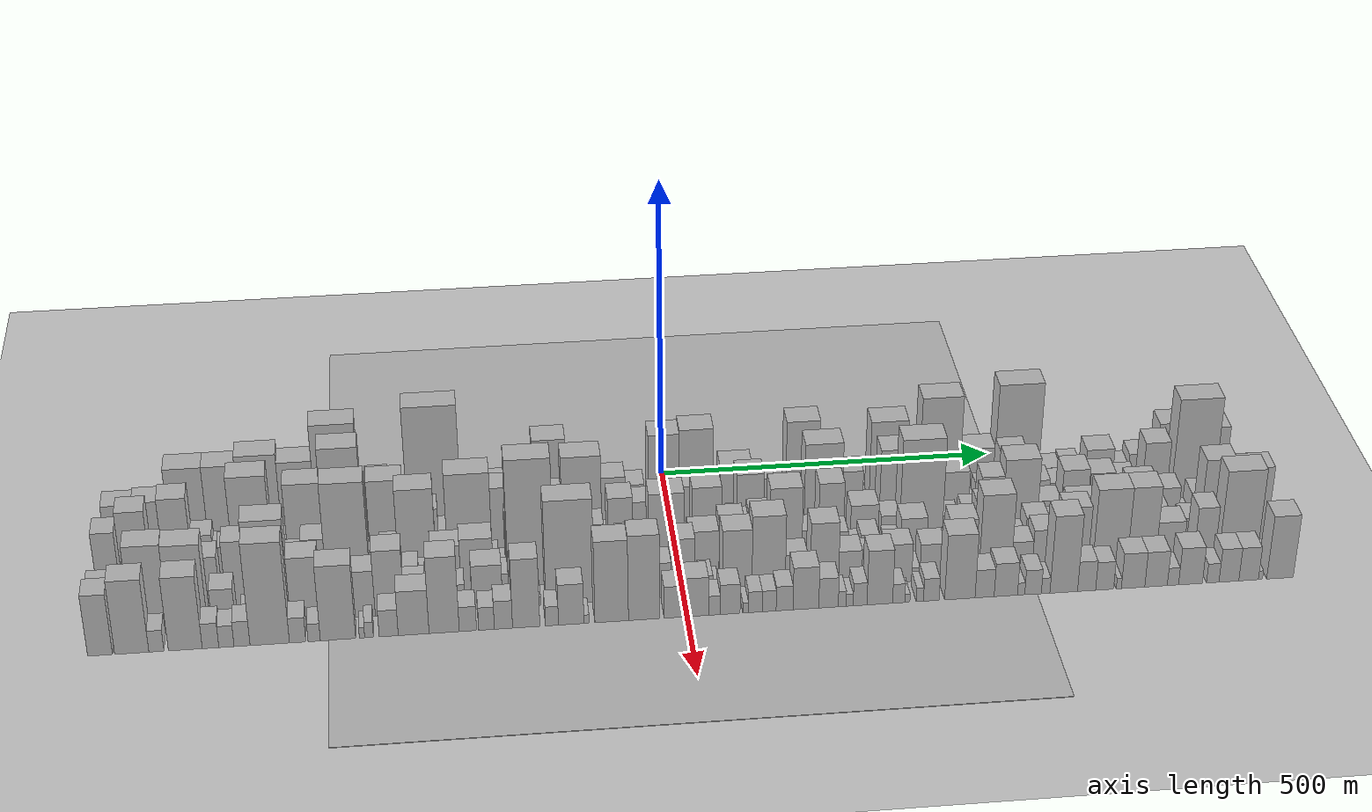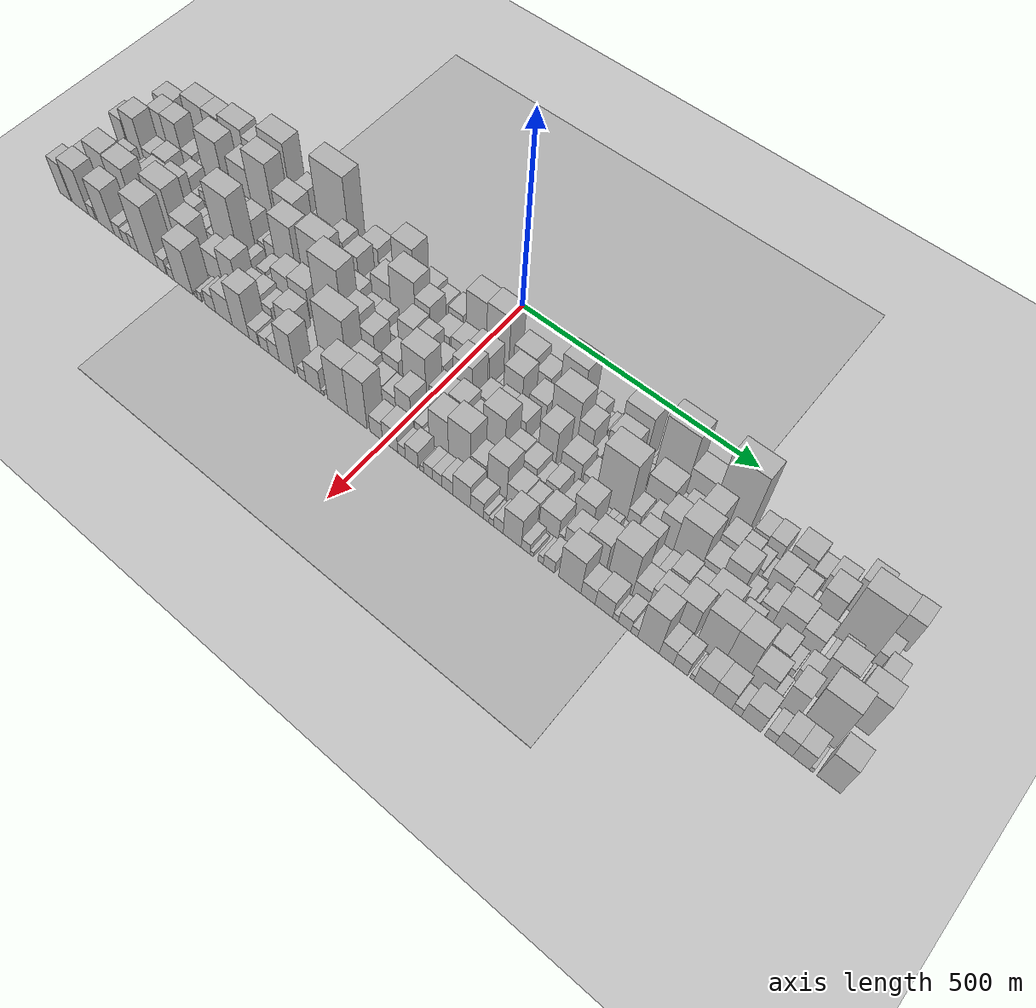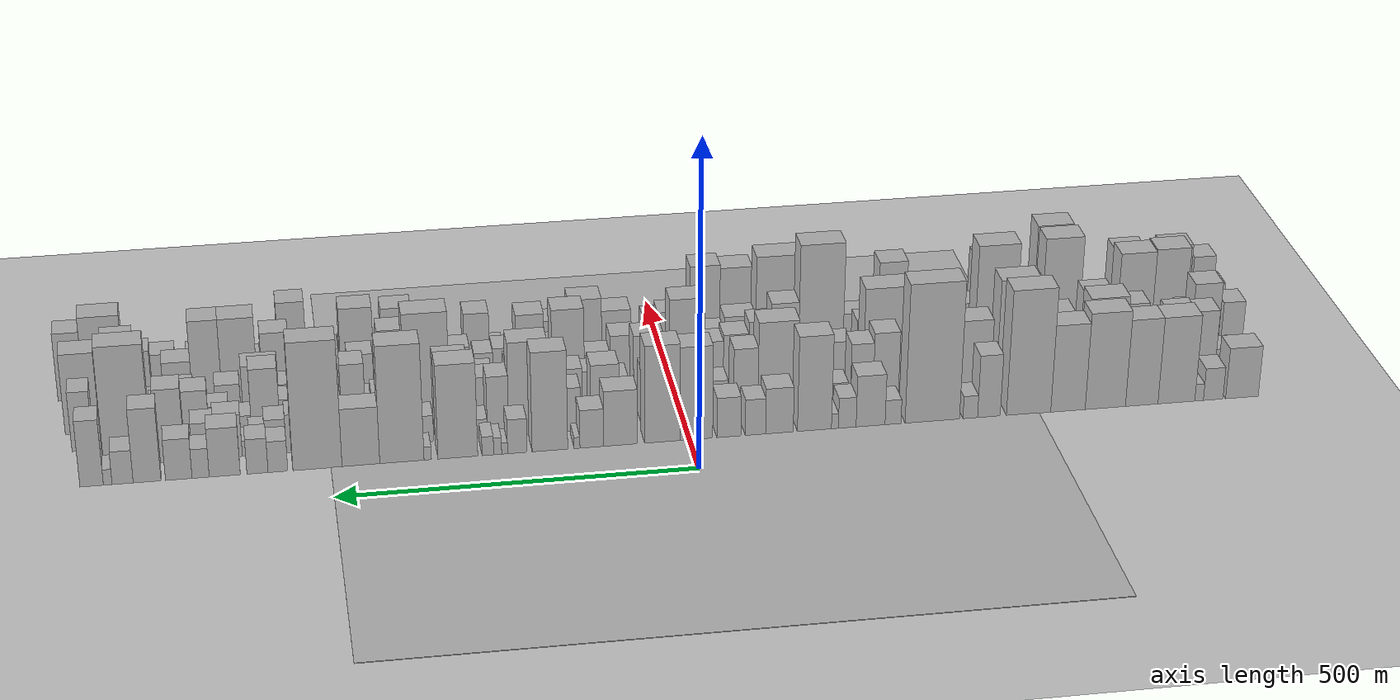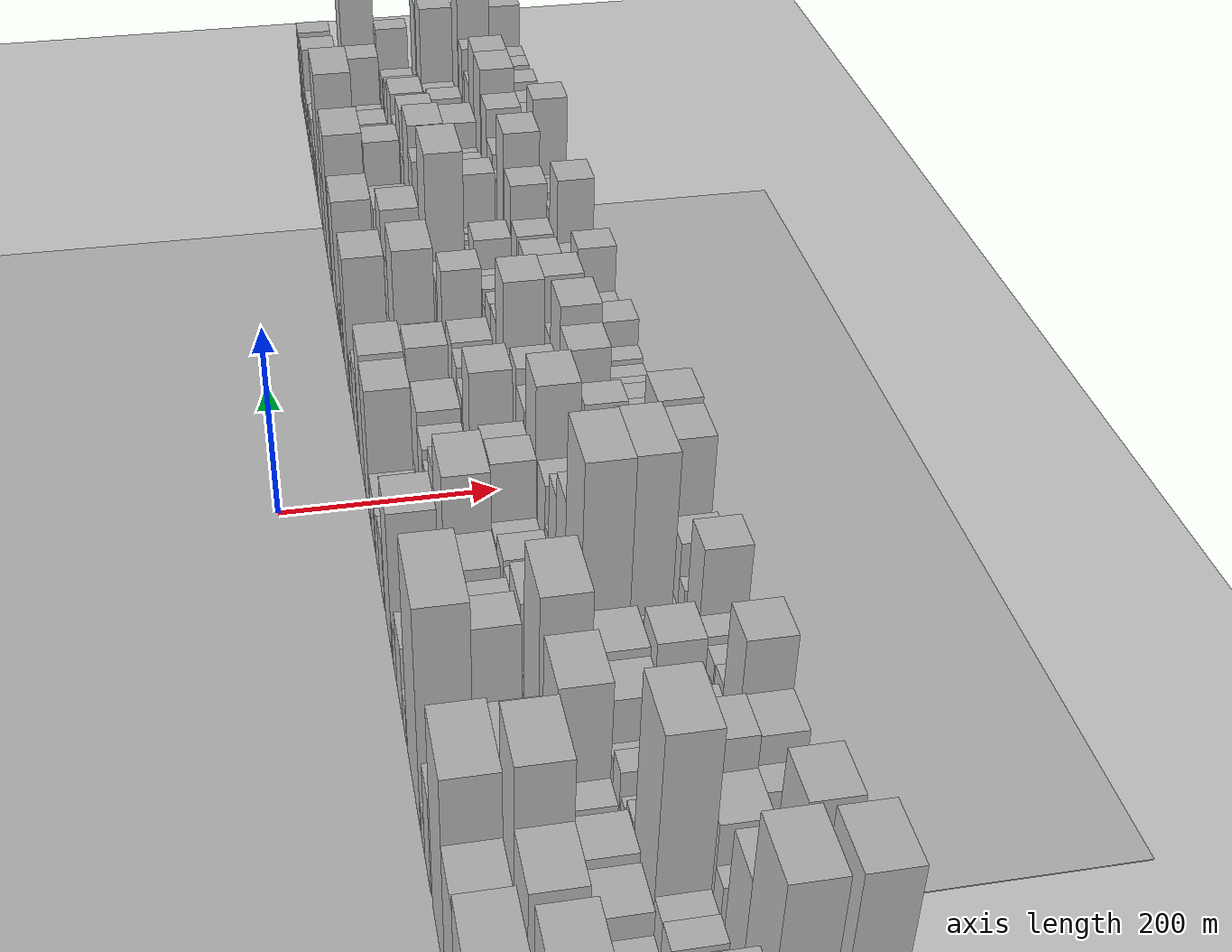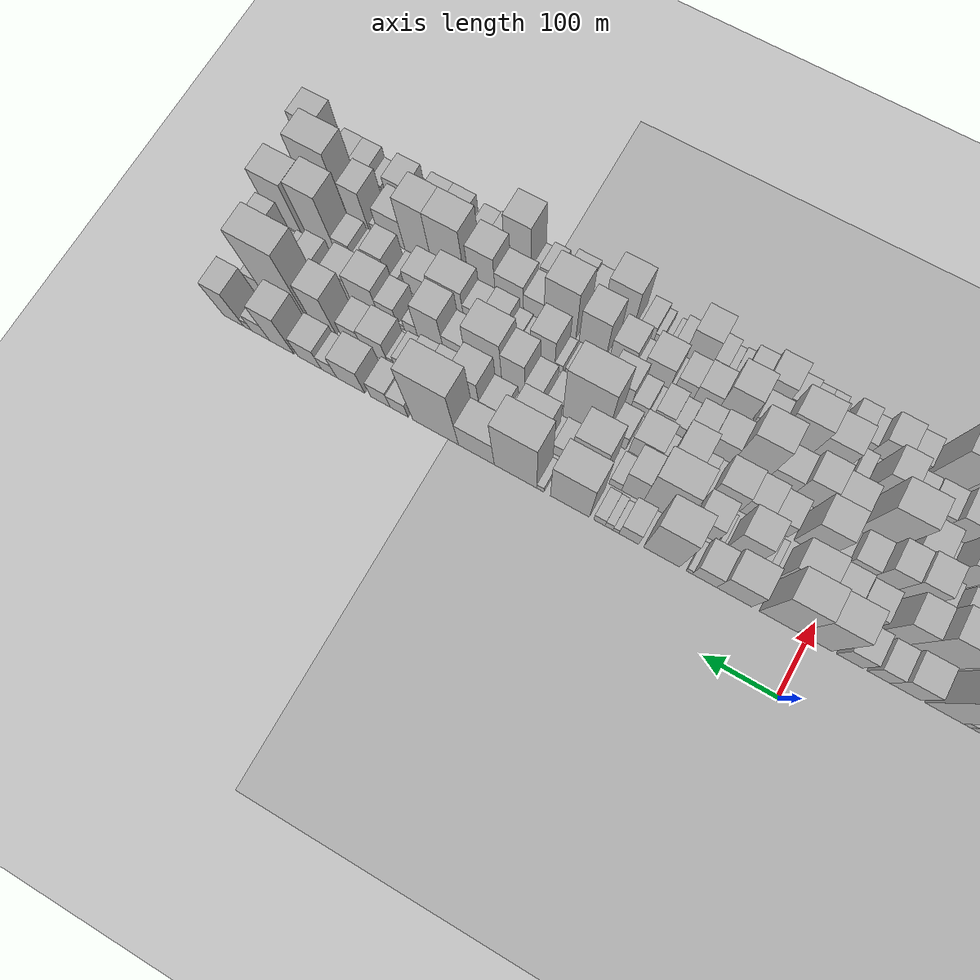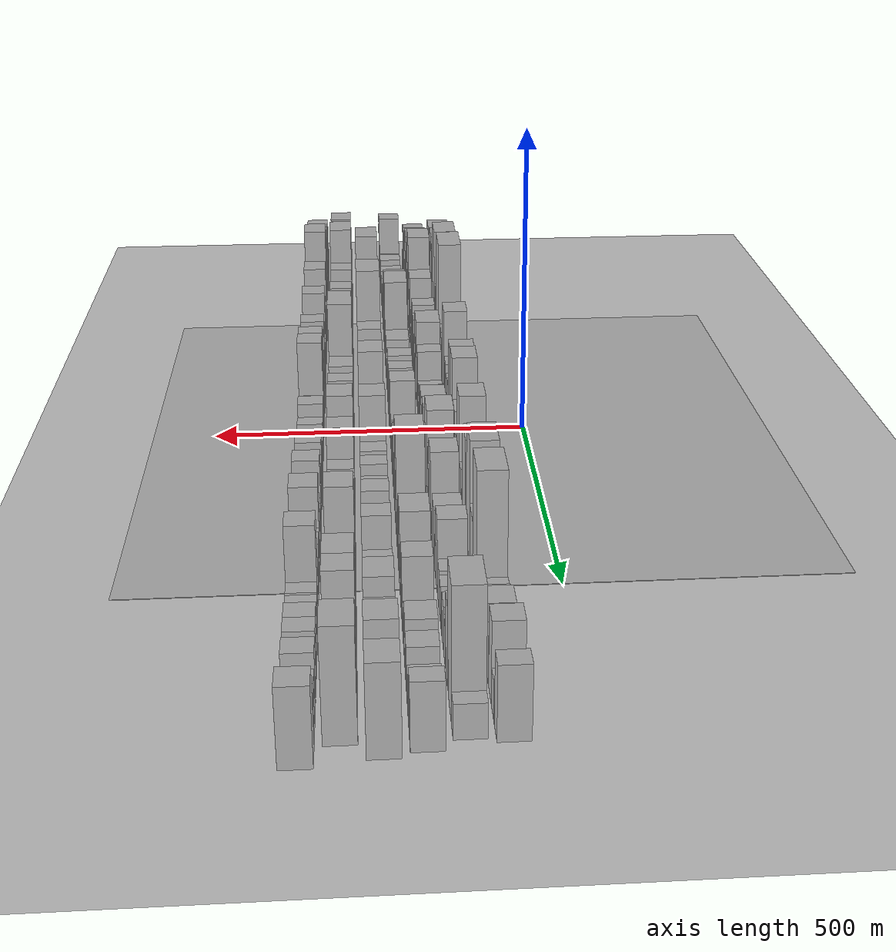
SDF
<?xml version="1.0" encoding="utf-8"?>

<sdf version="1.6">

   <world name="default">

      <gui fullscreen="0">

         <camera name="user_camera">

            <pose>-15 0 4.57585 0 0 0</pose>

            <view_controller>orbit</view_controller>

         </camera>

      </gui>

      <scene>

         <sky>

           <clouds>

             <speed>12</speed>

           </clouds>

         </sky>

         <ambient>0.4 0.4 0.4 1</ambient>

         <background>0.7 0.7 0.7 1</background>

         <shadows>1</shadows>

      </scene>

      <gravity>0 0 -9.8066</gravity>

      <magnetic_field>6e-06 2.3e-05 -4.2e-05</magnetic_field>

      <physics default="0" name="default_physics" type="ode">

         <ode>

            <solver>

               <type>quick</type>

               <iters>10</iters>

               <sor>1.0</sor>

               <use_dynamic_moi_rescaling>0</use_dynamic_moi_rescaling>

            </solver>

            <constraints>

               <cfm>0</cfm>

               <erp>0.2</erp>

               <contact_max_correcting_vel>100</contact_max_correcting_vel>

               <contact_surface_layer>0.001</contact_surface_layer>

            </constraints>

         </ode>

         <max_step_size>0.004</max_step_size>

         <real_time_factor>1</real_time_factor>

         <real_time_update_rate>250</real_time_update_rate>

      </physics>

      <light name="sun" type="directional">

         <cast_shadows>1</cast_shadows>

         <pose>0 0 10 0 0 0</pose>

         <diffuse>0.8 0.8 0.8 1</diffuse>

         <specular>0.2 0.2 0.2 1</specular>

         <attenuation>

            <range>1000</range>

            <constant>0.9</constant>

            <linear>0.01</linear>

            <quadratic>0.001</quadratic>

         </attenuation>

         <direction>-0.5 0.1 -0.9</direction>

      </light>

      <include>

         <name>ground_plane_1</name>

         <uri>model://HANNAS_ground_plane</uri>

         <pose>0 0 0  0 0 0</pose>

      </include>

      <include>

         <name>ground_plane_2</name>

         <uri>model://HANNAS_ground_plane</uri>

         <pose>100 0 0  0 0 0</pose>

      </include>

      <model name="building_1">

         <static>1</static>

         <pose frame="">100.0000 -797.8358 0 0.000000 0.000000 0.000000</pose>

         <link name="link">

            <pose frame="">0 0 40.50 0 0 0</pose>

            <collision name="collision">

               <geometry>

                  <box>

                     <size>40.0000 48.3283 81.0000</size>

                  </box>

               </geometry>

               <max_contacts>10</max_contacts>

               <surface>

                  <contact>

                     <ode/>

                  </contact>

                  <bounce/>

                  <friction>

                     <torsional>

                        <ode/>

                     </torsional>

                     <ode/>

                  </friction>

               </surface>

            </collision>

            <visual name="visual">

               <cast_shadows>0</cast_shadows>

               <geometry>

                  <box>

                     <size>40.0000 48.3283 81.0000</size>

                  </box>

               </geometry>

               <material>

                  <script>

                     <uri>model://HANNAS_wall/materials/scripts</uri>

                     <uri>model://HANNAS_wall/materials/textures</uri>

                     <name>vrc/HANNAS_wall</name>

                  </script>

               </material>

            </visual>

            <self_collide>0</self_collide>

            <enable_wind>0</enable_wind>

            <kinematic>0</kinematic>

         </link>

      </model>

      <model name="building_2">

         <static>1</static>

         <pose frame="">100.0000 -755.2595 0 0.000000 0.000000 0.000000</pose>

         <link name="link">

            <pose frame="">0 0 25.50 0 0 0</pose>

            <collision name="collision">

               <geometry>

                  <box>

                     <size>40.0000 28.8243 51.0000</size>

                  </box>

               </geometry>

               <max_contacts>10</max_contacts>

               <surface>

                  <contact>

                     <ode/>

                  </contact>

                  <bounce/>

                  <friction>

                     <torsional>

                        <ode/>

                     </torsional>

                     <ode/>

                  </friction>

               </surface>

            </collision>

            <visual name="visual">

               <cast_shadows>0</cast_shadows>

               <geometry>

                  <box>

                     <size>40.0000 28.8243 51.0000</size>

                  </box>

               </geometry>

               <material>

                  <script>

                     <uri>model://HANNAS_wall/materials/scripts</uri>

                     <uri>model://HANNAS_wall/materials/textures</uri>

                     <name>vrc/HANNAS_wall</name>

                  </script>

               </material>

            </visual>

            <self_collide>0</self_collide>

            <enable_wind>0</enable_wind>

            <kinematic>0</kinematic>

         </link>

      </model>

      <model name="building_3">

         <static>1</static>

         <pose frame="">100.0000 -734.4931 0 0.000000 0.000000 0.000000</pose>

         <link name="link">

            <pose frame="">0 0 13.50 0 0 0</pose>

            <collision name="collision">

               <geometry>

                  <box>

                     <size>40.0000 12.7086 27.0000</size>

                  </box>

               </geometry>

               <max_contacts>10</max_contacts>

               <surface>

                  <contact>

                     <ode/>

                  </contact>

                  <bounce/>

                  <friction>

                     <torsional>

                        <ode/>

                     </torsional>

                     <ode/>

                  </friction>

               </surface>

            </collision>

            <visual name="visual">

               <cast_shadows>0</cast_shadows>

               <geometry>

                  <box>

                     <size>40.0000 12.7086 27.0000</size>

                  </box>

               </geometry>

               <material>

                  <script>

                     <uri>model://HANNAS_wall/materials/scripts</uri>

                     <uri>model://HANNAS_wall/materials/textures</uri>

                     <name>vrc/HANNAS_wall</name>

                  </script>

               </material>

            </visual>

            <self_collide>0</self_collide>

            <enable_wind>0</enable_wind>

            <kinematic>0</kinematic>

         </link>

      </model>

      <model name="building_4">

         <static>1</static>

         <pose frame="">100.0000 -700.9512 0 0.000000 0.000000 0.000000</pose>

         <link name="link">

            <pose frame="">0 0 69.00 0 0 0</pose>

            <collision name="collision">

               <geometry>

                  <box>

                     <size>40.0000 54.3752 138.0000</size>

                  </box>

               </geometry>

               <max_contacts>10</max_contacts>

               <surface>

                  <contact>

                     <ode/>

                  </contact>

                  <bounce/>

                  <friction>

                     <torsional>

                        <ode/>

                     </torsional>

                     <ode/>

                  </friction>

               </surface>

            </collision>

            <visual name="visual">

               <cast_shadows>0</cast_shadows>

               <geometry>

                  <box>

                     <size>40.0000 54.3752 138.0000</size>

                  </box>

               </geometry>

               <material>

                  <script>

                     <uri>model://HANNAS_wall/materials/scripts</uri>

                     <uri>model://HANNAS_wall/materials/textures</uri>

                     <name>vrc/HANNAS_wall</name>

                  </script>

               </material>

            </visual>

            <self_collide>0</self_collide>

            <enable_wind>0</enable_wind>

            <kinematic>0</kinematic>

         </link>

      </model>

      <model name="building_5">

         <static>1</static>

         <pose frame="">100.0000 -649.9004 0 0.000000 0.000000 0.000000</pose>

         <link name="link">

            <pose frame="">0 0 69.00 0 0 0</pose>

            <collision name="collision">

               <geometry>

                  <box>

                     <size>40.0000 47.7264 138.0000</size>

                  </box>

               </geometry>

               <max_contacts>10</max_contacts>

               <surface>

                  <contact>

                     <ode/>

                  </contact>

                  <bounce/>

                  <friction>

                     <torsional>

                        <ode/>

                     </torsional>

                     <ode/>

                  </friction>

               </surface>

            </collision>

            <visual name="visual">

               <cast_shadows>0</cast_shadows>

               <geometry>

                  <box>

                     <size>40.0000 47.7264 138.0000</size>

                  </box>

               </geometry>

               <material>

                  <script>

                     <uri>model://HANNAS_wall/materials/scripts</uri>

                     <uri>model://HANNAS_wall/materials/textures</uri>

                     <name>vrc/HANNAS_wall</name>

                  </script>

               </material>

            </visual>

            <self_collide>0</self_collide>

            <enable_wind>0</enable_wind>

            <kinematic>0</kinematic>

         </link>

      </model>

      <model name="building_6">

         <static>1</static>

         <pose frame="">100.0000 -596.5173 0 0.000000 0.000000 0.000000</pose>

         <link name="link">

            <pose frame="">0 0 76.50 0 0 0</pose>

            <collision name="collision">

               <geometry>

                  <box>

                     <size>40.0000 59.0398 153.0000</size>

                  </box>

               </geometry>

               <max_contacts>10</max_contacts>

               <surface>

                  <contact>

                     <ode/>

                  </contact>

                  <bounce/>

                  <friction>

                     <torsional>

                        <ode/>

                     </torsional>

                     <ode/>

                  </friction>

               </surface>

            </collision>

            <visual name="visual">

               <cast_shadows>0</cast_shadows>

               <geometry>

                  <box>

                     <size>40.0000 59.0398 153.0000</size>

                  </box>

               </geometry>

               <material>

                  <script>

                     <uri>model://HANNAS_wall/materials/scripts</uri>

                     <uri>model://HANNAS_wall/materials/textures</uri>

                     <name>vrc/HANNAS_wall</name>

                  </script>

               </material>

            </visual>

            <self_collide>0</self_collide>

            <enable_wind>0</enable_wind>

            <kinematic>0</kinematic>

         </link>

      </model>

      <model name="building_7">

         <static>1</static>

         <pose frame="">100.0000 -541.8641 0 0.000000 0.000000 0.000000</pose>

         <link name="link">

            <pose frame="">0 0 69.00 0 0 0</pose>

            <collision name="collision">

               <geometry>

                  <box>

                     <size>40.0000 50.2668 138.0000</size>

                  </box>

               </geometry>

               <max_contacts>10</max_contacts>

               <surface>

                  <contact>

                     <ode/>

                  </contact>

                  <bounce/>

                  <friction>

                     <torsional>

                        <ode/>

                     </torsional>

                     <ode/>

                  </friction>

               </surface>

            </collision>

            <visual name="visual">

               <cast_shadows>0</cast_shadows>

               <geometry>

                  <box>

                     <size>40.0000 50.2668 138.0000</size>

                  </box>

               </geometry>

               <material>

                  <script>

                     <uri>model://HANNAS_wall/materials/scripts</uri>

                     <uri>model://HANNAS_wall/materials/textures</uri>

                     <name>vrc/HANNAS_wall</name>

                  </script>

               </material>

            </visual>

            <self_collide>0</self_collide>

            <enable_wind>0</enable_wind>

            <kinematic>0</kinematic>

         </link>

      </model>

      <model name="building_8">

         <static>1</static>

         <pose frame="">100.0000 -484.4871 0 0.000000 0.000000 0.000000</pose>

         <link name="link">

            <pose frame="">0 0 99.00 0 0 0</pose>

            <collision name="collision">

               <geometry>

                  <box>

                     <size>40.0000 64.4871 198.0000</size>

                  </box>

               </geometry>

               <max_contacts>10</max_contacts>

               <surface>

                  <contact>

                     <ode/>

                  </contact>

                  <bounce/>

                  <friction>

                     <torsional>

                        <ode/>

                     </torsional>

                     <ode/>

                  </friction>

               </surface>

            </collision>

            <visual name="visual">

               <cast_shadows>0</cast_shadows>

               <geometry>

                  <box>

                     <size>40.0000 64.4871 198.0000</size>

                  </box>

               </geometry>

               <material>

                  <script>

                     <uri>model://HANNAS_wall/materials/scripts</uri>

                     <uri>model://HANNAS_wall/materials/textures</uri>

                     <name>vrc/HANNAS_wall</name>

                  </script>

               </material>

            </visual>

            <self_collide>0</self_collide>

            <enable_wind>0</enable_wind>

            <kinematic>0</kinematic>

         </link>

      </model>

      <model name="building_9">

         <static>1</static>

         <pose frame="">100.0000 -426.8253 0 0.000000 0.000000 0.000000</pose>

         <link name="link">

            <pose frame="">0 0 49.50 0 0 0</pose>

            <collision name="collision">

               <geometry>

                  <box>

                     <size>40.0000 32.8365 99.0000</size>

                  </box>

               </geometry>

               <max_contacts>10</max_contacts>

               <surface>

                  <contact>

                     <ode/>

                  </contact>

                  <bounce/>

                  <friction>

                     <torsional>

                        <ode/>

                     </torsional>

                     <ode/>

                  </friction>

               </surface>

            </collision>

            <visual name="visual">

               <cast_shadows>0</cast_shadows>

               <geometry>

                  <box>

                     <size>40.0000 32.8365 99.0000</size>

                  </box>

               </geometry>

               <material>

                  <script>

                     <uri>model://HANNAS_wall/materials/scripts</uri>

                     <uri>model://HANNAS_wall/materials/textures</uri>

                     <name>vrc/HANNAS_wall</name>

                  </script>

               </material>

            </visual>

            <self_collide>0</self_collide>

            <enable_wind>0</enable_wind>

            <kinematic>0</kinematic>

         </link>

      </model>

      <model name="building_10">

         <static>1</static>

         <pose frame="">100.0000 -399.8568 0 0.000000 0.000000 0.000000</pose>

         <link name="link">

            <pose frame="">0 0 18.00 0 0 0</pose>

            <collision name="collision">

               <geometry>

                  <box>

                     <size>40.0000 21.1007 36.0000</size>

                  </box>

               </geometry>

               <max_contacts>10</max_contacts>

               <surface>

                  <contact>

                     <ode/>

                  </contact>

                  <bounce/>

                  <friction>

                     <torsional>

                        <ode/>

                     </torsional>

                     <ode/>

                  </friction>

               </surface>

            </collision>

            <visual name="visual">

               <cast_shadows>0</cast_shadows>

               <geometry>

                  <box>

                     <size>40.0000 21.1007 36.0000</size>

                  </box>

               </geometry>

               <material>

                  <script>

                     <uri>model://HANNAS_wall/materials/scripts</uri>

                     <uri>model://HANNAS_wall/materials/textures</uri>

                     <name>vrc/HANNAS_wall</name>

                  </script>

               </material>

            </visual>

            <self_collide>0</self_collide>

            <enable_wind>0</enable_wind>

            <kinematic>0</kinematic>

         </link>

      </model>

      <model name="building_11">

         <static>1</static>

         <pose frame="">100.0000 -345.0608 0 0.000000 0.000000 0.000000</pose>

         <link name="link">

            <pose frame="">0 0 109.50 0 0 0</pose>

            <collision name="collision">

               <geometry>

                  <box>

                     <size>40.0000 78.4912 219.0000</size>

                  </box>

               </geometry>

               <max_contacts>10</max_contacts>

               <surface>

                  <contact>

                     <ode/>

                  </contact>

                  <bounce/>

                  <friction>

                     <torsional>

                        <ode/>

                     </torsional>

                     <ode/>

                  </friction>

               </surface>

            </collision>

            <visual name="visual">

               <cast_shadows>0</cast_shadows>

               <geometry>

                  <box>

                     <size>40.0000 78.4912 219.0000</size>

                  </box>

               </geometry>

               <material>

                  <script>

                     <uri>model://HANNAS_wall/materials/scripts</uri>

                     <uri>model://HANNAS_wall/materials/textures</uri>

                     <name>vrc/HANNAS_wall</name>

                  </script>

               </material>

            </visual>

            <self_collide>0</self_collide>

            <enable_wind>0</enable_wind>

            <kinematic>0</kinematic>

         </link>

      </model>

      <model name="building_12">

         <static>1</static>

         <pose frame="">100.0000 -288.3945 0 0.000000 0.000000 0.000000</pose>

         <link name="link">

            <pose frame="">0 0 19.50 0 0 0</pose>

            <collision name="collision">

               <geometry>

                  <box>

                     <size>40.0000 22.8415 39.0000</size>

                  </box>

               </geometry>

               <max_contacts>10</max_contacts>

               <surface>

                  <contact>

                     <ode/>

                  </contact>

                  <bounce/>

                  <friction>

                     <torsional>

                        <ode/>

                     </torsional>

                     <ode/>

                  </friction>

               </surface>

            </collision>

            <visual name="visual">

               <cast_shadows>0</cast_shadows>

               <geometry>

                  <box>

                     <size>40.0000 22.8415 39.0000</size>

                  </box>

               </geometry>

               <material>

                  <script>

                     <uri>model://HANNAS_wall/materials/scripts</uri>

                     <uri>model://HANNAS_wall/materials/textures</uri>

                     <name>vrc/HANNAS_wall</name>

                  </script>

               </material>

            </visual>

            <self_collide>0</self_collide>

            <enable_wind>0</enable_wind>

            <kinematic>0</kinematic>

         </link>

      </model>

      <model name="building_13">

         <static>1</static>

         <pose frame="">100.0000 -256.2059 0 0.000000 0.000000 0.000000</pose>

         <link name="link">

            <pose frame="">0 0 40.50 0 0 0</pose>

            <collision name="collision">

               <geometry>

                  <box>

                     <size>40.0000 41.5355 81.0000</size>

                  </box>

               </geometry>

               <max_contacts>10</max_contacts>

               <surface>

                  <contact>

                     <ode/>

                  </contact>

                  <bounce/>

                  <friction>

                     <torsional>

                        <ode/>

                     </torsional>

                     <ode/>

                  </friction>

               </surface>

            </collision>

            <visual name="visual">

               <cast_shadows>0</cast_shadows>

               <geometry>

                  <box>

                     <size>40.0000 41.5355 81.0000</size>

                  </box>

               </geometry>

               <material>

                  <script>

                     <uri>model://HANNAS_wall/materials/scripts</uri>

                     <uri>model://HANNAS_wall/materials/textures</uri>

                     <name>vrc/HANNAS_wall</name>

                  </script>

               </material>

            </visual>

            <self_collide>0</self_collide>

            <enable_wind>0</enable_wind>

            <kinematic>0</kinematic>

         </link>

      </model>

      <model name="building_14">

         <static>1</static>

         <pose frame="">100.0000 -222.7769 0 0.000000 0.000000 0.000000</pose>

         <link name="link">

            <pose frame="">0 0 24.00 0 0 0</pose>

            <collision name="collision">

               <geometry>

                  <box>

                     <size>40.0000 25.3225 48.0000</size>

                  </box>

               </geometry>

               <max_contacts>10</max_contacts>

               <surface>

                  <contact>

                     <ode/>

                  </contact>

                  <bounce/>

                  <friction>

                     <torsional>

                        <ode/>

                     </torsional>

                     <ode/>

                  </friction>

               </surface>

            </collision>

            <visual name="visual">

               <cast_shadows>0</cast_shadows>

               <geometry>

                  <box>

                     <size>40.0000 25.3225 48.0000</size>

                  </box>

               </geometry>

               <material>

                  <script>

                     <uri>model://HANNAS_wall/materials/scripts</uri>

                     <uri>model://HANNAS_wall/materials/textures</uri>

                     <name>vrc/HANNAS_wall</name>

                  </script>

               </material>

            </visual>

            <self_collide>0</self_collide>

            <enable_wind>0</enable_wind>

            <kinematic>0</kinematic>

         </link>

      </model>

      <model name="building_15">

         <static>1</static>

         <pose frame="">100.0000 -205.1341 0 0.000000 0.000000 0.000000</pose>

         <link name="link">

            <pose frame="">0 0 12.00 0 0 0</pose>

            <collision name="collision">

               <geometry>

                  <box>

                     <size>40.0000 9.9630 24.0000</size>

                  </box>

               </geometry>

               <max_contacts>10</max_contacts>

               <surface>

                  <contact>

                     <ode/>

                  </contact>

                  <bounce/>

                  <friction>

                     <torsional>

                        <ode/>

                     </torsional>

                     <ode/>

                  </friction>

               </surface>

            </collision>

            <visual name="visual">

               <cast_shadows>0</cast_shadows>

               <geometry>

                  <box>

                     <size>40.0000 9.9630 24.0000</size>

                  </box>

               </geometry>

               <material>

                  <script>

                     <uri>model://HANNAS_wall/materials/scripts</uri>

                     <uri>model://HANNAS_wall/materials/textures</uri>

                     <name>vrc/HANNAS_wall</name>

                  </script>

               </material>

            </visual>

            <self_collide>0</self_collide>

            <enable_wind>0</enable_wind>

            <kinematic>0</kinematic>

         </link>

      </model>

      <model name="building_16">

         <static>1</static>

         <pose frame="">100.0000 -175.8913 0 0.000000 0.000000 0.000000</pose>

         <link name="link">

            <pose frame="">0 0 75.00 0 0 0</pose>

            <collision name="collision">

               <geometry>

                  <box>

                     <size>40.0000 48.5226 150.0000</size>

                  </box>

               </geometry>

               <max_contacts>10</max_contacts>

               <surface>

                  <contact>

                     <ode/>

                  </contact>

                  <bounce/>

                  <friction>

                     <torsional>

                        <ode/>

                     </torsional>

                     <ode/>

                  </friction>

               </surface>

            </collision>

            <visual name="visual">

               <cast_shadows>0</cast_shadows>

               <geometry>

                  <box>

                     <size>40.0000 48.5226 150.0000</size>

                  </box>

               </geometry>

               <material>

                  <script>

                     <uri>model://HANNAS_wall/materials/scripts</uri>

                     <uri>model://HANNAS_wall/materials/textures</uri>

                     <name>vrc/HANNAS_wall</name>

                  </script>

               </material>

            </visual>

            <self_collide>0</self_collide>

            <enable_wind>0</enable_wind>

            <kinematic>0</kinematic>

         </link>

      </model>

      <model name="building_17">

         <static>1</static>

         <pose frame="">100.0000 -125.9516 0 0.000000 0.000000 0.000000</pose>

         <link name="link">

            <pose frame="">0 0 36.00 0 0 0</pose>

            <collision name="collision">

               <geometry>

                  <box>

                     <size>40.0000 39.3568 72.0000</size>

                  </box>

               </geometry>

               <max_contacts>10</max_contacts>

               <surface>

                  <contact>

                     <ode/>

                  </contact>

                  <bounce/>

                  <friction>

                     <torsional>

                        <ode/>

                     </torsional>

                     <ode/>

                  </friction>

               </surface>

            </collision>

            <visual name="visual">

               <cast_shadows>0</cast_shadows>

               <geometry>

                  <box>

                     <size>40.0000 39.3568 72.0000</size>

                  </box>

               </geometry>

               <material>

                  <script>

                     <uri>model://HANNAS_wall/materials/scripts</uri>

                     <uri>model://HANNAS_wall/materials/textures</uri>

                     <name>vrc/HANNAS_wall</name>

                  </script>

               </material>

            </visual>

            <self_collide>0</self_collide>

            <enable_wind>0</enable_wind>

            <kinematic>0</kinematic>

         </link>

      </model>

      <model name="building_18">

         <static>1</static>

         <pose frame="">100.0000 -91.8525 0 0.000000 0.000000 0.000000</pose>

         <link name="link">

            <pose frame="">0 0 28.50 0 0 0</pose>

            <collision name="collision">

               <geometry>

                  <box>

                     <size>40.0000 28.8415 57.0000</size>

                  </box>

               </geometry>

               <max_contacts>10</max_contacts>

               <surface>

                  <contact>

                     <ode/>

                  </contact>

                  <bounce/>

                  <friction>

                     <torsional>

                        <ode/>

                     </torsional>

                     <ode/>

                  </friction>

               </surface>

            </collision>

            <visual name="visual">

               <cast_shadows>0</cast_shadows>

               <geometry>

                  <box>

                     <size>40.0000 28.8415 57.0000</size>

                  </box>

               </geometry>

               <material>

                  <script>

                     <uri>model://HANNAS_wall/materials/scripts</uri>

                     <uri>model://HANNAS_wall/materials/textures</uri>

                     <name>vrc/HANNAS_wall</name>

                  </script>

               </material>

            </visual>

            <self_collide>0</self_collide>

            <enable_wind>0</enable_wind>

            <kinematic>0</kinematic>

         </link>

      </model>

      <model name="building_19">

         <static>1</static>

         <pose frame="">100.0000 -54.3351 0 0.000000 0.000000 0.000000</pose>

         <link name="link">

            <pose frame="">0 0 31.50 0 0 0</pose>

            <collision name="collision">

               <geometry>

                  <box>

                     <size>40.0000 34.1933 63.0000</size>

                  </box>

               </geometry>

               <max_contacts>10</max_contacts>

               <surface>

                  <contact>

                     <ode/>

                  </contact>

                  <bounce/>

                  <friction>

                     <torsional>

                        <ode/>

                     </torsional>

                     <ode/>

                  </friction>

               </surface>

            </collision>

            <visual name="visual">

               <cast_shadows>0</cast_shadows>

               <geometry>

                  <box>

                     <size>40.0000 34.1933 63.0000</size>

                  </box>

               </geometry>

               <material>

                  <script>

                     <uri>model://HANNAS_wall/materials/scripts</uri>

                     <uri>model://HANNAS_wall/materials/textures</uri>

                     <name>vrc/HANNAS_wall</name>

                  </script>

               </material>

            </visual>

            <self_collide>0</self_collide>

            <enable_wind>0</enable_wind>

            <kinematic>0</kinematic>

         </link>

      </model>

      <model name="building_20">

         <static>1</static>

         <pose frame="">100.0000 -8.2936 0 0.000000 0.000000 0.000000</pose>

         <link name="link">

            <pose frame="">0 0 73.50 0 0 0</pose>

            <collision name="collision">

               <geometry>

                  <box>

                     <size>40.0000 45.8897 147.0000</size>

                  </box>

               </geometry>

               <max_contacts>10</max_contacts>

               <surface>

                  <contact>

                     <ode/>

                  </contact>

                  <bounce/>

                  <friction>

                     <torsional>

                        <ode/>

                     </torsional>

                     <ode/>

                  </friction>

               </surface>

            </collision>

            <visual name="visual">

               <cast_shadows>0</cast_shadows>

               <geometry>

                  <box>

                     <size>40.0000 45.8897 147.0000</size>

                  </box>

               </geometry>

               <material>

                  <script>

                     <uri>model://HANNAS_wall/materials/scripts</uri>

                     <uri>model://HANNAS_wall/materials/textures</uri>

                     <name>vrc/HANNAS_wall</name>

                  </script>

               </material>

            </visual>

            <self_collide>0</self_collide>

            <enable_wind>0</enable_wind>

            <kinematic>0</kinematic>

         </link>

      </model>

      <model name="building_21">

         <static>1</static>

         <pose frame="">100.0000 39.7256 0 0.000000 0.000000 0.000000</pose>

         <link name="link">

            <pose frame="">0 0 76.50 0 0 0</pose>

            <collision name="collision">

               <geometry>

                  <box>

                     <size>40.0000 50.1487 153.0000</size>

                  </box>

               </geometry>

               <max_contacts>10</max_contacts>

               <surface>

                  <contact>

                     <ode/>

                  </contact>

                  <bounce/>

                  <friction>

                     <torsional>

                        <ode/>

                     </torsional>

                     <ode/>

                  </friction>

               </surface>

            </collision>

            <visual name="visual">

               <cast_shadows>0</cast_shadows>

               <geometry>

                  <box>

                     <size>40.0000 50.1487 153.0000</size>

                  </box>

               </geometry>

               <material>

                  <script>

                     <uri>model://HANNAS_wall/materials/scripts</uri>

                     <uri>model://HANNAS_wall/materials/textures</uri>

                     <name>vrc/HANNAS_wall</name>

                  </script>

               </material>

            </visual>

            <self_collide>0</self_collide>

            <enable_wind>0</enable_wind>

            <kinematic>0</kinematic>

         </link>

      </model>

      <model name="building_22">

         <static>1</static>

         <pose frame="">100.0000 98.5002 0 0.000000 0.000000 0.000000</pose>

         <link name="link">

            <pose frame="">0 0 43.50 0 0 0</pose>

            <collision name="collision">

               <geometry>

                  <box>

                     <size>40.0000 47.4005 87.0000</size>

                  </box>

               </geometry>

               <max_contacts>10</max_contacts>

               <surface>

                  <contact>

                     <ode/>

                  </contact>

                  <bounce/>

                  <friction>

                     <torsional>

                        <ode/>

                     </torsional>

                     <ode/>

                  </friction>

               </surface>

            </collision>

            <visual name="visual">

               <cast_shadows>0</cast_shadows>

               <geometry>

                  <box>

                     <size>40.0000 47.4005 87.0000</size>

                  </box>

               </geometry>

               <material>

                  <script>

                     <uri>model://HANNAS_wall/materials/scripts</uri>

                     <uri>model://HANNAS_wall/materials/textures</uri>

                     <name>vrc/HANNAS_wall</name>

                  </script>

               </material>

            </visual>

            <self_collide>0</self_collide>

            <enable_wind>0</enable_wind>

            <kinematic>0</kinematic>

         </link>

      </model>

      <model name="building_23">

         <static>1</static>

         <pose frame="">100.0000 138.7898 0 0.000000 0.000000 0.000000</pose>

         <link name="link">

            <pose frame="">0 0 30.00 0 0 0</pose>

            <collision name="collision">

               <geometry>

                  <box>

                     <size>40.0000 33.1786 60.0000</size>

                  </box>

               </geometry>

               <max_contacts>10</max_contacts>

               <surface>

                  <contact>

                     <ode/>

                  </contact>

                  <bounce/>

                  <friction>

                     <torsional>

                        <ode/>

                     </torsional>

                     <ode/>

                  </friction>

               </surface>

            </collision>

            <visual name="visual">

               <cast_shadows>0</cast_shadows>

               <geometry>

                  <box>

                     <size>40.0000 33.1786 60.0000</size>

                  </box>

               </geometry>

               <material>

                  <script>

                     <uri>model://HANNAS_wall/materials/scripts</uri>

                     <uri>model://HANNAS_wall/materials/textures</uri>

                     <name>vrc/HANNAS_wall</name>

                  </script>

               </material>

            </visual>

            <self_collide>0</self_collide>

            <enable_wind>0</enable_wind>

            <kinematic>0</kinematic>

         </link>

      </model>

      <model name="building_24">

         <static>1</static>

         <pose frame="">100.0000 159.4438 0 0.000000 0.000000 0.000000</pose>

         <link name="link">

            <pose frame="">0 0 9.00 0 0 0</pose>

            <collision name="collision">

               <geometry>

                  <box>

                     <size>40.0000 8.1295 18.0000</size>

                  </box>

               </geometry>

               <max_contacts>10</max_contacts>

               <surface>

                  <contact>

                     <ode/>

                  </contact>

                  <bounce/>

                  <friction>

                     <torsional>

                        <ode/>

                     </torsional>

                     <ode/>

                  </friction>

               </surface>

            </collision>

            <visual name="visual">

               <cast_shadows>0</cast_shadows>

               <geometry>

                  <box>

                     <size>40.0000 8.1295 18.0000</size>

                  </box>

               </geometry>

               <material>

                  <script>

                     <uri>model://HANNAS_wall/materials/scripts</uri>

                     <uri>model://HANNAS_wall/materials/textures</uri>

                     <name>vrc/HANNAS_wall</name>

                  </script>

               </material>

            </visual>

            <self_collide>0</self_collide>

            <enable_wind>0</enable_wind>

            <kinematic>0</kinematic>

         </link>

      </model>

      <model name="building_25">

         <static>1</static>

         <pose frame="">100.0000 197.3159 0 0.000000 0.000000 0.000000</pose>

         <link name="link">

            <pose frame="">0 0 78.00 0 0 0</pose>

            <collision name="collision">

               <geometry>

                  <box>

                     <size>40.0000 49.6146 156.0000</size>

                  </box>

               </geometry>

               <max_contacts>10</max_contacts>

               <surface>

                  <contact>

                     <ode/>

                  </contact>

                  <bounce/>

                  <friction>

                     <torsional>

                        <ode/>

                     </torsional>

                     <ode/>

                  </friction>

               </surface>

            </collision>

            <visual name="visual">

               <cast_shadows>0</cast_shadows>

               <geometry>

                  <box>

                     <size>40.0000 49.6146 156.0000</size>

                  </box>

               </geometry>

               <material>

                  <script>

                     <uri>model://HANNAS_wall/materials/scripts</uri>

                     <uri>model://HANNAS_wall/materials/textures</uri>

                     <name>vrc/HANNAS_wall</name>

                  </script>

               </material>

            </visual>

            <self_collide>0</self_collide>

            <enable_wind>0</enable_wind>

            <kinematic>0</kinematic>

         </link>

      </model>

      <model name="building_26">

         <static>1</static>

         <pose frame="">100.0000 242.6828 0 0.000000 0.000000 0.000000</pose>

         <link name="link">

            <pose frame="">0 0 27.00 0 0 0</pose>

            <collision name="collision">

               <geometry>

                  <box>

                     <size>40.0000 27.1191 54.0000</size>

                  </box>

               </geometry>

               <max_contacts>10</max_contacts>

               <surface>

                  <contact>

                     <ode/>

                  </contact>

                  <bounce/>

                  <friction>

                     <torsional>

                        <ode/>

                     </torsional>

                     <ode/>

                  </friction>

               </surface>

            </collision>

            <visual name="visual">

               <cast_shadows>0</cast_shadows>

               <geometry>

                  <box>

                     <size>40.0000 27.1191 54.0000</size>

                  </box>

               </geometry>

               <material>

                  <script>

                     <uri>model://HANNAS_wall/materials/scripts</uri>

                     <uri>model://HANNAS_wall/materials/textures</uri>

                     <name>vrc/HANNAS_wall</name>

                  </script>

               </material>

            </visual>

            <self_collide>0</self_collide>

            <enable_wind>0</enable_wind>

            <kinematic>0</kinematic>

         </link>

      </model>

      <model name="building_27">

         <static>1</static>

         <pose frame="">100.0000 260.3676 0 0.000000 0.000000 0.000000</pose>

         <link name="link">

            <pose frame="">0 0 9.00 0 0 0</pose>

            <collision name="collision">

               <geometry>

                  <box>

                     <size>40.0000 8.2504 18.0000</size>

                  </box>

               </geometry>

               <max_contacts>10</max_contacts>

               <surface>

                  <contact>

                     <ode/>

                  </contact>

                  <bounce/>

                  <friction>

                     <torsional>

                        <ode/>

                     </torsional>

                     <ode/>

                  </friction>

               </surface>

            </collision>

            <visual name="visual">

               <cast_shadows>0</cast_shadows>

               <geometry>

                  <box>

                     <size>40.0000 8.2504 18.0000</size>

                  </box>

               </geometry>

               <material>

                  <script>

                     <uri>model://HANNAS_wall/materials/scripts</uri>

                     <uri>model://HANNAS_wall/materials/textures</uri>

                     <name>vrc/HANNAS_wall</name>

                  </script>

               </material>

            </visual>

            <self_collide>0</self_collide>

            <enable_wind>0</enable_wind>

            <kinematic>0</kinematic>

         </link>

      </model>

      <model name="building_28">

         <static>1</static>

         <pose frame="">100.0000 270.0433 0 0.000000 0.000000 0.000000</pose>

         <link name="link">

            <pose frame="">0 0 13.50 0 0 0</pose>

            <collision name="collision">

               <geometry>

                  <box>

                     <size>40.0000 11.1012 27.0000</size>

                  </box>

               </geometry>

               <max_contacts>10</max_contacts>

               <surface>

                  <contact>

                     <ode/>

                  </contact>

                  <bounce/>

                  <friction>

                     <torsional>

                        <ode/>

                     </torsional>

                     <ode/>

                  </friction>

               </surface>

            </collision>

            <visual name="visual">

               <cast_shadows>0</cast_shadows>

               <geometry>

                  <box>

                     <size>40.0000 11.1012 27.0000</size>

                  </box>

               </geometry>

               <material>

                  <script>

                     <uri>model://HANNAS_wall/materials/scripts</uri>

                     <uri>model://HANNAS_wall/materials/textures</uri>

                     <name>vrc/HANNAS_wall</name>

                  </script>

               </material>

            </visual>

            <self_collide>0</self_collide>

            <enable_wind>0</enable_wind>

            <kinematic>0</kinematic>

         </link>

      </model>

      <model name="building_29">

         <static>1</static>

         <pose frame="">100.0000 283.6312 0 0.000000 0.000000 0.000000</pose>

         <link name="link">

            <pose frame="">0 0 15.00 0 0 0</pose>

            <collision name="collision">

               <geometry>

                  <box>

                     <size>40.0000 16.0745 30.0000</size>

                  </box>

               </geometry>

               <max_contacts>10</max_contacts>

               <surface>

                  <contact>

                     <ode/>

                  </contact>

                  <bounce/>

                  <friction>

                     <torsional>

                        <ode/>

                     </torsional>

                     <ode/>

                  </friction>

               </surface>

            </collision>

            <visual name="visual">

               <cast_shadows>0</cast_shadows>

               <geometry>

                  <box>

                     <size>40.0000 16.0745 30.0000</size>

                  </box>

               </geometry>

               <material>

                  <script>

                     <uri>model://HANNAS_wall/materials/scripts</uri>

                     <uri>model://HANNAS_wall/materials/textures</uri>

                     <name>vrc/HANNAS_wall</name>

                  </script>

               </material>

            </visual>

            <self_collide>0</self_collide>

            <enable_wind>0</enable_wind>

            <kinematic>0</kinematic>

         </link>

      </model>

      <model name="building_30">

         <static>1</static>

         <pose frame="">100.0000 325.2024 0 0.000000 0.000000 0.000000</pose>

         <link name="link">

            <pose frame="">0 0 73.50 0 0 0</pose>

            <collision name="collision">

               <geometry>

                  <box>

                     <size>40.0000 55.0679 147.0000</size>

                  </box>

               </geometry>

               <max_contacts>10</max_contacts>

               <surface>

                  <contact>

                     <ode/>

                  </contact>

                  <bounce/>

                  <friction>

                     <torsional>

                        <ode/>

                     </torsional>

                     <ode/>

                  </friction>

               </surface>

            </collision>

            <visual name="visual">

               <cast_shadows>0</cast_shadows>

               <geometry>

                  <box>

                     <size>40.0000 55.0679 147.0000</size>

                  </box>

               </geometry>

               <material>

                  <script>

                     <uri>model://HANNAS_wall/materials/scripts</uri>

                     <uri>model://HANNAS_wall/materials/textures</uri>

                     <name>vrc/HANNAS_wall</name>

                  </script>

               </material>

            </visual>

            <self_collide>0</self_collide>

            <enable_wind>0</enable_wind>

            <kinematic>0</kinematic>

         </link>

      </model>

      <model name="building_31">

         <static>1</static>

         <pose frame="">100.0000 366.8313 0 0.000000 0.000000 0.000000</pose>

         <link name="link">

            <pose frame="">0 0 10.50 0 0 0</pose>

            <collision name="collision">

               <geometry>

                  <box>

                     <size>40.0000 10.1898 21.0000</size>

                  </box>

               </geometry>

               <max_contacts>10</max_contacts>

               <surface>

                  <contact>

                     <ode/>

                  </contact>

                  <bounce/>

                  <friction>

                     <torsional>

                        <ode/>

                     </torsional>

                     <ode/>

                  </friction>

               </surface>

            </collision>

            <visual name="visual">

               <cast_shadows>0</cast_shadows>

               <geometry>

                  <box>

                     <size>40.0000 10.1898 21.0000</size>

                  </box>

               </geometry>

               <material>

                  <script>

                     <uri>model://HANNAS_wall/materials/scripts</uri>

                     <uri>model://HANNAS_wall/materials/textures</uri>

                     <name>vrc/HANNAS_wall</name>

                  </script>

               </material>

            </visual>

            <self_collide>0</self_collide>

            <enable_wind>0</enable_wind>

            <kinematic>0</kinematic>

         </link>

      </model>

      <model name="building_32">

         <static>1</static>

         <pose frame="">100.0000 402.4105 0 0.000000 0.000000 0.000000</pose>

         <link name="link">

            <pose frame="">0 0 91.50 0 0 0</pose>

            <collision name="collision">

               <geometry>

                  <box>

                     <size>40.0000 60.9687 183.0000</size>

                  </box>

               </geometry>

               <max_contacts>10</max_contacts>

               <surface>

                  <contact>

                     <ode/>

                  </contact>

                  <bounce/>

                  <friction>

                     <torsional>

                        <ode/>

                     </torsional>

                     <ode/>

                  </friction>

               </surface>

            </collision>

            <visual name="visual">

               <cast_shadows>0</cast_shadows>

               <geometry>

                  <box>

                     <size>40.0000 60.9687 183.0000</size>

                  </box>

               </geometry>

               <material>

                  <script>

                     <uri>model://HANNAS_wall/materials/scripts</uri>

                     <uri>model://HANNAS_wall/materials/textures</uri>

                     <name>vrc/HANNAS_wall</name>

                  </script>

               </material>

            </visual>

            <self_collide>0</self_collide>

            <enable_wind>0</enable_wind>

            <kinematic>0</kinematic>

         </link>

      </model>

      <model name="building_33">

         <static>1</static>

         <pose frame="">100.0000 458.7951 0 0.000000 0.000000 0.000000</pose>

         <link name="link">

            <pose frame="">0 0 45.00 0 0 0</pose>

            <collision name="collision">

               <geometry>

                  <box>

                     <size>40.0000 51.8007 90.0000</size>

                  </box>

               </geometry>

               <max_contacts>10</max_contacts>

               <surface>

                  <contact>

                     <ode/>

                  </contact>

                  <bounce/>

                  <friction>

                     <torsional>

                        <ode/>

                     </torsional>

                     <ode/>

                  </friction>

               </surface>

            </collision>

            <visual name="visual">

               <cast_shadows>0</cast_shadows>

               <geometry>

                  <box>

                     <size>40.0000 51.8007 90.0000</size>

                  </box>

               </geometry>

               <material>

                  <script>

                     <uri>model://HANNAS_wall/materials/scripts</uri>

                     <uri>model://HANNAS_wall/materials/textures</uri>

                     <name>vrc/HANNAS_wall</name>

                  </script>

               </material>

            </visual>

            <self_collide>0</self_collide>

            <enable_wind>0</enable_wind>

            <kinematic>0</kinematic>

         </link>

      </model>

      <model name="building_34">

         <static>1</static>

         <pose frame="">100.0000 518.2895 0 0.000000 0.000000 0.000000</pose>

         <link name="link">

            <pose frame="">0 0 99.00 0 0 0</pose>

            <collision name="collision">

               <geometry>

                  <box>

                     <size>40.0000 67.1880 198.0000</size>

                  </box>

               </geometry>

               <max_contacts>10</max_contacts>

               <surface>

                  <contact>

                     <ode/>

                  </contact>

                  <bounce/>

                  <friction>

                     <torsional>

                        <ode/>

                     </torsional>

                     <ode/>

                  </friction>

               </surface>

            </collision>

            <visual name="visual">

               <cast_shadows>0</cast_shadows>

               <geometry>

                  <box>

                     <size>40.0000 67.1880 198.0000</size>

                  </box>

               </geometry>

               <material>

                  <script>

                     <uri>model://HANNAS_wall/materials/scripts</uri>

                     <uri>model://HANNAS_wall/materials/textures</uri>

                     <name>vrc/HANNAS_wall</name>

                  </script>

               </material>

            </visual>

            <self_collide>0</self_collide>

            <enable_wind>0</enable_wind>

            <kinematic>0</kinematic>

         </link>

      </model>

      <model name="building_35">

         <static>1</static>

         <pose frame="">100.0000 572.3179 0 0.000000 0.000000 0.000000</pose>

         <link name="link">

            <pose frame="">0 0 24.00 0 0 0</pose>

            <collision name="collision">

               <geometry>

                  <box>

                     <size>40.0000 26.8688 48.0000</size>

                  </box>

               </geometry>

               <max_contacts>10</max_contacts>

               <surface>

                  <contact>

                     <ode/>

                  </contact>

                  <bounce/>

                  <friction>

                     <torsional>

                        <ode/>

                     </torsional>

                     <ode/>

                  </friction>

               </surface>

            </collision>

            <visual name="visual">

               <cast_shadows>0</cast_shadows>

               <geometry>

                  <box>

                     <size>40.0000 26.8688 48.0000</size>

                  </box>

               </geometry>

               <material>

                  <script>

                     <uri>model://HANNAS_wall/materials/scripts</uri>

                     <uri>model://HANNAS_wall/materials/textures</uri>

                     <name>vrc/HANNAS_wall</name>

                  </script>

               </material>

            </visual>

            <self_collide>0</self_collide>

            <enable_wind>0</enable_wind>

            <kinematic>0</kinematic>

         </link>

      </model>

      <model name="building_36">

         <static>1</static>

         <pose frame="">100.0000 600.1431 0 0.000000 0.000000 0.000000</pose>

         <link name="link">

            <pose frame="">0 0 27.00 0 0 0</pose>

            <collision name="collision">

               <geometry>

                  <box>

                     <size>40.0000 28.7815 54.0000</size>

                  </box>

               </geometry>

               <max_contacts>10</max_contacts>

               <surface>

                  <contact>

                     <ode/>

                  </contact>

                  <bounce/>

                  <friction>

                     <torsional>

                        <ode/>

                     </torsional>

                     <ode/>

                  </friction>

               </surface>

            </collision>

            <visual name="visual">

               <cast_shadows>0</cast_shadows>

               <geometry>

                  <box>

                     <size>40.0000 28.7815 54.0000</size>

                  </box>

               </geometry>

               <material>

                  <script>

                     <uri>model://HANNAS_wall/materials/scripts</uri>

                     <uri>model://HANNAS_wall/materials/textures</uri>

                     <name>vrc/HANNAS_wall</name>

                  </script>

               </material>

            </visual>

            <self_collide>0</self_collide>

            <enable_wind>0</enable_wind>

            <kinematic>0</kinematic>

         </link>

      </model>

      <model name="building_37">

         <static>1</static>

         <pose frame="">100.0000 644.5969 0 0.000000 0.000000 0.000000</pose>

         <link name="link">

            <pose frame="">0 0 37.50 0 0 0</pose>

            <collision name="collision">

               <geometry>

                  <box>

                     <size>40.0000 42.1262 75.0000</size>

                  </box>

               </geometry>

               <max_contacts>10</max_contacts>

               <surface>

                  <contact>

                     <ode/>

                  </contact>

                  <bounce/>

                  <friction>

                     <torsional>

                        <ode/>

                     </torsional>

                     <ode/>

                  </friction>

               </surface>

            </collision>

            <visual name="visual">

               <cast_shadows>0</cast_shadows>

               <geometry>

                  <box>

                     <size>40.0000 42.1262 75.0000</size>

                  </box>

               </geometry>

               <material>

                  <script>

                     <uri>model://HANNAS_wall/materials/scripts</uri>

                     <uri>model://HANNAS_wall/materials/textures</uri>

                     <name>vrc/HANNAS_wall</name>

                  </script>

               </material>

            </visual>

            <self_collide>0</self_collide>

            <enable_wind>0</enable_wind>

            <kinematic>0</kinematic>

         </link>

      </model>

      <model name="building_38">

         <static>1</static>

         <pose frame="">100.0000 677.2356 0 0.000000 0.000000 0.000000</pose>

         <link name="link">

            <pose frame="">0 0 22.50 0 0 0</pose>

            <collision name="collision">

               <geometry>

                  <box>

                     <size>40.0000 23.1513 45.0000</size>

                  </box>

               </geometry>

               <max_contacts>10</max_contacts>

               <surface>

                  <contact>

                     <ode/>

                  </contact>

                  <bounce/>

                  <friction>

                     <torsional>

                        <ode/>

                     </torsional>

                     <ode/>

                  </friction>

               </surface>

            </collision>

            <visual name="visual">

               <cast_shadows>0</cast_shadows>

               <geometry>

                  <box>

                     <size>40.0000 23.1513 45.0000</size>

                  </box>

               </geometry>

               <material>

                  <script>

                     <uri>model://HANNAS_wall/materials/scripts</uri>

                     <uri>model://HANNAS_wall/materials/textures</uri>

                     <name>vrc/HANNAS_wall</name>

                  </script>

               </material>

            </visual>

            <self_collide>0</self_collide>

            <enable_wind>0</enable_wind>

            <kinematic>0</kinematic>

         </link>

      </model>

      <model name="building_39">

         <static>1</static>

         <pose frame="">100.0000 706.8171 0 0.000000 0.000000 0.000000</pose>

         <link name="link">

            <pose frame="">0 0 31.50 0 0 0</pose>

            <collision name="collision">

               <geometry>

                  <box>

                     <size>40.0000 36.0117 63.0000</size>

                  </box>

               </geometry>

               <max_contacts>10</max_contacts>

               <surface>

                  <contact>

                     <ode/>

                  </contact>

                  <bounce/>

                  <friction>

                     <torsional>

                        <ode/>

                     </torsional>

                     <ode/>

                  </friction>

               </surface>

            </collision>

            <visual name="visual">

               <cast_shadows>0</cast_shadows>

               <geometry>

                  <box>

                     <size>40.0000 36.0117 63.0000</size>

                  </box>

               </geometry>

               <material>

                  <script>

                     <uri>model://HANNAS_wall/materials/scripts</uri>

                     <uri>model://HANNAS_wall/materials/textures</uri>

                     <name>vrc/HANNAS_wall</name>

                  </script>

               </material>

            </visual>

            <self_collide>0</self_collide>

            <enable_wind>0</enable_wind>

            <kinematic>0</kinematic>

         </link>

      </model>

      <model name="building_40">

         <static>1</static>

         <pose frame="">100.0000 749.5616 0 0.000000 0.000000 0.000000</pose>

         <link name="link">

            <pose frame="">0 0 57.00 0 0 0</pose>

            <collision name="collision">

               <geometry>

                  <box>

                     <size>40.0000 37.4773 114.0000</size>

                  </box>

               </geometry>

               <max_contacts>10</max_contacts>

               <surface>

                  <contact>

                     <ode/>

                  </contact>

                  <bounce/>

                  <friction>

                     <torsional>

                        <ode/>

                     </torsional>

                     <ode/>

                  </friction>

               </surface>

            </collision>

            <visual name="visual">

               <cast_shadows>0</cast_shadows>

               <geometry>

                  <box>

                     <size>40.0000 37.4773 114.0000</size>

                  </box>

               </geometry>

               <material>

                  <script>

                     <uri>model://HANNAS_wall/materials/scripts</uri>

                     <uri>model://HANNAS_wall/materials/textures</uri>

                     <name>vrc/HANNAS_wall</name>

                  </script>

               </material>

            </visual>

            <self_collide>0</self_collide>

            <enable_wind>0</enable_wind>

            <kinematic>0</kinematic>

         </link>

      </model>

      <model name="building_41">

         <static>1</static>

         <pose frame="">100.0000 782.4938 0 0.000000 0.000000 0.000000</pose>

         <link name="link">

            <pose frame="">0 0 25.50 0 0 0</pose>

            <collision name="collision">

               <geometry>

                  <box>

                     <size>40.0000 28.3869 51.0000</size>

                  </box>

               </geometry>

               <max_contacts>10</max_contacts>

               <surface>

                  <contact>

                     <ode/>

                  </contact>

                  <bounce/>

                  <friction>

                     <torsional>

                        <ode/>

                     </torsional>

                     <ode/>

                  </friction>

               </surface>

            </collision>

            <visual name="visual">

               <cast_shadows>0</cast_shadows>

               <geometry>

                  <box>

                     <size>40.0000 28.3869 51.0000</size>

                  </box>

               </geometry>

               <material>

                  <script>

                     <uri>model://HANNAS_wall/materials/scripts</uri>

                     <uri>model://HANNAS_wall/materials/textures</uri>

                     <name>vrc/HANNAS_wall</name>

                  </script>

               </material>

            </visual>

            <self_collide>0</self_collide>

            <enable_wind>0</enable_wind>

            <kinematic>0</kinematic>

         </link>

      </model>

      <model name="building_42">

         <static>1</static>

         <pose frame="">100.0000 802.5357 0 0.000000 0.000000 0.000000</pose>

         <link name="link">

            <pose frame="">0 0 12.00 0 0 0</pose>

            <collision name="collision">

               <geometry>

                  <box>

                     <size>40.0000 11.6971 24.0000</size>

                  </box>

               </geometry>

               <max_contacts>10</max_contacts>

               <surface>

                  <contact>

                     <ode/>

                  </contact>

                  <bounce/>

                  <friction>

                     <torsional>

                        <ode/>

                     </torsional>

                     <ode/>

                  </friction>

               </surface>

            </collision>

            <visual name="visual">

               <cast_shadows>0</cast_shadows>

               <geometry>

                  <box>

                     <size>40.0000 11.6971 24.0000</size>

                  </box>

               </geometry>

               <material>

                  <script>

                     <uri>model://HANNAS_wall/materials/scripts</uri>

                     <uri>model://HANNAS_wall/materials/textures</uri>

                     <name>vrc/HANNAS_wall</name>

                  </script>

               </material>

            </visual>

            <self_collide>0</self_collide>

            <enable_wind>0</enable_wind>

            <kinematic>0</kinematic>

         </link>

      </model>

      <model name="building_43">

         <static>1</static>

         <pose frame="">100.0000 824.1265 0 0.000000 0.000000 0.000000</pose>

         <link name="link">

            <pose frame="">0 0 51.00 0 0 0</pose>

            <collision name="collision">

               <geometry>

                  <box>

                     <size>40.0000 31.4844 102.0000</size>

                  </box>

               </geometry>

               <max_contacts>10</max_contacts>

               <surface>

                  <contact>

                     <ode/>

                  </contact>

                  <bounce/>

                  <friction>

                     <torsional>

                        <ode/>

                     </torsional>

                     <ode/>

                  </friction>

               </surface>

            </collision>

            <visual name="visual">

               <cast_shadows>0</cast_shadows>

               <geometry>

                  <box>

                     <size>40.0000 31.4844 102.0000</size>

                  </box>

               </geometry>

               <material>

                  <script>

                     <uri>model://HANNAS_wall/materials/scripts</uri>

                     <uri>model://HANNAS_wall/materials/textures</uri>

                     <name>vrc/HANNAS_wall</name>

                  </script>

               </material>

            </visual>

            <self_collide>0</self_collide>

            <enable_wind>0</enable_wind>

            <kinematic>0</kinematic>

         </link>

      </model>

      <model name="building_44">

         <static>1</static>

         <pose frame="">149.0000 -814.3476 0 0.000000 0.000000 0.000000</pose>

         <link name="link">

            <pose frame="">0 0 19.50 0 0 0</pose>

            <collision name="collision">

               <geometry>

                  <box>

                     <size>40.0000 21.3049 39.0000</size>

                  </box>

               </geometry>

               <max_contacts>10</max_contacts>

               <surface>

                  <contact>

                     <ode/>

                  </contact>

                  <bounce/>

                  <friction>

                     <torsional>

                        <ode/>

                     </torsional>

                     <ode/>

                  </friction>

               </surface>

            </collision>

            <visual name="visual">

               <cast_shadows>0</cast_shadows>

               <geometry>

                  <box>

                     <size>40.0000 21.3049 39.0000</size>

                  </box>

               </geometry>

               <material>

                  <script>

                     <uri>model://HANNAS_wall/materials/scripts</uri>

                     <uri>model://HANNAS_wall/materials/textures</uri>

                     <name>vrc/HANNAS_wall</name>

                  </script>

               </material>

            </visual>

            <self_collide>0</self_collide>

            <enable_wind>0</enable_wind>

            <kinematic>0</kinematic>

         </link>

      </model>

      <model name="building_45">

         <static>1</static>

         <pose frame="">149.0000 -786.1630 0 0.000000 0.000000 0.000000</pose>

         <link name="link">

            <pose frame="">0 0 27.00 0 0 0</pose>

            <collision name="collision">

               <geometry>

                  <box>

                     <size>40.0000 29.0642 54.0000</size>

                  </box>

               </geometry>

               <max_contacts>10</max_contacts>

               <surface>

                  <contact>

                     <ode/>

                  </contact>

                  <bounce/>

                  <friction>

                     <torsional>

                        <ode/>

                     </torsional>

                     <ode/>

                  </friction>

               </surface>

            </collision>

            <visual name="visual">

               <cast_shadows>0</cast_shadows>

               <geometry>

                  <box>

                     <size>40.0000 29.0642 54.0000</size>

                  </box>

               </geometry>

               <material>

                  <script>

                     <uri>model://HANNAS_wall/materials/scripts</uri>

                     <uri>model://HANNAS_wall/materials/textures</uri>

                     <name>vrc/HANNAS_wall</name>

                  </script>

               </material>

            </visual>

            <self_collide>0</self_collide>

            <enable_wind>0</enable_wind>

            <kinematic>0</kinematic>

         </link>

      </model>

      <model name="building_46">

         <static>1</static>

         <pose frame="">149.0000 -753.9838 0 0.000000 0.000000 0.000000</pose>

         <link name="link">

            <pose frame="">0 0 58.50 0 0 0</pose>

            <collision name="collision">

               <geometry>

                  <box>

                     <size>40.0000 35.2943 117.0000</size>

                  </box>

               </geometry>

               <max_contacts>10</max_contacts>

               <surface>

                  <contact>

                     <ode/>

                  </contact>

                  <bounce/>

                  <friction>

                     <torsional>

                        <ode/>

                     </torsional>

                     <ode/>

                  </friction>

               </surface>

            </collision>

            <visual name="visual">

               <cast_shadows>0</cast_shadows>

               <geometry>

                  <box>

                     <size>40.0000 35.2943 117.0000</size>

                  </box>

               </geometry>

               <material>

                  <script>

                     <uri>model://HANNAS_wall/materials/scripts</uri>

                     <uri>model://HANNAS_wall/materials/textures</uri>

                     <name>vrc/HANNAS_wall</name>

                  </script>

               </material>

            </visual>

            <self_collide>0</self_collide>

            <enable_wind>0</enable_wind>

            <kinematic>0</kinematic>

         </link>

      </model>

      <model name="building_47">

         <static>1</static>

         <pose frame="">149.0000 -715.8623 0 0.000000 0.000000 0.000000</pose>

         <link name="link">

            <pose frame="">0 0 60.00 0 0 0</pose>

            <collision name="collision">

               <geometry>

                  <box>

                     <size>40.0000 40.9487 120.0000</size>

                  </box>

               </geometry>

               <max_contacts>10</max_contacts>

               <surface>

                  <contact>

                     <ode/>

                  </contact>

                  <bounce/>

                  <friction>

                     <torsional>

                        <ode/>

                     </torsional>

                     <ode/>

                  </friction>

               </surface>

            </collision>

            <visual name="visual">

               <cast_shadows>0</cast_shadows>

               <geometry>

                  <box>

                     <size>40.0000 40.9487 120.0000</size>

                  </box>

               </geometry>

               <material>

                  <script>

                     <uri>model://HANNAS_wall/materials/scripts</uri>

                     <uri>model://HANNAS_wall/materials/textures</uri>

                     <name>vrc/HANNAS_wall</name>

                  </script>

               </material>

            </visual>

            <self_collide>0</self_collide>

            <enable_wind>0</enable_wind>

            <kinematic>0</kinematic>

         </link>

      </model>

      <model name="building_48">

         <static>1</static>

         <pose frame="">149.0000 -679.9617 0 0.000000 0.000000 0.000000</pose>

         <link name="link">

            <pose frame="">0 0 27.00 0 0 0</pose>

            <collision name="collision">

               <geometry>

                  <box>

                     <size>40.0000 30.8525 54.0000</size>

                  </box>

               </geometry>

               <max_contacts>10</max_contacts>

               <surface>

                  <contact>

                     <ode/>

                  </contact>

                  <bounce/>

                  <friction>

                     <torsional>

                        <ode/>

                     </torsional>

                     <ode/>

                  </friction>

               </surface>

            </collision>

            <visual name="visual">

               <cast_shadows>0</cast_shadows>

               <geometry>

                  <box>

                     <size>40.0000 30.8525 54.0000</size>

                  </box>

               </geometry>

               <material>

                  <script>

                     <uri>model://HANNAS_wall/materials/scripts</uri>

                     <uri>model://HANNAS_wall/materials/textures</uri>

                     <name>vrc/HANNAS_wall</name>

                  </script>

               </material>

            </visual>

            <self_collide>0</self_collide>

            <enable_wind>0</enable_wind>

            <kinematic>0</kinematic>

         </link>

      </model>

      <model name="building_49">

         <static>1</static>

         <pose frame="">149.0000 -655.8019 0 0.000000 0.000000 0.000000</pose>

         <link name="link">

            <pose frame="">0 0 16.50 0 0 0</pose>

            <collision name="collision">

               <geometry>

                  <box>

                     <size>40.0000 17.4672 33.0000</size>

                  </box>

               </geometry>

               <max_contacts>10</max_contacts>

               <surface>

                  <contact>

                     <ode/>

                  </contact>

                  <bounce/>

                  <friction>

                     <torsional>

                        <ode/>

                     </torsional>

                     <ode/>

                  </friction>

               </surface>

            </collision>

            <visual name="visual">

               <cast_shadows>0</cast_shadows>

               <geometry>

                  <box>

                     <size>40.0000 17.4672 33.0000</size>

                  </box>

               </geometry>

               <material>

                  <script>

                     <uri>model://HANNAS_wall/materials/scripts</uri>

                     <uri>model://HANNAS_wall/materials/textures</uri>

                     <name>vrc/HANNAS_wall</name>

                  </script>

               </material>

            </visual>

            <self_collide>0</self_collide>

            <enable_wind>0</enable_wind>

            <kinematic>0</kinematic>

         </link>

      </model>

      <model name="building_50">

         <static>1</static>

         <pose frame="">149.0000 -608.8811 0 0.000000 0.000000 0.000000</pose>

         <link name="link">

            <pose frame="">0 0 75.00 0 0 0</pose>

            <collision name="collision">

               <geometry>

                  <box>

                     <size>40.0000 56.3745 150.0000</size>

                  </box>

               </geometry>

               <max_contacts>10</max_contacts>

               <surface>

                  <contact>

                     <ode/>

                  </contact>

                  <bounce/>

                  <friction>

                     <torsional>

                        <ode/>

                     </torsional>

                     <ode/>

                  </friction>

               </surface>

            </collision>

            <visual name="visual">

               <cast_shadows>0</cast_shadows>

               <geometry>

                  <box>

                     <size>40.0000 56.3745 150.0000</size>

                  </box>

               </geometry>

               <material>

                  <script>

                     <uri>model://HANNAS_wall/materials/scripts</uri>

                     <uri>model://HANNAS_wall/materials/textures</uri>

                     <name>vrc/HANNAS_wall</name>

                  </script>

               </material>

            </visual>

            <self_collide>0</self_collide>

            <enable_wind>0</enable_wind>

            <kinematic>0</kinematic>

         </link>

      </model>

      <model name="building_51">

         <static>1</static>

         <pose frame="">149.0000 -569.5120 0 0.000000 0.000000 0.000000</pose>

         <link name="link">

            <pose frame="">0 0 19.50 0 0 0</pose>

            <collision name="collision">

               <geometry>

                  <box>

                     <size>40.0000 22.3636 39.0000</size>

                  </box>

               </geometry>

               <max_contacts>10</max_contacts>

               <surface>

                  <contact>

                     <ode/>

                  </contact>

                  <bounce/>

                  <friction>

                     <torsional>

                        <ode/>

                     </torsional>

                     <ode/>

                  </friction>

               </surface>

            </collision>

            <visual name="visual">

               <cast_shadows>0</cast_shadows>

               <geometry>

                  <box>

                     <size>40.0000 22.3636 39.0000</size>

                  </box>

               </geometry>

               <material>

                  <script>

                     <uri>model://HANNAS_wall/materials/scripts</uri>

                     <uri>model://HANNAS_wall/materials/textures</uri>

                     <name>vrc/HANNAS_wall</name>

                  </script>

               </material>

            </visual>

            <self_collide>0</self_collide>

            <enable_wind>0</enable_wind>

            <kinematic>0</kinematic>

         </link>

      </model>

      <model name="building_52">

         <static>1</static>

         <pose frame="">149.0000 -532.1994 0 0.000000 0.000000 0.000000</pose>

         <link name="link">

            <pose frame="">0 0 66.00 0 0 0</pose>

            <collision name="collision">

               <geometry>

                  <box>

                     <size>40.0000 52.2616 132.0000</size>

                  </box>

               </geometry>

               <max_contacts>10</max_contacts>

               <surface>

                  <contact>

                     <ode/>

                  </contact>

                  <bounce/>

                  <friction>

                     <torsional>

                        <ode/>

                     </torsional>

                     <ode/>

                  </friction>

               </surface>

            </collision>

            <visual name="visual">

               <cast_shadows>0</cast_shadows>

               <geometry>

                  <box>

                     <size>40.0000 52.2616 132.0000</size>

                  </box>

               </geometry>

               <material>

                  <script>

                     <uri>model://HANNAS_wall/materials/scripts</uri>

                     <uri>model://HANNAS_wall/materials/textures</uri>

                     <name>vrc/HANNAS_wall</name>

                  </script>

               </material>

            </visual>

            <self_collide>0</self_collide>

            <enable_wind>0</enable_wind>

            <kinematic>0</kinematic>

         </link>

      </model>

      <model name="building_53">

         <static>1</static>

         <pose frame="">149.0000 -477.2909 0 0.000000 0.000000 0.000000</pose>

         <link name="link">

            <pose frame="">0 0 94.50 0 0 0</pose>

            <collision name="collision">

               <geometry>

                  <box>

                     <size>40.0000 57.5554 189.0000</size>

                  </box>

               </geometry>

               <max_contacts>10</max_contacts>

               <surface>

                  <contact>

                     <ode/>

                  </contact>

                  <bounce/>

                  <friction>

                     <torsional>

                        <ode/>

                     </torsional>

                     <ode/>

                  </friction>

               </surface>

            </collision>

            <visual name="visual">

               <cast_shadows>0</cast_shadows>

               <geometry>

                  <box>

                     <size>40.0000 57.5554 189.0000</size>

                  </box>

               </geometry>

               <material>

                  <script>

                     <uri>model://HANNAS_wall/materials/scripts</uri>

                     <uri>model://HANNAS_wall/materials/textures</uri>

                     <name>vrc/HANNAS_wall</name>

                  </script>

               </material>

            </visual>

            <self_collide>0</self_collide>

            <enable_wind>0</enable_wind>

            <kinematic>0</kinematic>

         </link>

      </model>

      <model name="building_54">

         <static>1</static>

         <pose frame="">149.0000 -414.9162 0 0.000000 0.000000 0.000000</pose>

         <link name="link">

            <pose frame="">0 0 64.50 0 0 0</pose>

            <collision name="collision">

               <geometry>

                  <box>

                     <size>40.0000 51.1941 129.0000</size>

                  </box>

               </geometry>

               <max_contacts>10</max_contacts>

               <surface>

                  <contact>

                     <ode/>

                  </contact>

                  <bounce/>

                  <friction>

                     <torsional>

                        <ode/>

                     </torsional>

                     <ode/>

                  </friction>

               </surface>

            </collision>

            <visual name="visual">

               <cast_shadows>0</cast_shadows>

               <geometry>

                  <box>

                     <size>40.0000 51.1941 129.0000</size>

                  </box>

               </geometry>

               <material>

                  <script>

                     <uri>model://HANNAS_wall/materials/scripts</uri>

                     <uri>model://HANNAS_wall/materials/textures</uri>

                     <name>vrc/HANNAS_wall</name>

                  </script>

               </material>

            </visual>

            <self_collide>0</self_collide>

            <enable_wind>0</enable_wind>

            <kinematic>0</kinematic>

         </link>

      </model>

      <model name="building_55">

         <static>1</static>

         <pose frame="">149.0000 -362.6099 0 0.000000 0.000000 0.000000</pose>

         <link name="link">

            <pose frame="">0 0 37.50 0 0 0</pose>

            <collision name="collision">

               <geometry>

                  <box>

                     <size>40.0000 43.4185 75.0000</size>

                  </box>

               </geometry>

               <max_contacts>10</max_contacts>

               <surface>

                  <contact>

                     <ode/>

                  </contact>

                  <bounce/>

                  <friction>

                     <torsional>

                        <ode/>

                     </torsional>

                     <ode/>

                  </friction>

               </surface>

            </collision>

            <visual name="visual">

               <cast_shadows>0</cast_shadows>

               <geometry>

                  <box>

                     <size>40.0000 43.4185 75.0000</size>

                  </box>

               </geometry>

               <material>

                  <script>

                     <uri>model://HANNAS_wall/materials/scripts</uri>

                     <uri>model://HANNAS_wall/materials/textures</uri>

                     <name>vrc/HANNAS_wall</name>

                  </script>

               </material>

            </visual>

            <self_collide>0</self_collide>

            <enable_wind>0</enable_wind>

            <kinematic>0</kinematic>

         </link>

      </model>

      <model name="building_56">

         <static>1</static>

         <pose frame="">149.0000 -330.1125 0 0.000000 0.000000 0.000000</pose>

         <link name="link">

            <pose frame="">0 0 18.00 0 0 0</pose>

            <collision name="collision">

               <geometry>

                  <box>

                     <size>40.0000 21.5761 36.0000</size>

                  </box>

               </geometry>

               <max_contacts>10</max_contacts>

               <surface>

                  <contact>

                     <ode/>

                  </contact>

                  <bounce/>

                  <friction>

                     <torsional>

                        <ode/>

                     </torsional>

                     <ode/>

                  </friction>

               </surface>

            </collision>

            <visual name="visual">

               <cast_shadows>0</cast_shadows>

               <geometry>

                  <box>

                     <size>40.0000 21.5761 36.0000</size>

                  </box>

               </geometry>

               <material>

                  <script>

                     <uri>model://HANNAS_wall/materials/scripts</uri>

                     <uri>model://HANNAS_wall/materials/textures</uri>

                     <name>vrc/HANNAS_wall</name>

                  </script>

               </material>

            </visual>

            <self_collide>0</self_collide>

            <enable_wind>0</enable_wind>

            <kinematic>0</kinematic>

         </link>

      </model>

      <model name="building_57">

         <static>1</static>

         <pose frame="">149.0000 -314.8560 0 0.000000 0.000000 0.000000</pose>

         <link name="link">

            <pose frame="">0 0 10.50 0 0 0</pose>

            <collision name="collision">

               <geometry>

                  <box>

                     <size>40.0000 8.9369 21.0000</size>

                  </box>

               </geometry>

               <max_contacts>10</max_contacts>

               <surface>

                  <contact>

                     <ode/>

                  </contact>

                  <bounce/>

                  <friction>

                     <torsional>

                        <ode/>

                     </torsional>

                     <ode/>

                  </friction>

               </surface>

            </collision>

            <visual name="visual">

               <cast_shadows>0</cast_shadows>

               <geometry>

                  <box>

                     <size>40.0000 8.9369 21.0000</size>

                  </box>

               </geometry>

               <material>

                  <script>

                     <uri>model://HANNAS_wall/materials/scripts</uri>

                     <uri>model://HANNAS_wall/materials/textures</uri>

                     <name>vrc/HANNAS_wall</name>

                  </script>

               </material>

            </visual>

            <self_collide>0</self_collide>

            <enable_wind>0</enable_wind>

            <kinematic>0</kinematic>

         </link>

      </model>

      <model name="building_58">

         <static>1</static>

         <pose frame="">149.0000 -287.9993 0 0.000000 0.000000 0.000000</pose>

         <link name="link">

            <pose frame="">0 0 60.00 0 0 0</pose>

            <collision name="collision">

               <geometry>

                  <box>

                     <size>40.0000 36.7766 120.0000</size>

                  </box>

               </geometry>

               <max_contacts>10</max_contacts>

               <surface>

                  <contact>

                     <ode/>

                  </contact>

                  <bounce/>

                  <friction>

                     <torsional>

                        <ode/>

                     </torsional>

                     <ode/>

                  </friction>

               </surface>

            </collision>

            <visual name="visual">

               <cast_shadows>0</cast_shadows>

               <geometry>

                  <box>

                     <size>40.0000 36.7766 120.0000</size>

                  </box>

               </geometry>

               <material>

                  <script>

                     <uri>model://HANNAS_wall/materials/scripts</uri>

                     <uri>model://HANNAS_wall/materials/textures</uri>

                     <name>vrc/HANNAS_wall</name>

                  </script>

               </material>

            </visual>

            <self_collide>0</self_collide>

            <enable_wind>0</enable_wind>

            <kinematic>0</kinematic>

         </link>

      </model>

      <model name="building_59">

         <static>1</static>

         <pose frame="">149.0000 -253.2207 0 0.000000 0.000000 0.000000</pose>

         <link name="link">

            <pose frame="">0 0 52.50 0 0 0</pose>

            <collision name="collision">

               <geometry>

                  <box>

                     <size>40.0000 32.7805 105.0000</size>

                  </box>

               </geometry>

               <max_contacts>10</max_contacts>

               <surface>

                  <contact>

                     <ode/>

                  </contact>

                  <bounce/>

                  <friction>

                     <torsional>

                        <ode/>

                     </torsional>

                     <ode/>

                  </friction>

               </surface>

            </collision>

            <visual name="visual">

               <cast_shadows>0</cast_shadows>

               <geometry>

                  <box>

                     <size>40.0000 32.7805 105.0000</size>

                  </box>

               </geometry>

               <material>

                  <script>

                     <uri>model://HANNAS_wall/materials/scripts</uri>

                     <uri>model://HANNAS_wall/materials/textures</uri>

                     <name>vrc/HANNAS_wall</name>

                  </script>

               </material>

            </visual>

            <self_collide>0</self_collide>

            <enable_wind>0</enable_wind>

            <kinematic>0</kinematic>

         </link>

      </model>

      <model name="building_60">

         <static>1</static>

         <pose frame="">149.0000 -220.4402 0 0.000000 0.000000 0.000000</pose>

         <link name="link">

            <pose frame="">0 0 22.50 0 0 0</pose>

            <collision name="collision">

               <geometry>

                  <box>

                     <size>40.0000 26.7804 45.0000</size>

                  </box>

               </geometry>

               <max_contacts>10</max_contacts>

               <surface>

                  <contact>

                     <ode/>

                  </contact>

                  <bounce/>

                  <friction>

                     <torsional>

                        <ode/>

                     </torsional>

                     <ode/>

                  </friction>

               </surface>

            </collision>

            <visual name="visual">

               <cast_shadows>0</cast_shadows>

               <geometry>

                  <box>

                     <size>40.0000 26.7804 45.0000</size>

                  </box>

               </geometry>

               <material>

                  <script>

                     <uri>model://HANNAS_wall/materials/scripts</uri>

                     <uri>model://HANNAS_wall/materials/textures</uri>

                     <name>vrc/HANNAS_wall</name>

                  </script>

               </material>

            </visual>

            <self_collide>0</self_collide>

            <enable_wind>0</enable_wind>

            <kinematic>0</kinematic>

         </link>

      </model>

      <model name="building_61">

         <static>1</static>

         <pose frame="">149.0000 -184.4240 0 0.000000 0.000000 0.000000</pose>

         <link name="link">

            <pose frame="">0 0 45.00 0 0 0</pose>

            <collision name="collision">

               <geometry>

                  <box>

                     <size>40.0000 45.2520 90.0000</size>

                  </box>

               </geometry>

               <max_contacts>10</max_contacts>

               <surface>

                  <contact>

                     <ode/>

                  </contact>

                  <bounce/>

                  <friction>

                     <torsional>

                        <ode/>

                     </torsional>

                     <ode/>

                  </friction>

               </surface>

            </collision>

            <visual name="visual">

               <cast_shadows>0</cast_shadows>

               <geometry>

                  <box>

                     <size>40.0000 45.2520 90.0000</size>

                  </box>

               </geometry>

               <material>

                  <script>

                     <uri>model://HANNAS_wall/materials/scripts</uri>

                     <uri>model://HANNAS_wall/materials/textures</uri>

                     <name>vrc/HANNAS_wall</name>

                  </script>

               </material>

            </visual>

            <self_collide>0</self_collide>

            <enable_wind>0</enable_wind>

            <kinematic>0</kinematic>

         </link>

      </model>

      <model name="building_62">

         <static>1</static>

         <pose frame="">149.0000 -132.9231 0 0.000000 0.000000 0.000000</pose>

         <link name="link">

            <pose frame="">0 0 75.00 0 0 0</pose>

            <collision name="collision">

               <geometry>

                  <box>

                     <size>40.0000 57.7499 150.0000</size>

                  </box>

               </geometry>

               <max_contacts>10</max_contacts>

               <surface>

                  <contact>

                     <ode/>

                  </contact>

                  <bounce/>

                  <friction>

                     <torsional>

                        <ode/>

                     </torsional>

                     <ode/>

                  </friction>

               </surface>

            </collision>

            <visual name="visual">

               <cast_shadows>0</cast_shadows>

               <geometry>

                  <box>

                     <size>40.0000 57.7499 150.0000</size>

                  </box>

               </geometry>

               <material>

                  <script>

                     <uri>model://HANNAS_wall/materials/scripts</uri>

                     <uri>model://HANNAS_wall/materials/textures</uri>

                     <name>vrc/HANNAS_wall</name>

                  </script>

               </material>

            </visual>

            <self_collide>0</self_collide>

            <enable_wind>0</enable_wind>

            <kinematic>0</kinematic>

         </link>

      </model>

      <model name="building_63">

         <static>1</static>

         <pose frame="">149.0000 -86.6286 0 0.000000 0.000000 0.000000</pose>

         <link name="link">

            <pose frame="">0 0 55.50 0 0 0</pose>

            <collision name="collision">

               <geometry>

                  <box>

                     <size>40.0000 34.8391 111.0000</size>

                  </box>

               </geometry>

               <max_contacts>10</max_contacts>

               <surface>

                  <contact>

                     <ode/>

                  </contact>

                  <bounce/>

                  <friction>

                     <torsional>

                        <ode/>

                     </torsional>

                     <ode/>

                  </friction>

               </surface>

            </collision>

            <visual name="visual">

               <cast_shadows>0</cast_shadows>

               <geometry>

                  <box>

                     <size>40.0000 34.8391 111.0000</size>

                  </box>

               </geometry>

               <material>

                  <script>

                     <uri>model://HANNAS_wall/materials/scripts</uri>

                     <uri>model://HANNAS_wall/materials/textures</uri>

                     <name>vrc/HANNAS_wall</name>

                  </script>

               </material>

            </visual>

            <self_collide>0</self_collide>

            <enable_wind>0</enable_wind>

            <kinematic>0</kinematic>

         </link>

      </model>

      <model name="building_64">

         <static>1</static>

         <pose frame="">149.0000 -43.5966 0 0.000000 0.000000 0.000000</pose>

         <link name="link">

            <pose frame="">0 0 31.50 0 0 0</pose>

            <collision name="collision">

               <geometry>

                  <box>

                     <size>40.0000 35.2250 63.0000</size>

                  </box>

               </geometry>

               <max_contacts>10</max_contacts>

               <surface>

                  <contact>

                     <ode/>

                  </contact>

                  <bounce/>

                  <friction>

                     <torsional>

                        <ode/>

                     </torsional>

                     <ode/>

                  </friction>

               </surface>

            </collision>

            <visual name="visual">

               <cast_shadows>0</cast_shadows>

               <geometry>

                  <box>

                     <size>40.0000 35.2250 63.0000</size>

                  </box>

               </geometry>

               <material>

                  <script>

                     <uri>model://HANNAS_wall/materials/scripts</uri>

                     <uri>model://HANNAS_wall/materials/textures</uri>

                     <name>vrc/HANNAS_wall</name>

                  </script>

               </material>

            </visual>

            <self_collide>0</self_collide>

            <enable_wind>0</enable_wind>

            <kinematic>0</kinematic>

         </link>

      </model>

      <model name="building_65">

         <static>1</static>

         <pose frame="">149.0000 -4.9750 0 0.000000 0.000000 0.000000</pose>

         <link name="link">

            <pose frame="">0 0 36.00 0 0 0</pose>

            <collision name="collision">

               <geometry>

                  <box>

                     <size>40.0000 36.0183 72.0000</size>

                  </box>

               </geometry>

               <max_contacts>10</max_contacts>

               <surface>

                  <contact>

                     <ode/>

                  </contact>

                  <bounce/>

                  <friction>

                     <torsional>

                        <ode/>

                     </torsional>

                     <ode/>

                  </friction>

               </surface>

            </collision>

            <visual name="visual">

               <cast_shadows>0</cast_shadows>

               <geometry>

                  <box>

                     <size>40.0000 36.0183 72.0000</size>

                  </box>

               </geometry>

               <material>

                  <script>

                     <uri>model://HANNAS_wall/materials/scripts</uri>

                     <uri>model://HANNAS_wall/materials/textures</uri>

                     <name>vrc/HANNAS_wall</name>

                  </script>

               </material>

            </visual>

            <self_collide>0</self_collide>

            <enable_wind>0</enable_wind>

            <kinematic>0</kinematic>

         </link>

      </model>

      <model name="building_66">

         <static>1</static>

         <pose frame="">149.0000 37.3282 0 0.000000 0.000000 0.000000</pose>

         <link name="link">

            <pose frame="">0 0 43.50 0 0 0</pose>

            <collision name="collision">

               <geometry>

                  <box>

                     <size>40.0000 48.5881 87.0000</size>

                  </box>

               </geometry>

               <max_contacts>10</max_contacts>

               <surface>

                  <contact>

                     <ode/>

                  </contact>

                  <bounce/>

                  <friction>

                     <torsional>

                        <ode/>

                     </torsional>

                     <ode/>

                  </friction>

               </surface>

            </collision>

            <visual name="visual">

               <cast_shadows>0</cast_shadows>

               <geometry>

                  <box>

                     <size>40.0000 48.5881 87.0000</size>

                  </box>

               </geometry>

               <material>

                  <script>

                     <uri>model://HANNAS_wall/materials/scripts</uri>

                     <uri>model://HANNAS_wall/materials/textures</uri>

                     <name>vrc/HANNAS_wall</name>

                  </script>

               </material>

            </visual>

            <self_collide>0</self_collide>

            <enable_wind>0</enable_wind>

            <kinematic>0</kinematic>

         </link>

      </model>

      <model name="building_67">

         <static>1</static>

         <pose frame="">149.0000 75.5217 0 0.000000 0.000000 0.000000</pose>

         <link name="link">

            <pose frame="">0 0 10.50 0 0 0</pose>

            <collision name="collision">

               <geometry>

                  <box>

                     <size>40.0000 9.7990 21.0000</size>

                  </box>

               </geometry>

               <max_contacts>10</max_contacts>

               <surface>

                  <contact>

                     <ode/>

                  </contact>

                  <bounce/>

                  <friction>

                     <torsional>

                        <ode/>

                     </torsional>

                     <ode/>

                  </friction>

               </surface>

            </collision>

            <visual name="visual">

               <cast_shadows>0</cast_shadows>

               <geometry>

                  <box>

                     <size>40.0000 9.7990 21.0000</size>

                  </box>

               </geometry>

               <material>

                  <script>

                     <uri>model://HANNAS_wall/materials/scripts</uri>

                     <uri>model://HANNAS_wall/materials/textures</uri>

                     <name>vrc/HANNAS_wall</name>

                  </script>

               </material>

            </visual>

            <self_collide>0</self_collide>

            <enable_wind>0</enable_wind>

            <kinematic>0</kinematic>

         </link>

      </model>

      <model name="building_68">

         <static>1</static>

         <pose frame="">149.0000 86.8591 0 0.000000 0.000000 0.000000</pose>

         <link name="link">

            <pose frame="">0 0 13.50 0 0 0</pose>

            <collision name="collision">

               <geometry>

                  <box>

                     <size>40.0000 12.8757 27.0000</size>

                  </box>

               </geometry>

               <max_contacts>10</max_contacts>

               <surface>

                  <contact>

                     <ode/>

                  </contact>

                  <bounce/>

                  <friction>

                     <torsional>

                        <ode/>

                     </torsional>

                     <ode/>

                  </friction>

               </surface>

            </collision>

            <visual name="visual">

               <cast_shadows>0</cast_shadows>

               <geometry>

                  <box>

                     <size>40.0000 12.8757 27.0000</size>

                  </box>

               </geometry>

               <material>

                  <script>

                     <uri>model://HANNAS_wall/materials/scripts</uri>

                     <uri>model://HANNAS_wall/materials/textures</uri>

                     <name>vrc/HANNAS_wall</name>

                  </script>

               </material>

            </visual>

            <self_collide>0</self_collide>

            <enable_wind>0</enable_wind>

            <kinematic>0</kinematic>

         </link>

      </model>

      <model name="building_69">

         <static>1</static>

         <pose frame="">149.0000 113.3818 0 0.000000 0.000000 0.000000</pose>

         <link name="link">

            <pose frame="">0 0 51.00 0 0 0</pose>

            <collision name="collision">

               <geometry>

                  <box>

                     <size>40.0000 40.1697 102.0000</size>

                  </box>

               </geometry>

               <max_contacts>10</max_contacts>

               <surface>

                  <contact>

                     <ode/>

                  </contact>

                  <bounce/>

                  <friction>

                     <torsional>

                        <ode/>

                     </torsional>

                     <ode/>

                  </friction>

               </surface>

            </collision>

            <visual name="visual">

               <cast_shadows>0</cast_shadows>

               <geometry>

                  <box>

                     <size>40.0000 40.1697 102.0000</size>

                  </box>

               </geometry>

               <material>

                  <script>

                     <uri>model://HANNAS_wall/materials/scripts</uri>

                     <uri>model://HANNAS_wall/materials/textures</uri>

                     <name>vrc/HANNAS_wall</name>

                  </script>

               </material>

            </visual>

            <self_collide>0</self_collide>

            <enable_wind>0</enable_wind>

            <kinematic>0</kinematic>

         </link>

      </model>

      <model name="building_70">

         <static>1</static>

         <pose frame="">149.0000 141.5903 0 0.000000 0.000000 0.000000</pose>

         <link name="link">

            <pose frame="">0 0 7.50 0 0 0</pose>

            <collision name="collision">

               <geometry>

                  <box>

                     <size>40.0000 6.2473 15.0000</size>

                  </box>

               </geometry>

               <max_contacts>10</max_contacts>

               <surface>

                  <contact>

                     <ode/>

                  </contact>

                  <bounce/>

                  <friction>

                     <torsional>

                        <ode/>

                     </torsional>

                     <ode/>

                  </friction>

               </surface>

            </collision>

            <visual name="visual">

               <cast_shadows>0</cast_shadows>

               <geometry>

                  <box>

                     <size>40.0000 6.2473 15.0000</size>

                  </box>

               </geometry>

               <material>

                  <script>

                     <uri>model://HANNAS_wall/materials/scripts</uri>

                     <uri>model://HANNAS_wall/materials/textures</uri>

                     <name>vrc/HANNAS_wall</name>

                  </script>

               </material>

            </visual>

            <self_collide>0</self_collide>

            <enable_wind>0</enable_wind>

            <kinematic>0</kinematic>

         </link>

      </model>

      <model name="building_71">

         <static>1</static>

         <pose frame="">149.0000 165.9628 0 0.000000 0.000000 0.000000</pose>

         <link name="link">

            <pose frame="">0 0 34.50 0 0 0</pose>

            <collision name="collision">

               <geometry>

                  <box>

                     <size>40.0000 36.4979 69.0000</size>

                  </box>

               </geometry>

               <max_contacts>10</max_contacts>

               <surface>

                  <contact>

                     <ode/>

                  </contact>

                  <bounce/>

                  <friction>

                     <torsional>

                        <ode/>

                     </torsional>

                     <ode/>

                  </friction>

               </surface>

            </collision>

            <visual name="visual">

               <cast_shadows>0</cast_shadows>

               <geometry>

                  <box>

                     <size>40.0000 36.4979 69.0000</size>

                  </box>

               </geometry>

               <material>

                  <script>

                     <uri>model://HANNAS_wall/materials/scripts</uri>

                     <uri>model://HANNAS_wall/materials/textures</uri>

                     <name>vrc/HANNAS_wall</name>

                  </script>

               </material>

            </visual>

            <self_collide>0</self_collide>

            <enable_wind>0</enable_wind>

            <kinematic>0</kinematic>

         </link>

      </model>

      <model name="building_72">

         <static>1</static>

         <pose frame="">149.0000 221.1073 0 0.000000 0.000000 0.000000</pose>

         <link name="link">

            <pose frame="">0 0 73.50 0 0 0</pose>

            <collision name="collision">

               <geometry>

                  <box>

                     <size>40.0000 55.7910 147.0000</size>

                  </box>

               </geometry>

               <max_contacts>10</max_contacts>

               <surface>

                  <contact>

                     <ode/>

                  </contact>

                  <bounce/>

                  <friction>

                     <torsional>

                        <ode/>

                     </torsional>

                     <ode/>

                  </friction>

               </surface>

            </collision>

            <visual name="visual">

               <cast_shadows>0</cast_shadows>

               <geometry>

                  <box>

                     <size>40.0000 55.7910 147.0000</size>

                  </box>

               </geometry>

               <material>

                  <script>

                     <uri>model://HANNAS_wall/materials/scripts</uri>

                     <uri>model://HANNAS_wall/materials/textures</uri>

                     <name>vrc/HANNAS_wall</name>

                  </script>

               </material>

            </visual>

            <self_collide>0</self_collide>

            <enable_wind>0</enable_wind>

            <kinematic>0</kinematic>

         </link>

      </model>

      <model name="building_73">

         <static>1</static>

         <pose frame="">149.0000 264.0229 0 0.000000 0.000000 0.000000</pose>

         <link name="link">

            <pose frame="">0 0 48.00 0 0 0</pose>

            <collision name="collision">

               <geometry>

                  <box>

                     <size>40.0000 30.0404 96.0000</size>

                  </box>

               </geometry>

               <max_contacts>10</max_contacts>

               <surface>

                  <contact>

                     <ode/>

                  </contact>

                  <bounce/>

                  <friction>

                     <torsional>

                        <ode/>

                     </torsional>

                     <ode/>

                  </friction>

               </surface>

            </collision>

            <visual name="visual">

               <cast_shadows>0</cast_shadows>

               <geometry>

                  <box>

                     <size>40.0000 30.0404 96.0000</size>

                  </box>

               </geometry>

               <material>

                  <script>

                     <uri>model://HANNAS_wall/materials/scripts</uri>

                     <uri>model://HANNAS_wall/materials/textures</uri>

                     <name>vrc/HANNAS_wall</name>

                  </script>

               </material>

            </visual>

            <self_collide>0</self_collide>

            <enable_wind>0</enable_wind>

            <kinematic>0</kinematic>

         </link>

      </model>

      <model name="building_74">

         <static>1</static>

         <pose frame="">149.0000 287.8176 0 0.000000 0.000000 0.000000</pose>

         <link name="link">

            <pose frame="">0 0 15.00 0 0 0</pose>

            <collision name="collision">

               <geometry>

                  <box>

                     <size>40.0000 17.5490 30.0000</size>

                  </box>

               </geometry>

               <max_contacts>10</max_contacts>

               <surface>

                  <contact>

                     <ode/>

                  </contact>

                  <bounce/>

                  <friction>

                     <torsional>

                        <ode/>

                     </torsional>

                     <ode/>

                  </friction>

               </surface>

            </collision>

            <visual name="visual">

               <cast_shadows>0</cast_shadows>

               <geometry>

                  <box>

                     <size>40.0000 17.5490 30.0000</size>

                  </box>

               </geometry>

               <material>

                  <script>

                     <uri>model://HANNAS_wall/materials/scripts</uri>

                     <uri>model://HANNAS_wall/materials/textures</uri>

                     <name>vrc/HANNAS_wall</name>

                  </script>

               </material>

            </visual>

            <self_collide>0</self_collide>

            <enable_wind>0</enable_wind>

            <kinematic>0</kinematic>

         </link>

      </model>

      <model name="building_75">

         <static>1</static>

         <pose frame="">149.0000 327.8908 0 0.000000 0.000000 0.000000</pose>

         <link name="link">

            <pose frame="">0 0 64.50 0 0 0</pose>

            <collision name="collision">

               <geometry>

                  <box>

                     <size>40.0000 46.5974 129.0000</size>

                  </box>

               </geometry>

               <max_contacts>10</max_contacts>

               <surface>

                  <contact>

                     <ode/>

                  </contact>

                  <bounce/>

                  <friction>

                     <torsional>

                        <ode/>

                     </torsional>

                     <ode/>

                  </friction>

               </surface>

            </collision>

            <visual name="visual">

               <cast_shadows>0</cast_shadows>

               <geometry>

                  <box>

                     <size>40.0000 46.5974 129.0000</size>

                  </box>

               </geometry>

               <material>

                  <script>

                     <uri>model://HANNAS_wall/materials/scripts</uri>

                     <uri>model://HANNAS_wall/materials/textures</uri>

                     <name>vrc/HANNAS_wall</name>

                  </script>

               </material>

            </visual>

            <self_collide>0</self_collide>

            <enable_wind>0</enable_wind>

            <kinematic>0</kinematic>

         </link>

      </model>

      <model name="building_76">

         <static>1</static>

         <pose frame="">149.0000 365.9587 0 0.000000 0.000000 0.000000</pose>

         <link name="link">

            <pose frame="">0 0 21.00 0 0 0</pose>

            <collision name="collision">

               <geometry>

                  <box>

                     <size>40.0000 23.5384 42.0000</size>

                  </box>

               </geometry>

               <max_contacts>10</max_contacts>

               <surface>

                  <contact>

                     <ode/>

                  </contact>

                  <bounce/>

                  <friction>

                     <torsional>

                        <ode/>

                     </torsional>

                     <ode/>

                  </friction>

               </surface>

            </collision>

            <visual name="visual">

               <cast_shadows>0</cast_shadows>

               <geometry>

                  <box>

                     <size>40.0000 23.5384 42.0000</size>

                  </box>

               </geometry>

               <material>

                  <script>

                     <uri>model://HANNAS_wall/materials/scripts</uri>

                     <uri>model://HANNAS_wall/materials/textures</uri>

                     <name>vrc/HANNAS_wall</name>

                  </script>

               </material>

            </visual>

            <self_collide>0</self_collide>

            <enable_wind>0</enable_wind>

            <kinematic>0</kinematic>

         </link>

      </model>

      <model name="building_77">

         <static>1</static>

         <pose frame="">149.0000 412.7549 0 0.000000 0.000000 0.000000</pose>

         <link name="link">

            <pose frame="">0 0 42.00 0 0 0</pose>

            <collision name="collision">

               <geometry>

                  <box>

                     <size>40.0000 50.0541 84.0000</size>

                  </box>

               </geometry>

               <max_contacts>10</max_contacts>

               <surface>

                  <contact>

                     <ode/>

                  </contact>

                  <bounce/>

                  <friction>

                     <torsional>

                        <ode/>

                     </torsional>

                     <ode/>

                  </friction>

               </surface>

            </collision>

            <visual name="visual">

               <cast_shadows>0</cast_shadows>

               <geometry>

                  <box>

                     <size>40.0000 50.0541 84.0000</size>

                  </box>

               </geometry>

               <material>

                  <script>

                     <uri>model://HANNAS_wall/materials/scripts</uri>

                     <uri>model://HANNAS_wall/materials/textures</uri>

                     <name>vrc/HANNAS_wall</name>

                  </script>

               </material>

            </visual>

            <self_collide>0</self_collide>

            <enable_wind>0</enable_wind>

            <kinematic>0</kinematic>

         </link>

      </model>

      <model name="building_78">

         <static>1</static>

         <pose frame="">149.0000 443.3810 0 0.000000 0.000000 0.000000</pose>

         <link name="link">

            <pose frame="">0 0 13.50 0 0 0</pose>

            <collision name="collision">

               <geometry>

                  <box>

                     <size>40.0000 11.1980 27.0000</size>

                  </box>

               </geometry>

               <max_contacts>10</max_contacts>

               <surface>

                  <contact>

                     <ode/>

                  </contact>

                  <bounce/>

                  <friction>

                     <torsional>

                        <ode/>

                     </torsional>

                     <ode/>

                  </friction>

               </surface>

            </collision>

            <visual name="visual">

               <cast_shadows>0</cast_shadows>

               <geometry>

                  <box>

                     <size>40.0000 11.1980 27.0000</size>

                  </box>

               </geometry>

               <material>

                  <script>

                     <uri>model://HANNAS_wall/materials/scripts</uri>

                     <uri>model://HANNAS_wall/materials/textures</uri>

                     <name>vrc/HANNAS_wall</name>

                  </script>

               </material>

            </visual>

            <self_collide>0</self_collide>

            <enable_wind>0</enable_wind>

            <kinematic>0</kinematic>

         </link>

      </model>

      <model name="building_79">

         <static>1</static>

         <pose frame="">149.0000 465.1339 0 0.000000 0.000000 0.000000</pose>

         <link name="link">

            <pose frame="">0 0 27.00 0 0 0</pose>

            <collision name="collision">

               <geometry>

                  <box>

                     <size>40.0000 32.3079 54.0000</size>

                  </box>

               </geometry>

               <max_contacts>10</max_contacts>

               <surface>

                  <contact>

                     <ode/>

                  </contact>

                  <bounce/>

                  <friction>

                     <torsional>

                        <ode/>

                     </torsional>

                     <ode/>

                  </friction>

               </surface>

            </collision>

            <visual name="visual">

               <cast_shadows>0</cast_shadows>

               <geometry>

                  <box>

                     <size>40.0000 32.3079 54.0000</size>

                  </box>

               </geometry>

               <material>

                  <script>

                     <uri>model://HANNAS_wall/materials/scripts</uri>

                     <uri>model://HANNAS_wall/materials/textures</uri>

                     <name>vrc/HANNAS_wall</name>

                  </script>

               </material>

            </visual>

            <self_collide>0</self_collide>

            <enable_wind>0</enable_wind>

            <kinematic>0</kinematic>

         </link>

      </model>

      <model name="building_80">

         <static>1</static>

         <pose frame="">149.0000 500.9837 0 0.000000 0.000000 0.000000</pose>

         <link name="link">

            <pose frame="">0 0 57.00 0 0 0</pose>

            <collision name="collision">

               <geometry>

                  <box>

                     <size>40.0000 39.3915 114.0000</size>

                  </box>

               </geometry>

               <max_contacts>10</max_contacts>

               <surface>

                  <contact>

                     <ode/>

                  </contact>

                  <bounce/>

                  <friction>

                     <torsional>

                        <ode/>

                     </torsional>

                     <ode/>

                  </friction>

               </surface>

            </collision>

            <visual name="visual">

               <cast_shadows>0</cast_shadows>

               <geometry>

                  <box>

                     <size>40.0000 39.3915 114.0000</size>

                  </box>

               </geometry>

               <material>

                  <script>

                     <uri>model://HANNAS_wall/materials/scripts</uri>

                     <uri>model://HANNAS_wall/materials/textures</uri>

                     <name>vrc/HANNAS_wall</name>

                  </script>

               </material>

            </visual>

            <self_collide>0</self_collide>

            <enable_wind>0</enable_wind>

            <kinematic>0</kinematic>

         </link>

      </model>

      <model name="building_81">

         <static>1</static>

         <pose frame="">149.0000 543.0132 0 0.000000 0.000000 0.000000</pose>

         <link name="link">

            <pose frame="">0 0 30.00 0 0 0</pose>

            <collision name="collision">

               <geometry>

                  <box>

                     <size>40.0000 30.6675 60.0000</size>

                  </box>

               </geometry>

               <max_contacts>10</max_contacts>

               <surface>

                  <contact>

                     <ode/>

                  </contact>

                  <bounce/>

                  <friction>

                     <torsional>

                        <ode/>

                     </torsional>

                     <ode/>

                  </friction>

               </surface>

            </collision>

            <visual name="visual">

               <cast_shadows>0</cast_shadows>

               <geometry>

                  <box>

                     <size>40.0000 30.6675 60.0000</size>

                  </box>

               </geometry>

               <material>

                  <script>

                     <uri>model://HANNAS_wall/materials/scripts</uri>

                     <uri>model://HANNAS_wall/materials/textures</uri>

                     <name>vrc/HANNAS_wall</name>

                  </script>

               </material>

            </visual>

            <self_collide>0</self_collide>

            <enable_wind>0</enable_wind>

            <kinematic>0</kinematic>

         </link>

      </model>

      <model name="building_82">

         <static>1</static>

         <pose frame="">149.0000 572.6626 0 0.000000 0.000000 0.000000</pose>

         <link name="link">

            <pose frame="">0 0 27.00 0 0 0</pose>

            <collision name="collision">

               <geometry>

                  <box>

                     <size>40.0000 28.6314 54.0000</size>

                  </box>

               </geometry>

               <max_contacts>10</max_contacts>

               <surface>

                  <contact>

                     <ode/>

                  </contact>

                  <bounce/>

                  <friction>

                     <torsional>

                        <ode/>

                     </torsional>

                     <ode/>

                  </friction>

               </surface>

            </collision>

            <visual name="visual">

               <cast_shadows>0</cast_shadows>

               <geometry>

                  <box>

                     <size>40.0000 28.6314 54.0000</size>

                  </box>

               </geometry>

               <material>

                  <script>

                     <uri>model://HANNAS_wall/materials/scripts</uri>

                     <uri>model://HANNAS_wall/materials/textures</uri>

                     <name>vrc/HANNAS_wall</name>

                  </script>

               </material>

            </visual>

            <self_collide>0</self_collide>

            <enable_wind>0</enable_wind>

            <kinematic>0</kinematic>

         </link>

      </model>

      <model name="building_83">

         <static>1</static>

         <pose frame="">149.0000 597.7232 0 0.000000 0.000000 0.000000</pose>

         <link name="link">

            <pose frame="">0 0 19.50 0 0 0</pose>

            <collision name="collision">

               <geometry>

                  <box>

                     <size>40.0000 21.4896 39.0000</size>

                  </box>

               </geometry>

               <max_contacts>10</max_contacts>

               <surface>

                  <contact>

                     <ode/>

                  </contact>

                  <bounce/>

                  <friction>

                     <torsional>

                        <ode/>

                     </torsional>

                     <ode/>

                  </friction>

               </surface>

            </collision>

            <visual name="visual">

               <cast_shadows>0</cast_shadows>

               <geometry>

                  <box>

                     <size>40.0000 21.4896 39.0000</size>

                  </box>

               </geometry>

               <material>

                  <script>

                     <uri>model://HANNAS_wall/materials/scripts</uri>

                     <uri>model://HANNAS_wall/materials/textures</uri>

                     <name>vrc/HANNAS_wall</name>

                  </script>

               </material>

            </visual>

            <self_collide>0</self_collide>

            <enable_wind>0</enable_wind>

            <kinematic>0</kinematic>

         </link>

      </model>

      <model name="building_84">

         <static>1</static>

         <pose frame="">149.0000 613.7117 0 0.000000 0.000000 0.000000</pose>

         <link name="link">

            <pose frame="">0 0 12.00 0 0 0</pose>

            <collision name="collision">

               <geometry>

                  <box>

                     <size>40.0000 10.4873 24.0000</size>

                  </box>

               </geometry>

               <max_contacts>10</max_contacts>

               <surface>

                  <contact>

                     <ode/>

                  </contact>

                  <bounce/>

                  <friction>

                     <torsional>

                        <ode/>

                     </torsional>

                     <ode/>

                  </friction>

               </surface>

            </collision>

            <visual name="visual">

               <cast_shadows>0</cast_shadows>

               <geometry>

                  <box>

                     <size>40.0000 10.4873 24.0000</size>

                  </box>

               </geometry>

               <material>

                  <script>

                     <uri>model://HANNAS_wall/materials/scripts</uri>

                     <uri>model://HANNAS_wall/materials/textures</uri>

                     <name>vrc/HANNAS_wall</name>

                  </script>

               </material>

            </visual>

            <self_collide>0</self_collide>

            <enable_wind>0</enable_wind>

            <kinematic>0</kinematic>

         </link>

      </model>

      <model name="building_85">

         <static>1</static>

         <pose frame="">149.0000 637.7912 0 0.000000 0.000000 0.000000</pose>

         <link name="link">

            <pose frame="">0 0 33.00 0 0 0</pose>

            <collision name="collision">

               <geometry>

                  <box>

                     <size>40.0000 37.6717 66.0000</size>

                  </box>

               </geometry>

               <max_contacts>10</max_contacts>

               <surface>

                  <contact>

                     <ode/>

                  </contact>

                  <bounce/>

                  <friction>

                     <torsional>

                        <ode/>

                     </torsional>

                     <ode/>

                  </friction>

               </surface>

            </collision>

            <visual name="visual">

               <cast_shadows>0</cast_shadows>

               <geometry>

                  <box>

                     <size>40.0000 37.6717 66.0000</size>

                  </box>

               </geometry>

               <material>

                  <script>

                     <uri>model://HANNAS_wall/materials/scripts</uri>

                     <uri>model://HANNAS_wall/materials/textures</uri>

                     <name>vrc/HANNAS_wall</name>

                  </script>

               </material>

            </visual>

            <self_collide>0</self_collide>

            <enable_wind>0</enable_wind>

            <kinematic>0</kinematic>

         </link>

      </model>

      <model name="building_86">

         <static>1</static>

         <pose frame="">149.0000 672.0620 0 0.000000 0.000000 0.000000</pose>

         <link name="link">

            <pose frame="">0 0 28.50 0 0 0</pose>

            <collision name="collision">

               <geometry>

                  <box>

                     <size>40.0000 30.8700 57.0000</size>

                  </box>

               </geometry>

               <max_contacts>10</max_contacts>

               <surface>

                  <contact>

                     <ode/>

                  </contact>

                  <bounce/>

                  <friction>

                     <torsional>

                        <ode/>

                     </torsional>

                     <ode/>

                  </friction>

               </surface>

            </collision>

            <visual name="visual">

               <cast_shadows>0</cast_shadows>

               <geometry>

                  <box>

                     <size>40.0000 30.8700 57.0000</size>

                  </box>

               </geometry>

               <material>

                  <script>

                     <uri>model://HANNAS_wall/materials/scripts</uri>

                     <uri>model://HANNAS_wall/materials/textures</uri>

                     <name>vrc/HANNAS_wall</name>

                  </script>

               </material>

            </visual>

            <self_collide>0</self_collide>

            <enable_wind>0</enable_wind>

            <kinematic>0</kinematic>

         </link>

      </model>

      <model name="building_87">

         <static>1</static>

         <pose frame="">149.0000 716.5715 0 0.000000 0.000000 0.000000</pose>

         <link name="link">

            <pose frame="">0 0 57.00 0 0 0</pose>

            <collision name="collision">

               <geometry>

                  <box>

                     <size>40.0000 38.1490 114.0000</size>

                  </box>

               </geometry>

               <max_contacts>10</max_contacts>

               <surface>

                  <contact>

                     <ode/>

                  </contact>

                  <bounce/>

                  <friction>

                     <torsional>

                        <ode/>

                     </torsional>

                     <ode/>

                  </friction>

               </surface>

            </collision>

            <visual name="visual">

               <cast_shadows>0</cast_shadows>

               <geometry>

                  <box>

                     <size>40.0000 38.1490 114.0000</size>

                  </box>

               </geometry>

               <material>

                  <script>

                     <uri>model://HANNAS_wall/materials/scripts</uri>

                     <uri>model://HANNAS_wall/materials/textures</uri>

                     <name>vrc/HANNAS_wall</name>

                  </script>

               </material>

            </visual>

            <self_collide>0</self_collide>

            <enable_wind>0</enable_wind>

            <kinematic>0</kinematic>

         </link>

      </model>

      <model name="building_88">

         <static>1</static>

         <pose frame="">149.0000 775.2570 0 0.000000 0.000000 0.000000</pose>

         <link name="link">

            <pose frame="">0 0 93.00 0 0 0</pose>

            <collision name="collision">

               <geometry>

                  <box>

                     <size>40.0000 65.2220 186.0000</size>

                  </box>

               </geometry>

               <max_contacts>10</max_contacts>

               <surface>

                  <contact>

                     <ode/>

                  </contact>

                  <bounce/>

                  <friction>

                     <torsional>

                        <ode/>

                     </torsional>

                     <ode/>

                  </friction>

               </surface>

            </collision>

            <visual name="visual">

               <cast_shadows>0</cast_shadows>

               <geometry>

                  <box>

                     <size>40.0000 65.2220 186.0000</size>

                  </box>

               </geometry>

               <material>

                  <script>

                     <uri>model://HANNAS_wall/materials/scripts</uri>

                     <uri>model://HANNAS_wall/materials/textures</uri>

                     <name>vrc/HANNAS_wall</name>

                  </script>

               </material>

            </visual>

            <self_collide>0</self_collide>

            <enable_wind>0</enable_wind>

            <kinematic>0</kinematic>

         </link>

      </model>

      <model name="building_89">

         <static>1</static>

         <pose frame="">149.0000 819.9639 0 0.000000 0.000000 0.000000</pose>

         <link name="link">

            <pose frame="">0 0 24.00 0 0 0</pose>

            <collision name="collision">

               <geometry>

                  <box>

                     <size>40.0000 24.1918 48.0000</size>

                  </box>

               </geometry>

               <max_contacts>10</max_contacts>

               <surface>

                  <contact>

                     <ode/>

                  </contact>

                  <bounce/>

                  <friction>

                     <torsional>

                        <ode/>

                     </torsional>

                     <ode/>

                  </friction>

               </surface>

            </collision>

            <visual name="visual">

               <cast_shadows>0</cast_shadows>

               <geometry>

                  <box>

                     <size>40.0000 24.1918 48.0000</size>

                  </box>

               </geometry>

               <material>

                  <script>

                     <uri>model://HANNAS_wall/materials/scripts</uri>

                     <uri>model://HANNAS_wall/materials/textures</uri>

                     <name>vrc/HANNAS_wall</name>

                  </script>

               </material>

            </visual>

            <self_collide>0</self_collide>

            <enable_wind>0</enable_wind>

            <kinematic>0</kinematic>

         </link>

      </model>

      <model name="building_90">

         <static>1</static>

         <pose frame="">198.0000 -810.6737 0 0.000000 0.000000 0.000000</pose>

         <link name="link">

            <pose frame="">0 0 51.00 0 0 0</pose>

            <collision name="collision">

               <geometry>

                  <box>

                     <size>40.0000 32.6526 102.0000</size>

                  </box>

               </geometry>

               <max_contacts>10</max_contacts>

               <surface>

                  <contact>

                     <ode/>

                  </contact>

                  <bounce/>

                  <friction>

                     <torsional>

                        <ode/>

                     </torsional>

                     <ode/>

                  </friction>

               </surface>

            </collision>

            <visual name="visual">

               <cast_shadows>0</cast_shadows>

               <geometry>

                  <box>

                     <size>40.0000 32.6526 102.0000</size>

                  </box>

               </geometry>

               <material>

                  <script>

                     <uri>model://HANNAS_wall/materials/scripts</uri>

                     <uri>model://HANNAS_wall/materials/textures</uri>

                     <name>vrc/HANNAS_wall</name>

                  </script>

               </material>

            </visual>

            <self_collide>0</self_collide>

            <enable_wind>0</enable_wind>

            <kinematic>0</kinematic>

         </link>

      </model>

      <model name="building_91">

         <static>1</static>

         <pose frame="">198.0000 -769.9344 0 0.000000 0.000000 0.000000</pose>

         <link name="link">

            <pose frame="">0 0 67.50 0 0 0</pose>

            <collision name="collision">

               <geometry>

                  <box>

                     <size>40.0000 40.8260 135.0000</size>

                  </box>

               </geometry>

               <max_contacts>10</max_contacts>

               <surface>

                  <contact>

                     <ode/>

                  </contact>

                  <bounce/>

                  <friction>

                     <torsional>

                        <ode/>

                     </torsional>

                     <ode/>

                  </friction>

               </surface>

            </collision>

            <visual name="visual">

               <cast_shadows>0</cast_shadows>

               <geometry>

                  <box>

                     <size>40.0000 40.8260 135.0000</size>

                  </box>

               </geometry>

               <material>

                  <script>

                     <uri>model://HANNAS_wall/materials/scripts</uri>

                     <uri>model://HANNAS_wall/materials/textures</uri>

                     <name>vrc/HANNAS_wall</name>

                  </script>

               </material>

            </visual>

            <self_collide>0</self_collide>

            <enable_wind>0</enable_wind>

            <kinematic>0</kinematic>

         </link>

      </model>

      <model name="building_92">

         <static>1</static>

         <pose frame="">198.0000 -733.8864 0 0.000000 0.000000 0.000000</pose>

         <link name="link">

            <pose frame="">0 0 30.00 0 0 0</pose>

            <collision name="collision">

               <geometry>

                  <box>

                     <size>40.0000 31.2701 60.0000</size>

                  </box>

               </geometry>

               <max_contacts>10</max_contacts>

               <surface>

                  <contact>

                     <ode/>

                  </contact>

                  <bounce/>

                  <friction>

                     <torsional>

                        <ode/>

                     </torsional>

                     <ode/>

                  </friction>

               </surface>

            </collision>

            <visual name="visual">

               <cast_shadows>0</cast_shadows>

               <geometry>

                  <box>

                     <size>40.0000 31.2701 60.0000</size>

                  </box>

               </geometry>

               <material>

                  <script>

                     <uri>model://HANNAS_wall/materials/scripts</uri>

                     <uri>model://HANNAS_wall/materials/textures</uri>

                     <name>vrc/HANNAS_wall</name>

                  </script>

               </material>

            </visual>

            <self_collide>0</self_collide>

            <enable_wind>0</enable_wind>

            <kinematic>0</kinematic>

         </link>

      </model>

      <model name="building_93">

         <static>1</static>

         <pose frame="">198.0000 -699.2500 0 0.000000 0.000000 0.000000</pose>

         <link name="link">

            <pose frame="">0 0 34.50 0 0 0</pose>

            <collision name="collision">

               <geometry>

                  <box>

                     <size>40.0000 38.0027 69.0000</size>

                  </box>

               </geometry>

               <max_contacts>10</max_contacts>

               <surface>

                  <contact>

                     <ode/>

                  </contact>

                  <bounce/>

                  <friction>

                     <torsional>

                        <ode/>

                     </torsional>

                     <ode/>

                  </friction>

               </surface>

            </collision>

            <visual name="visual">

               <cast_shadows>0</cast_shadows>

               <geometry>

                  <box>

                     <size>40.0000 38.0027 69.0000</size>

                  </box>

               </geometry>

               <material>

                  <script>

                     <uri>model://HANNAS_wall/materials/scripts</uri>

                     <uri>model://HANNAS_wall/materials/textures</uri>

                     <name>vrc/HANNAS_wall</name>

                  </script>

               </material>

            </visual>

            <self_collide>0</self_collide>

            <enable_wind>0</enable_wind>

            <kinematic>0</kinematic>

         </link>

      </model>

      <model name="building_94">

         <static>1</static>

         <pose frame="">198.0000 -664.7295 0 0.000000 0.000000 0.000000</pose>

         <link name="link">

            <pose frame="">0 0 19.50 0 0 0</pose>

            <collision name="collision">

               <geometry>

                  <box>

                     <size>40.0000 21.0384 39.0000</size>

                  </box>

               </geometry>

               <max_contacts>10</max_contacts>

               <surface>

                  <contact>

                     <ode/>

                  </contact>

                  <bounce/>

                  <friction>

                     <torsional>

                        <ode/>

                     </torsional>

                     <ode/>

                  </friction>

               </surface>

            </collision>

            <visual name="visual">

               <cast_shadows>0</cast_shadows>

               <geometry>

                  <box>

                     <size>40.0000 21.0384 39.0000</size>

                  </box>

               </geometry>

               <material>

                  <script>

                     <uri>model://HANNAS_wall/materials/scripts</uri>

                     <uri>model://HANNAS_wall/materials/textures</uri>

                     <name>vrc/HANNAS_wall</name>

                  </script>

               </material>

            </visual>

            <self_collide>0</self_collide>

            <enable_wind>0</enable_wind>

            <kinematic>0</kinematic>

         </link>

      </model>

      <model name="building_95">

         <static>1</static>

         <pose frame="">198.0000 -637.0388 0 0.000000 0.000000 0.000000</pose>

         <link name="link">

            <pose frame="">0 0 33.00 0 0 0</pose>

            <collision name="collision">

               <geometry>

                  <box>

                     <size>40.0000 34.3429 66.0000</size>

                  </box>

               </geometry>

               <max_contacts>10</max_contacts>

               <surface>

                  <contact>

                     <ode/>

                  </contact>

                  <bounce/>

                  <friction>

                     <torsional>

                        <ode/>

                     </torsional>

                     <ode/>

                  </friction>

               </surface>

            </collision>

            <visual name="visual">

               <cast_shadows>0</cast_shadows>

               <geometry>

                  <box>

                     <size>40.0000 34.3429 66.0000</size>

                  </box>

               </geometry>

               <material>

                  <script>

                     <uri>model://HANNAS_wall/materials/scripts</uri>

                     <uri>model://HANNAS_wall/materials/textures</uri>

                     <name>vrc/HANNAS_wall</name>

                  </script>

               </material>

            </visual>

            <self_collide>0</self_collide>

            <enable_wind>0</enable_wind>

            <kinematic>0</kinematic>

         </link>

      </model>

      <model name="building_96">

         <static>1</static>

         <pose frame="">198.0000 -611.3137 0 0.000000 0.000000 0.000000</pose>

         <link name="link">

            <pose frame="">0 0 15.00 0 0 0</pose>

            <collision name="collision">

               <geometry>

                  <box>

                     <size>40.0000 17.1075 30.0000</size>

                  </box>

               </geometry>

               <max_contacts>10</max_contacts>

               <surface>

                  <contact>

                     <ode/>

                  </contact>

                  <bounce/>

                  <friction>

                     <torsional>

                        <ode/>

                     </torsional>

                     <ode/>

                  </friction>

               </surface>

            </collision>

            <visual name="visual">

               <cast_shadows>0</cast_shadows>

               <geometry>

                  <box>

                     <size>40.0000 17.1075 30.0000</size>

                  </box>

               </geometry>

               <material>

                  <script>

                     <uri>model://HANNAS_wall/materials/scripts</uri>

                     <uri>model://HANNAS_wall/materials/textures</uri>

                     <name>vrc/HANNAS_wall</name>

                  </script>

               </material>

            </visual>

            <self_collide>0</self_collide>

            <enable_wind>0</enable_wind>

            <kinematic>0</kinematic>

         </link>

      </model>

      <model name="building_97">

         <static>1</static>

         <pose frame="">198.0000 -577.2522 0 0.000000 0.000000 0.000000</pose>

         <link name="link">

            <pose frame="">0 0 30.00 0 0 0</pose>

            <collision name="collision">

               <geometry>

                  <box>

                     <size>40.0000 31.0154 60.0000</size>

                  </box>

               </geometry>

               <max_contacts>10</max_contacts>

               <surface>

                  <contact>

                     <ode/>

                  </contact>

                  <bounce/>

                  <friction>

                     <torsional>

                        <ode/>

                     </torsional>

                     <ode/>

                  </friction>

               </surface>

            </collision>

            <visual name="visual">

               <cast_shadows>0</cast_shadows>

               <geometry>

                  <box>

                     <size>40.0000 31.0154 60.0000</size>

                  </box>

               </geometry>

               <material>

                  <script>

                     <uri>model://HANNAS_wall/materials/scripts</uri>

                     <uri>model://HANNAS_wall/materials/textures</uri>

                     <name>vrc/HANNAS_wall</name>

                  </script>

               </material>

            </visual>

            <self_collide>0</self_collide>

            <enable_wind>0</enable_wind>

            <kinematic>0</kinematic>

         </link>

      </model>

      <model name="building_98">

         <static>1</static>

         <pose frame="">198.0000 -549.0928 0 0.000000 0.000000 0.000000</pose>

         <link name="link">

            <pose frame="">0 0 22.50 0 0 0</pose>

            <collision name="collision">

               <geometry>

                  <box>

                     <size>40.0000 25.3034 45.0000</size>

                  </box>

               </geometry>

               <max_contacts>10</max_contacts>

               <surface>

                  <contact>

                     <ode/>

                  </contact>

                  <bounce/>

                  <friction>

                     <torsional>

                        <ode/>

                     </torsional>

                     <ode/>

                  </friction>

               </surface>

            </collision>

            <visual name="visual">

               <cast_shadows>0</cast_shadows>

               <geometry>

                  <box>

                     <size>40.0000 25.3034 45.0000</size>

                  </box>

               </geometry>

               <material>

                  <script>

                     <uri>model://HANNAS_wall/materials/scripts</uri>

                     <uri>model://HANNAS_wall/materials/textures</uri>

                     <name>vrc/HANNAS_wall</name>

                  </script>

               </material>

            </visual>

            <self_collide>0</self_collide>

            <enable_wind>0</enable_wind>

            <kinematic>0</kinematic>

         </link>

      </model>

      <model name="building_99">

         <static>1</static>

         <pose frame="">198.0000 -515.8874 0 0.000000 0.000000 0.000000</pose>

         <link name="link">

            <pose frame="">0 0 34.50 0 0 0</pose>

            <collision name="collision">

               <geometry>

                  <box>

                     <size>40.0000 41.1074 69.0000</size>

                  </box>

               </geometry>

               <max_contacts>10</max_contacts>

               <surface>

                  <contact>

                     <ode/>

                  </contact>

                  <bounce/>

                  <friction>

                     <torsional>

                        <ode/>

                     </torsional>

                     <ode/>

                  </friction>

               </surface>

            </collision>

            <visual name="visual">

               <cast_shadows>0</cast_shadows>

               <geometry>

                  <box>

                     <size>40.0000 41.1074 69.0000</size>

                  </box>

               </geometry>

               <material>

                  <script>

                     <uri>model://HANNAS_wall/materials/scripts</uri>

                     <uri>model://HANNAS_wall/materials/textures</uri>

                     <name>vrc/HANNAS_wall</name>

                  </script>

               </material>

            </visual>

            <self_collide>0</self_collide>

            <enable_wind>0</enable_wind>

            <kinematic>0</kinematic>

         </link>

      </model>

      <model name="building_100">

         <static>1</static>

         <pose frame="">198.0000 -473.2098 0 0.000000 0.000000 0.000000</pose>

         <link name="link">

            <pose frame="">0 0 37.50 0 0 0</pose>

            <collision name="collision">

               <geometry>

                  <box>

                     <size>40.0000 38.2478 75.0000</size>

                  </box>

               </geometry>

               <max_contacts>10</max_contacts>

               <surface>

                  <contact>

                     <ode/>

                  </contact>

                  <bounce/>

                  <friction>

                     <torsional>

                        <ode/>

                     </torsional>

                     <ode/>

                  </friction>

               </surface>

            </collision>

            <visual name="visual">

               <cast_shadows>0</cast_shadows>

               <geometry>

                  <box>

                     <size>40.0000 38.2478 75.0000</size>

                  </box>

               </geometry>

               <material>

                  <script>

                     <uri>model://HANNAS_wall/materials/scripts</uri>

                     <uri>model://HANNAS_wall/materials/textures</uri>

                     <name>vrc/HANNAS_wall</name>

                  </script>

               </material>

            </visual>

            <self_collide>0</self_collide>

            <enable_wind>0</enable_wind>

            <kinematic>0</kinematic>

         </link>

      </model>

      <model name="building_101">

         <static>1</static>

         <pose frame="">198.0000 -435.2208 0 0.000000 0.000000 0.000000</pose>

         <link name="link">

            <pose frame="">0 0 16.50 0 0 0</pose>

            <collision name="collision">

               <geometry>

                  <box>

                     <size>40.0000 17.7302 33.0000</size>

                  </box>

               </geometry>

               <max_contacts>10</max_contacts>

               <surface>

                  <contact>

                     <ode/>

                  </contact>

                  <bounce/>

                  <friction>

                     <torsional>

                        <ode/>

                     </torsional>

                     <ode/>

                  </friction>

               </surface>

            </collision>

            <visual name="visual">

               <cast_shadows>0</cast_shadows>

               <geometry>

                  <box>

                     <size>40.0000 17.7302 33.0000</size>

                  </box>

               </geometry>

               <material>

                  <script>

                     <uri>model://HANNAS_wall/materials/scripts</uri>

                     <uri>model://HANNAS_wall/materials/textures</uri>

                     <name>vrc/HANNAS_wall</name>

                  </script>

               </material>

            </visual>

            <self_collide>0</self_collide>

            <enable_wind>0</enable_wind>

            <kinematic>0</kinematic>

         </link>

      </model>

      <model name="building_102">

         <static>1</static>

         <pose frame="">198.0000 -413.3399 0 0.000000 0.000000 0.000000</pose>

         <link name="link">

            <pose frame="">0 0 24.00 0 0 0</pose>

            <collision name="collision">

               <geometry>

                  <box>

                     <size>40.0000 26.0318 48.0000</size>

                  </box>

               </geometry>

               <max_contacts>10</max_contacts>

               <surface>

                  <contact>

                     <ode/>

                  </contact>

                  <bounce/>

                  <friction>

                     <torsional>

                        <ode/>

                     </torsional>

                     <ode/>

                  </friction>

               </surface>

            </collision>

            <visual name="visual">

               <cast_shadows>0</cast_shadows>

               <geometry>

                  <box>

                     <size>40.0000 26.0318 48.0000</size>

                  </box>

               </geometry>

               <material>

                  <script>

                     <uri>model://HANNAS_wall/materials/scripts</uri>

                     <uri>model://HANNAS_wall/materials/textures</uri>

                     <name>vrc/HANNAS_wall</name>

                  </script>

               </material>

            </visual>

            <self_collide>0</self_collide>

            <enable_wind>0</enable_wind>

            <kinematic>0</kinematic>

         </link>

      </model>

      <model name="building_103">

         <static>1</static>

         <pose frame="">198.0000 -373.2777 0 0.000000 0.000000 0.000000</pose>

         <link name="link">

            <pose frame="">0 0 72.00 0 0 0</pose>

            <collision name="collision">

               <geometry>

                  <box>

                     <size>40.0000 54.0925 144.0000</size>

                  </box>

               </geometry>

               <max_contacts>10</max_contacts>

               <surface>

                  <contact>

                     <ode/>

                  </contact>

                  <bounce/>

                  <friction>

                     <torsional>

                        <ode/>

                     </torsional>

                     <ode/>

                  </friction>

               </surface>

            </collision>

            <visual name="visual">

               <cast_shadows>0</cast_shadows>

               <geometry>

                  <box>

                     <size>40.0000 54.0925 144.0000</size>

                  </box>

               </geometry>

               <material>

                  <script>

                     <uri>model://HANNAS_wall/materials/scripts</uri>

                     <uri>model://HANNAS_wall/materials/textures</uri>

                     <name>vrc/HANNAS_wall</name>

                  </script>

               </material>

            </visual>

            <self_collide>0</self_collide>

            <enable_wind>0</enable_wind>

            <kinematic>0</kinematic>

         </link>

      </model>

      <model name="building_104">

         <static>1</static>

         <pose frame="">198.0000 -332.9294 0 0.000000 0.000000 0.000000</pose>

         <link name="link">

            <pose frame="">0 0 7.50 0 0 0</pose>

            <collision name="collision">

               <geometry>

                  <box>

                     <size>40.0000 6.6041 15.0000</size>

                  </box>

               </geometry>

               <max_contacts>10</max_contacts>

               <surface>

                  <contact>

                     <ode/>

                  </contact>

                  <bounce/>

                  <friction>

                     <torsional>

                        <ode/>

                     </torsional>

                     <ode/>

                  </friction>

               </surface>

            </collision>

            <visual name="visual">

               <cast_shadows>0</cast_shadows>

               <geometry>

                  <box>

                     <size>40.0000 6.6041 15.0000</size>

                  </box>

               </geometry>

               <material>

                  <script>

                     <uri>model://HANNAS_wall/materials/scripts</uri>

                     <uri>model://HANNAS_wall/materials/textures</uri>

                     <name>vrc/HANNAS_wall</name>

                  </script>

               </material>

            </visual>

            <self_collide>0</self_collide>

            <enable_wind>0</enable_wind>

            <kinematic>0</kinematic>

         </link>

      </model>

      <model name="building_105">

         <static>1</static>

         <pose frame="">198.0000 -297.6052 0 0.000000 0.000000 0.000000</pose>

         <link name="link">

            <pose frame="">0 0 82.50 0 0 0</pose>

            <collision name="collision">

               <geometry>

                  <box>

                     <size>40.0000 64.0444 165.0000</size>

                  </box>

               </geometry>

               <max_contacts>10</max_contacts>

               <surface>

                  <contact>

                     <ode/>

                  </contact>

                  <bounce/>

                  <friction>

                     <torsional>

                        <ode/>

                     </torsional>

                     <ode/>

                  </friction>

               </surface>

            </collision>

            <visual name="visual">

               <cast_shadows>0</cast_shadows>

               <geometry>

                  <box>

                     <size>40.0000 64.0444 165.0000</size>

                  </box>

               </geometry>

               <material>

                  <script>

                     <uri>model://HANNAS_wall/materials/scripts</uri>

                     <uri>model://HANNAS_wall/materials/textures</uri>

                     <name>vrc/HANNAS_wall</name>

                  </script>

               </material>

            </visual>

            <self_collide>0</self_collide>

            <enable_wind>0</enable_wind>

            <kinematic>0</kinematic>

         </link>

      </model>

      <model name="building_106">

         <static>1</static>

         <pose frame="">198.0000 -261.0612 0 0.000000 0.000000 0.000000</pose>

         <link name="link">

            <pose frame="">0 0 10.50 0 0 0</pose>

            <collision name="collision">

               <geometry>

                  <box>

                     <size>40.0000 9.0436 21.0000</size>

                  </box>

               </geometry>

               <max_contacts>10</max_contacts>

               <surface>

                  <contact>

                     <ode/>

                  </contact>

                  <bounce/>

                  <friction>

                     <torsional>

                        <ode/>

                     </torsional>

                     <ode/>

                  </friction>

               </surface>

            </collision>

            <visual name="visual">

               <cast_shadows>0</cast_shadows>

               <geometry>

                  <box>

                     <size>40.0000 9.0436 21.0000</size>

                  </box>

               </geometry>

               <material>

                  <script>

                     <uri>model://HANNAS_wall/materials/scripts</uri>

                     <uri>model://HANNAS_wall/materials/textures</uri>

                     <name>vrc/HANNAS_wall</name>

                  </script>

               </material>

            </visual>

            <self_collide>0</self_collide>

            <enable_wind>0</enable_wind>

            <kinematic>0</kinematic>

         </link>

      </model>

      <model name="building_107">

         <static>1</static>

         <pose frame="">198.0000 -221.3754 0 0.000000 0.000000 0.000000</pose>

         <link name="link">

            <pose frame="">0 0 42.00 0 0 0</pose>

            <collision name="collision">

               <geometry>

                  <box>

                     <size>40.0000 50.3282 84.0000</size>

                  </box>

               </geometry>

               <max_contacts>10</max_contacts>

               <surface>

                  <contact>

                     <ode/>

                  </contact>

                  <bounce/>

                  <friction>

                     <torsional>

                        <ode/>

                     </torsional>

                     <ode/>

                  </friction>

               </surface>

            </collision>

            <visual name="visual">

               <cast_shadows>0</cast_shadows>

               <geometry>

                  <box>

                     <size>40.0000 50.3282 84.0000</size>

                  </box>

               </geometry>

               <material>

                  <script>

                     <uri>model://HANNAS_wall/materials/scripts</uri>

                     <uri>model://HANNAS_wall/materials/textures</uri>

                     <name>vrc/HANNAS_wall</name>

                  </script>

               </material>

            </visual>

            <self_collide>0</self_collide>

            <enable_wind>0</enable_wind>

            <kinematic>0</kinematic>

         </link>

      </model>

      <model name="building_108">

         <static>1</static>

         <pose frame="">198.0000 -181.4542 0 0.000000 0.000000 0.000000</pose>

         <link name="link">

            <pose frame="">0 0 27.00 0 0 0</pose>

            <collision name="collision">

               <geometry>

                  <box>

                     <size>40.0000 29.5141 54.0000</size>

                  </box>

               </geometry>

               <max_contacts>10</max_contacts>

               <surface>

                  <contact>

                     <ode/>

                  </contact>

                  <bounce/>

                  <friction>

                     <torsional>

                        <ode/>

                     </torsional>

                     <ode/>

                  </friction>

               </surface>

            </collision>

            <visual name="visual">

               <cast_shadows>0</cast_shadows>

               <geometry>

                  <box>

                     <size>40.0000 29.5141 54.0000</size>

                  </box>

               </geometry>

               <material>

                  <script>

                     <uri>model://HANNAS_wall/materials/scripts</uri>

                     <uri>model://HANNAS_wall/materials/textures</uri>

                     <name>vrc/HANNAS_wall</name>

                  </script>

               </material>

            </visual>

            <self_collide>0</self_collide>

            <enable_wind>0</enable_wind>

            <kinematic>0</kinematic>

         </link>

      </model>

      <model name="building_109">

         <static>1</static>

         <pose frame="">198.0000 -149.6886 0 0.000000 0.000000 0.000000</pose>

         <link name="link">

            <pose frame="">0 0 30.00 0 0 0</pose>

            <collision name="collision">

               <geometry>

                  <box>

                     <size>40.0000 34.0172 60.0000</size>

                  </box>

               </geometry>

               <max_contacts>10</max_contacts>

               <surface>

                  <contact>

                     <ode/>

                  </contact>

                  <bounce/>

                  <friction>

                     <torsional>

                        <ode/>

                     </torsional>

                     <ode/>

                  </friction>

               </surface>

            </collision>

            <visual name="visual">

               <cast_shadows>0</cast_shadows>

               <geometry>

                  <box>

                     <size>40.0000 34.0172 60.0000</size>

                  </box>

               </geometry>

               <material>

                  <script>

                     <uri>model://HANNAS_wall/materials/scripts</uri>

                     <uri>model://HANNAS_wall/materials/textures</uri>

                     <name>vrc/HANNAS_wall</name>

                  </script>

               </material>

            </visual>

            <self_collide>0</self_collide>

            <enable_wind>0</enable_wind>

            <kinematic>0</kinematic>

         </link>

      </model>

      <model name="building_110">

         <static>1</static>

         <pose frame="">198.0000 -112.2711 0 0.000000 0.000000 0.000000</pose>

         <link name="link">

            <pose frame="">0 0 22.50 0 0 0</pose>

            <collision name="collision">

               <geometry>

                  <box>

                     <size>40.0000 26.8179 45.0000</size>

                  </box>

               </geometry>

               <max_contacts>10</max_contacts>

               <surface>

                  <contact>

                     <ode/>

                  </contact>

                  <bounce/>

                  <friction>

                     <torsional>

                        <ode/>

                     </torsional>

                     <ode/>

                  </friction>

               </surface>

            </collision>

            <visual name="visual">

               <cast_shadows>0</cast_shadows>

               <geometry>

                  <box>

                     <size>40.0000 26.8179 45.0000</size>

                  </box>

               </geometry>

               <material>

                  <script>

                     <uri>model://HANNAS_wall/materials/scripts</uri>

                     <uri>model://HANNAS_wall/materials/textures</uri>

                     <name>vrc/HANNAS_wall</name>

                  </script>

               </material>

            </visual>

            <self_collide>0</self_collide>

            <enable_wind>0</enable_wind>

            <kinematic>0</kinematic>

         </link>

      </model>

      <model name="building_111">

         <static>1</static>

         <pose frame="">198.0000 -80.8093 0 0.000000 0.000000 0.000000</pose>

         <link name="link">

            <pose frame="">0 0 54.00 0 0 0</pose>

            <collision name="collision">

               <geometry>

                  <box>

                     <size>40.0000 36.1056 108.0000</size>

                  </box>

               </geometry>

               <max_contacts>10</max_contacts>

               <surface>

                  <contact>

                     <ode/>

                  </contact>

                  <bounce/>

                  <friction>

                     <torsional>

                        <ode/>

                     </torsional>

                     <ode/>

                  </friction>

               </surface>

            </collision>

            <visual name="visual">

               <cast_shadows>0</cast_shadows>

               <geometry>

                  <box>

                     <size>40.0000 36.1056 108.0000</size>

                  </box>

               </geometry>

               <material>

                  <script>

                     <uri>model://HANNAS_wall/materials/scripts</uri>

                     <uri>model://HANNAS_wall/materials/textures</uri>

                     <name>vrc/HANNAS_wall</name>

                  </script>

               </material>

            </visual>

            <self_collide>0</self_collide>

            <enable_wind>0</enable_wind>

            <kinematic>0</kinematic>

         </link>

      </model>

      <model name="building_112">

         <static>1</static>

         <pose frame="">198.0000 -46.6215 0 0.000000 0.000000 0.000000</pose>

         <link name="link">

            <pose frame="">0 0 49.50 0 0 0</pose>

            <collision name="collision">

               <geometry>

                  <box>

                     <size>40.0000 32.2702 99.0000</size>

                  </box>

               </geometry>

               <max_contacts>10</max_contacts>

               <surface>

                  <contact>

                     <ode/>

                  </contact>

                  <bounce/>

                  <friction>

                     <torsional>

                        <ode/>

                     </torsional>

                     <ode/>

                  </friction>

               </surface>

            </collision>

            <visual name="visual">

               <cast_shadows>0</cast_shadows>

               <geometry>

                  <box>

                     <size>40.0000 32.2702 99.0000</size>

                  </box>

               </geometry>

               <material>

                  <script>

                     <uri>model://HANNAS_wall/materials/scripts</uri>

                     <uri>model://HANNAS_wall/materials/textures</uri>

                     <name>vrc/HANNAS_wall</name>

                  </script>

               </material>

            </visual>

            <self_collide>0</self_collide>

            <enable_wind>0</enable_wind>

            <kinematic>0</kinematic>

         </link>

      </model>

      <model name="building_113">

         <static>1</static>

         <pose frame="">198.0000 -14.0744 0 0.000000 0.000000 0.000000</pose>

         <link name="link">

            <pose frame="">0 0 30.00 0 0 0</pose>

            <collision name="collision">

               <geometry>

                  <box>

                     <size>40.0000 32.8240 60.0000</size>

                  </box>

               </geometry>

               <max_contacts>10</max_contacts>

               <surface>

                  <contact>

                     <ode/>

                  </contact>

                  <bounce/>

                  <friction>

                     <torsional>

                        <ode/>

                     </torsional>

                     <ode/>

                  </friction>

               </surface>

            </collision>

            <visual name="visual">

               <cast_shadows>0</cast_shadows>

               <geometry>

                  <box>

                     <size>40.0000 32.8240 60.0000</size>

                  </box>

               </geometry>

               <material>

                  <script>

                     <uri>model://HANNAS_wall/materials/scripts</uri>

                     <uri>model://HANNAS_wall/materials/textures</uri>

                     <name>vrc/HANNAS_wall</name>

                  </script>

               </material>

            </visual>

            <self_collide>0</self_collide>

            <enable_wind>0</enable_wind>

            <kinematic>0</kinematic>

         </link>

      </model>

      <model name="building_114">

         <static>1</static>

         <pose frame="">198.0000 10.6131 0 0.000000 0.000000 0.000000</pose>

         <link name="link">

            <pose frame="">0 0 16.50 0 0 0</pose>

            <collision name="collision">

               <geometry>

                  <box>

                     <size>40.0000 16.5510 33.0000</size>

                  </box>

               </geometry>

               <max_contacts>10</max_contacts>

               <surface>

                  <contact>

                     <ode/>

                  </contact>

                  <bounce/>

                  <friction>

                     <torsional>

                        <ode/>

                     </torsional>

                     <ode/>

                  </friction>

               </surface>

            </collision>

            <visual name="visual">

               <cast_shadows>0</cast_shadows>

               <geometry>

                  <box>

                     <size>40.0000 16.5510 33.0000</size>

                  </box>

               </geometry>

               <material>

                  <script>

                     <uri>model://HANNAS_wall/materials/scripts</uri>

                     <uri>model://HANNAS_wall/materials/textures</uri>

                     <name>vrc/HANNAS_wall</name>

                  </script>

               </material>

            </visual>

            <self_collide>0</self_collide>

            <enable_wind>0</enable_wind>

            <kinematic>0</kinematic>

         </link>

      </model>

      <model name="building_115">

         <static>1</static>

         <pose frame="">198.0000 44.2840 0 0.000000 0.000000 0.000000</pose>

         <link name="link">

            <pose frame="">0 0 58.50 0 0 0</pose>

            <collision name="collision">

               <geometry>

                  <box>

                     <size>40.0000 42.7909 117.0000</size>

                  </box>

               </geometry>

               <max_contacts>10</max_contacts>

               <surface>

                  <contact>

                     <ode/>

                  </contact>

                  <bounce/>

                  <friction>

                     <torsional>

                        <ode/>

                     </torsional>

                     <ode/>

                  </friction>

               </surface>

            </collision>

            <visual name="visual">

               <cast_shadows>0</cast_shadows>

               <geometry>

                  <box>

                     <size>40.0000 42.7909 117.0000</size>

                  </box>

               </geometry>

               <material>

                  <script>

                     <uri>model://HANNAS_wall/materials/scripts</uri>

                     <uri>model://HANNAS_wall/materials/textures</uri>

                     <name>vrc/HANNAS_wall</name>

                  </script>

               </material>

            </visual>

            <self_collide>0</self_collide>

            <enable_wind>0</enable_wind>

            <kinematic>0</kinematic>

         </link>

      </model>

      <model name="building_116">

         <static>1</static>

         <pose frame="">198.0000 89.7325 0 0.000000 0.000000 0.000000</pose>

         <link name="link">

            <pose frame="">0 0 27.00 0 0 0</pose>

            <collision name="collision">

               <geometry>

                  <box>

                     <size>40.0000 32.1059 54.0000</size>

                  </box>

               </geometry>

               <max_contacts>10</max_contacts>

               <surface>

                  <contact>

                     <ode/>

                  </contact>

                  <bounce/>

                  <friction>

                     <torsional>

                        <ode/>

                     </torsional>

                     <ode/>

                  </friction>

               </surface>

            </collision>

            <visual name="visual">

               <cast_shadows>0</cast_shadows>

               <geometry>

                  <box>

                     <size>40.0000 32.1059 54.0000</size>

                  </box>

               </geometry>

               <material>

                  <script>

                     <uri>model://HANNAS_wall/materials/scripts</uri>

                     <uri>model://HANNAS_wall/materials/textures</uri>

                     <name>vrc/HANNAS_wall</name>

                  </script>

               </material>

            </visual>

            <self_collide>0</self_collide>

            <enable_wind>0</enable_wind>

            <kinematic>0</kinematic>

         </link>

      </model>

      <model name="building_117">

         <static>1</static>

         <pose frame="">198.0000 122.3365 0 0.000000 0.000000 0.000000</pose>

         <link name="link">

            <pose frame="">0 0 33.00 0 0 0</pose>

            <collision name="collision">

               <geometry>

                  <box>

                     <size>40.0000 33.1022 66.0000</size>

                  </box>

               </geometry>

               <max_contacts>10</max_contacts>

               <surface>

                  <contact>

                     <ode/>

                  </contact>

                  <bounce/>

                  <friction>

                     <torsional>

                        <ode/>

                     </torsional>

                     <ode/>

                  </friction>

               </surface>

            </collision>

            <visual name="visual">

               <cast_shadows>0</cast_shadows>

               <geometry>

                  <box>

                     <size>40.0000 33.1022 66.0000</size>

                  </box>

               </geometry>

               <material>

                  <script>

                     <uri>model://HANNAS_wall/materials/scripts</uri>

                     <uri>model://HANNAS_wall/materials/textures</uri>

                     <name>vrc/HANNAS_wall</name>

                  </script>

               </material>

            </visual>

            <self_collide>0</self_collide>

            <enable_wind>0</enable_wind>

            <kinematic>0</kinematic>

         </link>

      </model>

      <model name="building_118">

         <static>1</static>

         <pose frame="">198.0000 159.2353 0 0.000000 0.000000 0.000000</pose>

         <link name="link">

            <pose frame="">0 0 36.00 0 0 0</pose>

            <collision name="collision">

               <geometry>

                  <box>

                     <size>40.0000 40.6956 72.0000</size>

                  </box>

               </geometry>

               <max_contacts>10</max_contacts>

               <surface>

                  <contact>

                     <ode/>

                  </contact>

                  <bounce/>

                  <friction>

                     <torsional>

                        <ode/>

                     </torsional>

                     <ode/>

                  </friction>

               </surface>

            </collision>

            <visual name="visual">

               <cast_shadows>0</cast_shadows>

               <geometry>

                  <box>

                     <size>40.0000 40.6956 72.0000</size>

                  </box>

               </geometry>

               <material>

                  <script>

                     <uri>model://HANNAS_wall/materials/scripts</uri>

                     <uri>model://HANNAS_wall/materials/textures</uri>

                     <name>vrc/HANNAS_wall</name>

                  </script>

               </material>

            </visual>

            <self_collide>0</self_collide>

            <enable_wind>0</enable_wind>

            <kinematic>0</kinematic>

         </link>

      </model>

      <model name="building_119">

         <static>1</static>

         <pose frame="">198.0000 197.3351 0 0.000000 0.000000 0.000000</pose>

         <link name="link">

            <pose frame="">0 0 16.50 0 0 0</pose>

            <collision name="collision">

               <geometry>

                  <box>

                     <size>40.0000 19.5040 33.0000</size>

                  </box>

               </geometry>

               <max_contacts>10</max_contacts>

               <surface>

                  <contact>

                     <ode/>

                  </contact>

                  <bounce/>

                  <friction>

                     <torsional>

                        <ode/>

                     </torsional>

                     <ode/>

                  </friction>

               </surface>

            </collision>

            <visual name="visual">

               <cast_shadows>0</cast_shadows>

               <geometry>

                  <box>

                     <size>40.0000 19.5040 33.0000</size>

                  </box>

               </geometry>

               <material>

                  <script>

                     <uri>model://HANNAS_wall/materials/scripts</uri>

                     <uri>model://HANNAS_wall/materials/textures</uri>

                     <name>vrc/HANNAS_wall</name>

                  </script>

               </material>

            </visual>

            <self_collide>0</self_collide>

            <enable_wind>0</enable_wind>

            <kinematic>0</kinematic>

         </link>

      </model>

      <model name="building_120">

         <static>1</static>

         <pose frame="">198.0000 225.5408 0 0.000000 0.000000 0.000000</pose>

         <link name="link">

            <pose frame="">0 0 55.50 0 0 0</pose>

            <collision name="collision">

               <geometry>

                  <box>

                     <size>40.0000 36.9075 111.0000</size>

                  </box>

               </geometry>

               <max_contacts>10</max_contacts>

               <surface>

                  <contact>

                     <ode/>

                  </contact>

                  <bounce/>

                  <friction>

                     <torsional>

                        <ode/>

                     </torsional>

                     <ode/>

                  </friction>

               </surface>

            </collision>

            <visual name="visual">

               <cast_shadows>0</cast_shadows>

               <geometry>

                  <box>

                     <size>40.0000 36.9075 111.0000</size>

                  </box>

               </geometry>

               <material>

                  <script>

                     <uri>model://HANNAS_wall/materials/scripts</uri>

                     <uri>model://HANNAS_wall/materials/textures</uri>

                     <name>vrc/HANNAS_wall</name>

                  </script>

               </material>

            </visual>

            <self_collide>0</self_collide>

            <enable_wind>0</enable_wind>

            <kinematic>0</kinematic>

         </link>

      </model>

      <model name="building_121">

         <static>1</static>

         <pose frame="">198.0000 274.4796 0 0.000000 0.000000 0.000000</pose>

         <link name="link">

            <pose frame="">0 0 34.50 0 0 0</pose>

            <collision name="collision">

               <geometry>

                  <box>

                     <size>40.0000 40.9701 69.0000</size>

                  </box>

               </geometry>

               <max_contacts>10</max_contacts>

               <surface>

                  <contact>

                     <ode/>

                  </contact>

                  <bounce/>

                  <friction>

                     <torsional>

                        <ode/>

                     </torsional>

                     <ode/>

                  </friction>

               </surface>

            </collision>

            <visual name="visual">

               <cast_shadows>0</cast_shadows>

               <geometry>

                  <box>

                     <size>40.0000 40.9701 69.0000</size>

                  </box>

               </geometry>

               <material>

                  <script>

                     <uri>model://HANNAS_wall/materials/scripts</uri>

                     <uri>model://HANNAS_wall/materials/textures</uri>

                     <name>vrc/HANNAS_wall</name>

                  </script>

               </material>

            </visual>

            <self_collide>0</self_collide>

            <enable_wind>0</enable_wind>

            <kinematic>0</kinematic>

         </link>

      </model>

      <model name="building_122">

         <static>1</static>

         <pose frame="">198.0000 312.6198 0 0.000000 0.000000 0.000000</pose>

         <link name="link">

            <pose frame="">0 0 24.00 0 0 0</pose>

            <collision name="collision">

               <geometry>

                  <box>

                     <size>40.0000 27.3102 48.0000</size>

                  </box>

               </geometry>

               <max_contacts>10</max_contacts>

               <surface>

                  <contact>

                     <ode/>

                  </contact>

                  <bounce/>

                  <friction>

                     <torsional>

                        <ode/>

                     </torsional>

                     <ode/>

                  </friction>

               </surface>

            </collision>

            <visual name="visual">

               <cast_shadows>0</cast_shadows>

               <geometry>

                  <box>

                     <size>40.0000 27.3102 48.0000</size>

                  </box>

               </geometry>

               <material>

                  <script>

                     <uri>model://HANNAS_wall/materials/scripts</uri>

                     <uri>model://HANNAS_wall/materials/textures</uri>

                     <name>vrc/HANNAS_wall</name>

                  </script>

               </material>

            </visual>

            <self_collide>0</self_collide>

            <enable_wind>0</enable_wind>

            <kinematic>0</kinematic>

         </link>

      </model>

      <model name="building_123">

         <static>1</static>

         <pose frame="">198.0000 357.9721 0 0.000000 0.000000 0.000000</pose>

         <link name="link">

            <pose frame="">0 0 88.50 0 0 0</pose>

            <collision name="collision">

               <geometry>

                  <box>

                     <size>40.0000 63.3944 177.0000</size>

                  </box>

               </geometry>

               <max_contacts>10</max_contacts>

               <surface>

                  <contact>

                     <ode/>

                  </contact>

                  <bounce/>

                  <friction>

                     <torsional>

                        <ode/>

                     </torsional>

                     <ode/>

                  </friction>

               </surface>

            </collision>

            <visual name="visual">

               <cast_shadows>0</cast_shadows>

               <geometry>

                  <box>

                     <size>40.0000 63.3944 177.0000</size>

                  </box>

               </geometry>

               <material>

                  <script>

                     <uri>model://HANNAS_wall/materials/scripts</uri>

                     <uri>model://HANNAS_wall/materials/textures</uri>

                     <name>vrc/HANNAS_wall</name>

                  </script>

               </material>

            </visual>

            <self_collide>0</self_collide>

            <enable_wind>0</enable_wind>

            <kinematic>0</kinematic>

         </link>

      </model>

      <model name="building_124">

         <static>1</static>

         <pose frame="">198.0000 401.4758 0 0.000000 0.000000 0.000000</pose>

         <link name="link">

            <pose frame="">0 0 21.00 0 0 0</pose>

            <collision name="collision">

               <geometry>

                  <box>

                     <size>40.0000 23.6131 42.0000</size>

                  </box>

               </geometry>

               <max_contacts>10</max_contacts>

               <surface>

                  <contact>

                     <ode/>

                  </contact>

                  <bounce/>

                  <friction>

                     <torsional>

                        <ode/>

                     </torsional>

                     <ode/>

                  </friction>

               </surface>

            </collision>

            <visual name="visual">

               <cast_shadows>0</cast_shadows>

               <geometry>

                  <box>

                     <size>40.0000 23.6131 42.0000</size>

                  </box>

               </geometry>

               <material>

                  <script>

                     <uri>model://HANNAS_wall/materials/scripts</uri>

                     <uri>model://HANNAS_wall/materials/textures</uri>

                     <name>vrc/HANNAS_wall</name>

                  </script>

               </material>

            </visual>

            <self_collide>0</self_collide>

            <enable_wind>0</enable_wind>

            <kinematic>0</kinematic>

         </link>

      </model>

      <model name="building_125">

         <static>1</static>

         <pose frame="">198.0000 431.4128 0 0.000000 0.000000 0.000000</pose>

         <link name="link">

            <pose frame="">0 0 25.50 0 0 0</pose>

            <collision name="collision">

               <geometry>

                  <box>

                     <size>40.0000 26.2608 51.0000</size>

                  </box>

               </geometry>

               <max_contacts>10</max_contacts>

               <surface>

                  <contact>

                     <ode/>

                  </contact>

                  <bounce/>

                  <friction>

                     <torsional>

                        <ode/>

                     </torsional>

                     <ode/>

                  </friction>

               </surface>

            </collision>

            <visual name="visual">

               <cast_shadows>0</cast_shadows>

               <geometry>

                  <box>

                     <size>40.0000 26.2608 51.0000</size>

                  </box>

               </geometry>

               <material>

                  <script>

                     <uri>model://HANNAS_wall/materials/scripts</uri>

                     <uri>model://HANNAS_wall/materials/textures</uri>

                     <name>vrc/HANNAS_wall</name>

                  </script>

               </material>

            </visual>

            <self_collide>0</self_collide>

            <enable_wind>0</enable_wind>

            <kinematic>0</kinematic>

         </link>

      </model>

      <model name="building_126">

         <static>1</static>

         <pose frame="">198.0000 461.3686 0 0.000000 0.000000 0.000000</pose>

         <link name="link">

            <pose frame="">0 0 52.50 0 0 0</pose>

            <collision name="collision">

               <geometry>

                  <box>

                     <size>40.0000 33.6509 105.0000</size>

                  </box>

               </geometry>

               <max_contacts>10</max_contacts>

               <surface>

                  <contact>

                     <ode/>

                  </contact>

                  <bounce/>

                  <friction>

                     <torsional>

                        <ode/>

                     </torsional>

                     <ode/>

                  </friction>

               </surface>

            </collision>

            <visual name="visual">

               <cast_shadows>0</cast_shadows>

               <geometry>

                  <box>

                     <size>40.0000 33.6509 105.0000</size>

                  </box>

               </geometry>

               <material>

                  <script>

                     <uri>model://HANNAS_wall/materials/scripts</uri>

                     <uri>model://HANNAS_wall/materials/textures</uri>

                     <name>vrc/HANNAS_wall</name>

                  </script>

               </material>

            </visual>

            <self_collide>0</self_collide>

            <enable_wind>0</enable_wind>

            <kinematic>0</kinematic>

         </link>

      </model>

      <model name="building_127">

         <static>1</static>

         <pose frame="">198.0000 504.0935 0 0.000000 0.000000 0.000000</pose>

         <link name="link">

            <pose frame="">0 0 66.00 0 0 0</pose>

            <collision name="collision">

               <geometry>

                  <box>

                     <size>40.0000 51.7989 132.0000</size>

                  </box>

               </geometry>

               <max_contacts>10</max_contacts>

               <surface>

                  <contact>

                     <ode/>

                  </contact>

                  <bounce/>

                  <friction>

                     <torsional>

                        <ode/>

                     </torsional>

                     <ode/>

                  </friction>

               </surface>

            </collision>

            <visual name="visual">

               <cast_shadows>0</cast_shadows>

               <geometry>

                  <box>

                     <size>40.0000 51.7989 132.0000</size>

                  </box>

               </geometry>

               <material>

                  <script>

                     <uri>model://HANNAS_wall/materials/scripts</uri>

                     <uri>model://HANNAS_wall/materials/textures</uri>

                     <name>vrc/HANNAS_wall</name>

                  </script>

               </material>

            </visual>

            <self_collide>0</self_collide>

            <enable_wind>0</enable_wind>

            <kinematic>0</kinematic>

         </link>

      </model>

      <model name="building_128">

         <static>1</static>

         <pose frame="">198.0000 547.0537 0 0.000000 0.000000 0.000000</pose>

         <link name="link">

            <pose frame="">0 0 28.50 0 0 0</pose>

            <collision name="collision">

               <geometry>

                  <box>

                     <size>40.0000 34.1214 57.0000</size>

                  </box>

               </geometry>

               <max_contacts>10</max_contacts>

               <surface>

                  <contact>

                     <ode/>

                  </contact>

                  <bounce/>

                  <friction>

                     <torsional>

                        <ode/>

                     </torsional>

                     <ode/>

                  </friction>

               </surface>

            </collision>

            <visual name="visual">

               <cast_shadows>0</cast_shadows>

               <geometry>

                  <box>

                     <size>40.0000 34.1214 57.0000</size>

                  </box>

               </geometry>

               <material>

                  <script>

                     <uri>model://HANNAS_wall/materials/scripts</uri>

                     <uri>model://HANNAS_wall/materials/textures</uri>

                     <name>vrc/HANNAS_wall</name>

                  </script>

               </material>

            </visual>

            <self_collide>0</self_collide>

            <enable_wind>0</enable_wind>

            <kinematic>0</kinematic>

         </link>

      </model>

      <model name="building_129">

         <static>1</static>

         <pose frame="">198.0000 583.8266 0 0.000000 0.000000 0.000000</pose>

         <link name="link">

            <pose frame="">0 0 54.00 0 0 0</pose>

            <collision name="collision">

               <geometry>

                  <box>

                     <size>40.0000 39.4245 108.0000</size>

                  </box>

               </geometry>

               <max_contacts>10</max_contacts>

               <surface>

                  <contact>

                     <ode/>

                  </contact>

                  <bounce/>

                  <friction>

                     <torsional>

                        <ode/>

                     </torsional>

                     <ode/>

                  </friction>

               </surface>

            </collision>

            <visual name="visual">

               <cast_shadows>0</cast_shadows>

               <geometry>

                  <box>

                     <size>40.0000 39.4245 108.0000</size>

                  </box>

               </geometry>

               <material>

                  <script>

                     <uri>model://HANNAS_wall/materials/scripts</uri>

                     <uri>model://HANNAS_wall/materials/textures</uri>

                     <name>vrc/HANNAS_wall</name>

                  </script>

               </material>

            </visual>

            <self_collide>0</self_collide>

            <enable_wind>0</enable_wind>

            <kinematic>0</kinematic>

         </link>

      </model>

      <model name="building_130">

         <static>1</static>

         <pose frame="">198.0000 613.5827 0 0.000000 0.000000 0.000000</pose>

         <link name="link">

            <pose frame="">0 0 18.00 0 0 0</pose>

            <collision name="collision">

               <geometry>

                  <box>

                     <size>40.0000 20.0877 36.0000</size>

                  </box>

               </geometry>

               <max_contacts>10</max_contacts>

               <surface>

                  <contact>

                     <ode/>

                  </contact>

                  <bounce/>

                  <friction>

                     <torsional>

                        <ode/>

                     </torsional>

                     <ode/>

                  </friction>

               </surface>

            </collision>

            <visual name="visual">

               <cast_shadows>0</cast_shadows>

               <geometry>

                  <box>

                     <size>40.0000 20.0877 36.0000</size>

                  </box>

               </geometry>

               <material>

                  <script>

                     <uri>model://HANNAS_wall/materials/scripts</uri>

                     <uri>model://HANNAS_wall/materials/textures</uri>

                     <name>vrc/HANNAS_wall</name>

                  </script>

               </material>

            </visual>

            <self_collide>0</self_collide>

            <enable_wind>0</enable_wind>

            <kinematic>0</kinematic>

         </link>

      </model>

      <model name="building_131">

         <static>1</static>

         <pose frame="">198.0000 627.2752 0 0.000000 0.000000 0.000000</pose>

         <link name="link">

            <pose frame="">0 0 7.50 0 0 0</pose>

            <collision name="collision">

               <geometry>

                  <box>

                     <size>40.0000 7.2973 15.0000</size>

                  </box>

               </geometry>

               <max_contacts>10</max_contacts>

               <surface>

                  <contact>

                     <ode/>

                  </contact>

                  <bounce/>

                  <friction>

                     <torsional>

                        <ode/>

                     </torsional>

                     <ode/>

                  </friction>

               </surface>

            </collision>

            <visual name="visual">

               <cast_shadows>0</cast_shadows>

               <geometry>

                  <box>

                     <size>40.0000 7.2973 15.0000</size>

                  </box>

               </geometry>

               <material>

                  <script>

                     <uri>model://HANNAS_wall/materials/scripts</uri>

                     <uri>model://HANNAS_wall/materials/textures</uri>

                     <name>vrc/HANNAS_wall</name>

                  </script>

               </material>

            </visual>

            <self_collide>0</self_collide>

            <enable_wind>0</enable_wind>

            <kinematic>0</kinematic>

         </link>

      </model>

      <model name="building_132">

         <static>1</static>

         <pose frame="">198.0000 648.0827 0 0.000000 0.000000 0.000000</pose>

         <link name="link">

            <pose frame="">0 0 27.00 0 0 0</pose>

            <collision name="collision">

               <geometry>

                  <box>

                     <size>40.0000 28.3178 54.0000</size>

                  </box>

               </geometry>

               <max_contacts>10</max_contacts>

               <surface>

                  <contact>

                     <ode/>

                  </contact>

                  <bounce/>

                  <friction>

                     <torsional>

                        <ode/>

                     </torsional>

                     <ode/>

                  </friction>

               </surface>

            </collision>

            <visual name="visual">

               <cast_shadows>0</cast_shadows>

               <geometry>

                  <box>

                     <size>40.0000 28.3178 54.0000</size>

                  </box>

               </geometry>

               <material>

                  <script>

                     <uri>model://HANNAS_wall/materials/scripts</uri>

                     <uri>model://HANNAS_wall/materials/textures</uri>

                     <name>vrc/HANNAS_wall</name>

                  </script>

               </material>

            </visual>

            <self_collide>0</self_collide>

            <enable_wind>0</enable_wind>

            <kinematic>0</kinematic>

         </link>

      </model>

      <model name="building_133">

         <static>1</static>

         <pose frame="">198.0000 683.8855 0 0.000000 0.000000 0.000000</pose>

         <link name="link">

            <pose frame="">0 0 40.50 0 0 0</pose>

            <collision name="collision">

               <geometry>

                  <box>

                     <size>40.0000 43.2876 81.0000</size>

                  </box>

               </geometry>

               <max_contacts>10</max_contacts>

               <surface>

                  <contact>

                     <ode/>

                  </contact>

                  <bounce/>

                  <friction>

                     <torsional>

                        <ode/>

                     </torsional>

                     <ode/>

                  </friction>

               </surface>

            </collision>

            <visual name="visual">

               <cast_shadows>0</cast_shadows>

               <geometry>

                  <box>

                     <size>40.0000 43.2876 81.0000</size>

                  </box>

               </geometry>

               <material>

                  <script>

                     <uri>model://HANNAS_wall/materials/scripts</uri>

                     <uri>model://HANNAS_wall/materials/textures</uri>

                     <name>vrc/HANNAS_wall</name>

                  </script>

               </material>

            </visual>

            <self_collide>0</self_collide>

            <enable_wind>0</enable_wind>

            <kinematic>0</kinematic>

         </link>

      </model>

      <model name="building_134">

         <static>1</static>

         <pose frame="">198.0000 723.5889 0 0.000000 0.000000 0.000000</pose>

         <link name="link">

            <pose frame="">0 0 33.00 0 0 0</pose>

            <collision name="collision">

               <geometry>

                  <box>

                     <size>40.0000 36.1193 66.0000</size>

                  </box>

               </geometry>

               <max_contacts>10</max_contacts>

               <surface>

                  <contact>

                     <ode/>

                  </contact>

                  <bounce/>

                  <friction>

                     <torsional>

                        <ode/>

                     </torsional>

                     <ode/>

                  </friction>

               </surface>

            </collision>

            <visual name="visual">

               <cast_shadows>0</cast_shadows>

               <geometry>

                  <box>

                     <size>40.0000 36.1193 66.0000</size>

                  </box>

               </geometry>

               <material>

                  <script>

                     <uri>model://HANNAS_wall/materials/scripts</uri>

                     <uri>model://HANNAS_wall/materials/textures</uri>

                     <name>vrc/HANNAS_wall</name>

                  </script>

               </material>

            </visual>

            <self_collide>0</self_collide>

            <enable_wind>0</enable_wind>

            <kinematic>0</kinematic>

         </link>

      </model>

      <model name="building_135">

         <static>1</static>

         <pose frame="">198.0000 754.2590 0 0.000000 0.000000 0.000000</pose>

         <link name="link">

            <pose frame="">0 0 10.50 0 0 0</pose>

            <collision name="collision">

               <geometry>

                  <box>

                     <size>40.0000 9.2209 21.0000</size>

                  </box>

               </geometry>

               <max_contacts>10</max_contacts>

               <surface>

                  <contact>

                     <ode/>

                  </contact>

                  <bounce/>

                  <friction>

                     <torsional>

                        <ode/>

                     </torsional>

                     <ode/>

                  </friction>

               </surface>

            </collision>

            <visual name="visual">

               <cast_shadows>0</cast_shadows>

               <geometry>

                  <box>

                     <size>40.0000 9.2209 21.0000</size>

                  </box>

               </geometry>

               <material>

                  <script>

                     <uri>model://HANNAS_wall/materials/scripts</uri>

                     <uri>model://HANNAS_wall/materials/textures</uri>

                     <name>vrc/HANNAS_wall</name>

                  </script>

               </material>

            </visual>

            <self_collide>0</self_collide>

            <enable_wind>0</enable_wind>

            <kinematic>0</kinematic>

         </link>

      </model>

      <model name="building_136">

         <static>1</static>

         <pose frame="">198.0000 773.5123 0 0.000000 0.000000 0.000000</pose>

         <link name="link">

            <pose frame="">0 0 27.00 0 0 0</pose>

            <collision name="collision">

               <geometry>

                  <box>

                     <size>40.0000 29.2857 54.0000</size>

                  </box>

               </geometry>

               <max_contacts>10</max_contacts>

               <surface>

                  <contact>

                     <ode/>

                  </contact>

                  <bounce/>

                  <friction>

                     <torsional>

                        <ode/>

                     </torsional>

                     <ode/>

                  </friction>

               </surface>

            </collision>

            <visual name="visual">

               <cast_shadows>0</cast_shadows>

               <geometry>

                  <box>

                     <size>40.0000 29.2857 54.0000</size>

                  </box>

               </geometry>

               <material>

                  <script>

                     <uri>model://HANNAS_wall/materials/scripts</uri>

                     <uri>model://HANNAS_wall/materials/textures</uri>

                     <name>vrc/HANNAS_wall</name>

                  </script>

               </material>

            </visual>

            <self_collide>0</self_collide>

            <enable_wind>0</enable_wind>

            <kinematic>0</kinematic>

         </link>

      </model>

      <model name="building_137">

         <static>1</static>

         <pose frame="">198.0000 797.2959 0 0.000000 0.000000 0.000000</pose>

         <link name="link">

            <pose frame="">0 0 18.00 0 0 0</pose>

            <collision name="collision">

               <geometry>

                  <box>

                     <size>40.0000 18.2816 36.0000</size>

                  </box>

               </geometry>

               <max_contacts>10</max_contacts>

               <surface>

                  <contact>

                     <ode/>

                  </contact>

                  <bounce/>

                  <friction>

                     <torsional>

                        <ode/>

                     </torsional>

                     <ode/>

                  </friction>

               </surface>

            </collision>

            <visual name="visual">

               <cast_shadows>0</cast_shadows>

               <geometry>

                  <box>

                     <size>40.0000 18.2816 36.0000</size>

                  </box>

               </geometry>

               <material>

                  <script>

                     <uri>model://HANNAS_wall/materials/scripts</uri>

                     <uri>model://HANNAS_wall/materials/textures</uri>

                     <name>vrc/HANNAS_wall</name>

                  </script>

               </material>

            </visual>

            <self_collide>0</self_collide>

            <enable_wind>0</enable_wind>

            <kinematic>0</kinematic>

         </link>

      </model>

      <model name="building_138">

         <static>1</static>

         <pose frame="">198.0000 816.9575 0 0.000000 0.000000 0.000000</pose>

         <link name="link">

            <pose frame="">0 0 12.00 0 0 0</pose>

            <collision name="collision">

               <geometry>

                  <box>

                     <size>40.0000 11.0415 24.0000</size>

                  </box>

               </geometry>

               <max_contacts>10</max_contacts>

               <surface>

                  <contact>

                     <ode/>

                  </contact>

                  <bounce/>

                  <friction>

                     <torsional>

                        <ode/>

                     </torsional>

                     <ode/>

                  </friction>

               </surface>

            </collision>

            <visual name="visual">

               <cast_shadows>0</cast_shadows>

               <geometry>

                  <box>

                     <size>40.0000 11.0415 24.0000</size>

                  </box>

               </geometry>

               <material>

                  <script>

                     <uri>model://HANNAS_wall/materials/scripts</uri>

                     <uri>model://HANNAS_wall/materials/textures</uri>

                     <name>vrc/HANNAS_wall</name>

                  </script>

               </material>

            </visual>

            <self_collide>0</self_collide>

            <enable_wind>0</enable_wind>

            <kinematic>0</kinematic>

         </link>

      </model>

      <model name="building_139">

         <static>1</static>

         <pose frame="">198.0000 837.0732 0 0.000000 0.000000 0.000000</pose>

         <link name="link">

            <pose frame="">0 0 46.50 0 0 0</pose>

            <collision name="collision">

               <geometry>

                  <box>

                     <size>40.0000 29.1898 93.0000</size>

                  </box>

               </geometry>

               <max_contacts>10</max_contacts>

               <surface>

                  <contact>

                     <ode/>

                  </contact>

                  <bounce/>

                  <friction>

                     <torsional>

                        <ode/>

                     </torsional>

                     <ode/>

                  </friction>

               </surface>

            </collision>

            <visual name="visual">

               <cast_shadows>0</cast_shadows>

               <geometry>

                  <box>

                     <size>40.0000 29.1898 93.0000</size>

                  </box>

               </geometry>

               <material>

                  <script>

                     <uri>model://HANNAS_wall/materials/scripts</uri>

                     <uri>model://HANNAS_wall/materials/textures</uri>

                     <name>vrc/HANNAS_wall</name>

                  </script>

               </material>

            </visual>

            <self_collide>0</self_collide>

            <enable_wind>0</enable_wind>

            <kinematic>0</kinematic>

         </link>

      </model>

      <model name="building_140">

         <static>1</static>

         <pose frame="">247.0000 -820.7951 0 0.000000 0.000000 0.000000</pose>

         <link name="link">

            <pose frame="">0 0 18.00 0 0 0</pose>

            <collision name="collision">

               <geometry>

                  <box>

                     <size>40.0000 18.4097 36.0000</size>

                  </box>

               </geometry>

               <max_contacts>10</max_contacts>

               <surface>

                  <contact>

                     <ode/>

                  </contact>

                  <bounce/>

                  <friction>

                     <torsional>

                        <ode/>

                     </torsional>

                     <ode/>

                  </friction>

               </surface>

            </collision>

            <visual name="visual">

               <cast_shadows>0</cast_shadows>

               <geometry>

                  <box>

                     <size>40.0000 18.4097 36.0000</size>

                  </box>

               </geometry>

               <material>

                  <script>

                     <uri>model://HANNAS_wall/materials/scripts</uri>

                     <uri>model://HANNAS_wall/materials/textures</uri>

                     <name>vrc/HANNAS_wall</name>

                  </script>

               </material>

            </visual>

            <self_collide>0</self_collide>

            <enable_wind>0</enable_wind>

            <kinematic>0</kinematic>

         </link>

      </model>

      <model name="building_141">

         <static>1</static>

         <pose frame="">247.0000 -798.0958 0 0.000000 0.000000 0.000000</pose>

         <link name="link">

            <pose frame="">0 0 22.50 0 0 0</pose>

            <collision name="collision">

               <geometry>

                  <box>

                     <size>40.0000 26.9890 45.0000</size>

                  </box>

               </geometry>

               <max_contacts>10</max_contacts>

               <surface>

                  <contact>

                     <ode/>

                  </contact>

                  <bounce/>

                  <friction>

                     <torsional>

                        <ode/>

                     </torsional>

                     <ode/>

                  </friction>

               </surface>

            </collision>

            <visual name="visual">

               <cast_shadows>0</cast_shadows>

               <geometry>

                  <box>

                     <size>40.0000 26.9890 45.0000</size>

                  </box>

               </geometry>

               <material>

                  <script>

                     <uri>model://HANNAS_wall/materials/scripts</uri>

                     <uri>model://HANNAS_wall/materials/textures</uri>

                     <name>vrc/HANNAS_wall</name>

                  </script>

               </material>

            </visual>

            <self_collide>0</self_collide>

            <enable_wind>0</enable_wind>

            <kinematic>0</kinematic>

         </link>

      </model>

      <model name="building_142">

         <static>1</static>

         <pose frame="">247.0000 -766.0405 0 0.000000 0.000000 0.000000</pose>

         <link name="link">

            <pose frame="">0 0 34.50 0 0 0</pose>

            <collision name="collision">

               <geometry>

                  <box>

                     <size>40.0000 37.1214 69.0000</size>

                  </box>

               </geometry>

               <max_contacts>10</max_contacts>

               <surface>

                  <contact>

                     <ode/>

                  </contact>

                  <bounce/>

                  <friction>

                     <torsional>

                        <ode/>

                     </torsional>

                     <ode/>

                  </friction>

               </surface>

            </collision>

            <visual name="visual">

               <cast_shadows>0</cast_shadows>

               <geometry>

                  <box>

                     <size>40.0000 37.1214 69.0000</size>

                  </box>

               </geometry>

               <material>

                  <script>

                     <uri>model://HANNAS_wall/materials/scripts</uri>

                     <uri>model://HANNAS_wall/materials/textures</uri>

                     <name>vrc/HANNAS_wall</name>

                  </script>

               </material>

            </visual>

            <self_collide>0</self_collide>

            <enable_wind>0</enable_wind>

            <kinematic>0</kinematic>

         </link>

      </model>

      <model name="building_143">

         <static>1</static>

         <pose frame="">247.0000 -744.4056 0 0.000000 0.000000 0.000000</pose>

         <link name="link">

            <pose frame="">0 0 7.50 0 0 0</pose>

            <collision name="collision">

               <geometry>

                  <box>

                     <size>40.0000 6.1484 15.0000</size>

                  </box>

               </geometry>

               <max_contacts>10</max_contacts>

               <surface>

                  <contact>

                     <ode/>

                  </contact>

                  <bounce/>

                  <friction>

                     <torsional>

                        <ode/>

                     </torsional>

                     <ode/>

                  </friction>

               </surface>

            </collision>

            <visual name="visual">

               <cast_shadows>0</cast_shadows>

               <geometry>

                  <box>

                     <size>40.0000 6.1484 15.0000</size>

                  </box>

               </geometry>

               <material>

                  <script>

                     <uri>model://HANNAS_wall/materials/scripts</uri>

                     <uri>model://HANNAS_wall/materials/textures</uri>

                     <name>vrc/HANNAS_wall</name>

                  </script>

               </material>

            </visual>

            <self_collide>0</self_collide>

            <enable_wind>0</enable_wind>

            <kinematic>0</kinematic>

         </link>

      </model>

      <model name="building_144">

         <static>1</static>

         <pose frame="">247.0000 -715.7449 0 0.000000 0.000000 0.000000</pose>

         <link name="link">

            <pose frame="">0 0 27.00 0 0 0</pose>

            <collision name="collision">

               <geometry>

                  <box>

                     <size>40.0000 31.1729 54.0000</size>

                  </box>

               </geometry>

               <max_contacts>10</max_contacts>

               <surface>

                  <contact>

                     <ode/>

                  </contact>

                  <bounce/>

                  <friction>

                     <torsional>

                        <ode/>

                     </torsional>

                     <ode/>

                  </friction>

               </surface>

            </collision>

            <visual name="visual">

               <cast_shadows>0</cast_shadows>

               <geometry>

                  <box>

                     <size>40.0000 31.1729 54.0000</size>

                  </box>

               </geometry>

               <material>

                  <script>

                     <uri>model://HANNAS_wall/materials/scripts</uri>

                     <uri>model://HANNAS_wall/materials/textures</uri>

                     <name>vrc/HANNAS_wall</name>

                  </script>

               </material>

            </visual>

            <self_collide>0</self_collide>

            <enable_wind>0</enable_wind>

            <kinematic>0</kinematic>

         </link>

      </model>

      <model name="building_145">

         <static>1</static>

         <pose frame="">247.0000 -675.9454 0 0.000000 0.000000 0.000000</pose>

         <link name="link">

            <pose frame="">0 0 42.00 0 0 0</pose>

            <collision name="collision">

               <geometry>

                  <box>

                     <size>40.0000 48.4261 84.0000</size>

                  </box>

               </geometry>

               <max_contacts>10</max_contacts>

               <surface>

                  <contact>

                     <ode/>

                  </contact>

                  <bounce/>

                  <friction>

                     <torsional>

                        <ode/>

                     </torsional>

                     <ode/>

                  </friction>

               </surface>

            </collision>

            <visual name="visual">

               <cast_shadows>0</cast_shadows>

               <geometry>

                  <box>

                     <size>40.0000 48.4261 84.0000</size>

                  </box>

               </geometry>

               <material>

                  <script>

                     <uri>model://HANNAS_wall/materials/scripts</uri>

                     <uri>model://HANNAS_wall/materials/textures</uri>

                     <name>vrc/HANNAS_wall</name>

                  </script>

               </material>

            </visual>

            <self_collide>0</self_collide>

            <enable_wind>0</enable_wind>

            <kinematic>0</kinematic>

         </link>

      </model>

      <model name="building_146">

         <static>1</static>

         <pose frame="">247.0000 -622.5929 0 0.000000 0.000000 0.000000</pose>

         <link name="link">

            <pose frame="">0 0 54.00 0 0 0</pose>

            <collision name="collision">

               <geometry>

                  <box>

                     <size>40.0000 42.2787 108.0000</size>

                  </box>

               </geometry>

               <max_contacts>10</max_contacts>

               <surface>

                  <contact>

                     <ode/>

                  </contact>

                  <bounce/>

                  <friction>

                     <torsional>

                        <ode/>

                     </torsional>

                     <ode/>

                  </friction>

               </surface>

            </collision>

            <visual name="visual">

               <cast_shadows>0</cast_shadows>

               <geometry>

                  <box>

                     <size>40.0000 42.2787 108.0000</size>

                  </box>

               </geometry>

               <material>

                  <script>

                     <uri>model://HANNAS_wall/materials/scripts</uri>

                     <uri>model://HANNAS_wall/materials/textures</uri>

                     <name>vrc/HANNAS_wall</name>

                  </script>

               </material>

            </visual>

            <self_collide>0</self_collide>

            <enable_wind>0</enable_wind>

            <kinematic>0</kinematic>

         </link>

      </model>

      <model name="building_147">

         <static>1</static>

         <pose frame="">247.0000 -585.6990 0 0.000000 0.000000 0.000000</pose>

         <link name="link">

            <pose frame="">0 0 27.00 0 0 0</pose>

            <collision name="collision">

               <geometry>

                  <box>

                     <size>40.0000 31.5092 54.0000</size>

                  </box>

               </geometry>

               <max_contacts>10</max_contacts>

               <surface>

                  <contact>

                     <ode/>

                  </contact>

                  <bounce/>

                  <friction>

                     <torsional>

                        <ode/>

                     </torsional>

                     <ode/>

                  </friction>

               </surface>

            </collision>

            <visual name="visual">

               <cast_shadows>0</cast_shadows>

               <geometry>

                  <box>

                     <size>40.0000 31.5092 54.0000</size>

                  </box>

               </geometry>

               <material>

                  <script>

                     <uri>model://HANNAS_wall/materials/scripts</uri>

                     <uri>model://HANNAS_wall/materials/textures</uri>

                     <name>vrc/HANNAS_wall</name>

                  </script>

               </material>

            </visual>

            <self_collide>0</self_collide>

            <enable_wind>0</enable_wind>

            <kinematic>0</kinematic>

         </link>

      </model>

      <model name="building_148">

         <static>1</static>

         <pose frame="">247.0000 -559.4164 0 0.000000 0.000000 0.000000</pose>

         <link name="link">

            <pose frame="">0 0 18.00 0 0 0</pose>

            <collision name="collision">

               <geometry>

                  <box>

                     <size>40.0000 21.0559 36.0000</size>

                  </box>

               </geometry>

               <max_contacts>10</max_contacts>

               <surface>

                  <contact>

                     <ode/>

                  </contact>

                  <bounce/>

                  <friction>

                     <torsional>

                        <ode/>

                     </torsional>

                     <ode/>

                  </friction>

               </surface>

            </collision>

            <visual name="visual">

               <cast_shadows>0</cast_shadows>

               <geometry>

                  <box>

                     <size>40.0000 21.0559 36.0000</size>

                  </box>

               </geometry>

               <material>

                  <script>

                     <uri>model://HANNAS_wall/materials/scripts</uri>

                     <uri>model://HANNAS_wall/materials/textures</uri>

                     <name>vrc/HANNAS_wall</name>

                  </script>

               </material>

            </visual>

            <self_collide>0</self_collide>

            <enable_wind>0</enable_wind>

            <kinematic>0</kinematic>

         </link>

      </model>

      <model name="building_149">

         <static>1</static>

         <pose frame="">247.0000 -536.9718 0 0.000000 0.000000 0.000000</pose>

         <link name="link">

            <pose frame="">0 0 21.00 0 0 0</pose>

            <collision name="collision">

               <geometry>

                  <box>

                     <size>40.0000 23.8332 42.0000</size>

                  </box>

               </geometry>

               <max_contacts>10</max_contacts>

               <surface>

                  <contact>

                     <ode/>

                  </contact>

                  <bounce/>

                  <friction>

                     <torsional>

                        <ode/>

                     </torsional>

                     <ode/>

                  </friction>

               </surface>

            </collision>

            <visual name="visual">

               <cast_shadows>0</cast_shadows>

               <geometry>

                  <box>

                     <size>40.0000 23.8332 42.0000</size>

                  </box>

               </geometry>

               <material>

                  <script>

                     <uri>model://HANNAS_wall/materials/scripts</uri>

                     <uri>model://HANNAS_wall/materials/textures</uri>

                     <name>vrc/HANNAS_wall</name>

                  </script>

               </material>

            </visual>

            <self_collide>0</self_collide>

            <enable_wind>0</enable_wind>

            <kinematic>0</kinematic>

         </link>

      </model>

      <model name="building_150">

         <static>1</static>

         <pose frame="">247.0000 -513.3599 0 0.000000 0.000000 0.000000</pose>

         <link name="link">

            <pose frame="">0 0 19.50 0 0 0</pose>

            <collision name="collision">

               <geometry>

                  <box>

                     <size>40.0000 23.3907 39.0000</size>

                  </box>

               </geometry>

               <max_contacts>10</max_contacts>

               <surface>

                  <contact>

                     <ode/>

                  </contact>

                  <bounce/>

                  <friction>

                     <torsional>

                        <ode/>

                     </torsional>

                     <ode/>

                  </friction>

               </surface>

            </collision>

            <visual name="visual">

               <cast_shadows>0</cast_shadows>

               <geometry>

                  <box>

                     <size>40.0000 23.3907 39.0000</size>

                  </box>

               </geometry>

               <material>

                  <script>

                     <uri>model://HANNAS_wall/materials/scripts</uri>

                     <uri>model://HANNAS_wall/materials/textures</uri>

                     <name>vrc/HANNAS_wall</name>

                  </script>

               </material>

            </visual>

            <self_collide>0</self_collide>

            <enable_wind>0</enable_wind>

            <kinematic>0</kinematic>

         </link>

      </model>

      <model name="building_151">

         <static>1</static>

         <pose frame="">247.0000 -471.0673 0 0.000000 0.000000 0.000000</pose>

         <link name="link">

            <pose frame="">0 0 97.50 0 0 0</pose>

            <collision name="collision">

               <geometry>

                  <box>

                     <size>40.0000 61.1944 195.0000</size>

                  </box>

               </geometry>

               <max_contacts>10</max_contacts>

               <surface>

                  <contact>

                     <ode/>

                  </contact>

                  <bounce/>

                  <friction>

                     <torsional>

                        <ode/>

                     </torsional>

                     <ode/>

                  </friction>

               </surface>

            </collision>

            <visual name="visual">

               <cast_shadows>0</cast_shadows>

               <geometry>

                  <box>

                     <size>40.0000 61.1944 195.0000</size>

                  </box>

               </geometry>

               <material>

                  <script>

                     <uri>model://HANNAS_wall/materials/scripts</uri>

                     <uri>model://HANNAS_wall/materials/textures</uri>

                     <name>vrc/HANNAS_wall</name>

                  </script>

               </material>

            </visual>

            <self_collide>0</self_collide>

            <enable_wind>0</enable_wind>

            <kinematic>0</kinematic>

         </link>

      </model>

      <model name="building_152">

         <static>1</static>

         <pose frame="">247.0000 -425.3064 0 0.000000 0.000000 0.000000</pose>

         <link name="link">

            <pose frame="">0 0 19.50 0 0 0</pose>

            <collision name="collision">

               <geometry>

                  <box>

                     <size>40.0000 20.3273 39.0000</size>

                  </box>

               </geometry>

               <max_contacts>10</max_contacts>

               <surface>

                  <contact>

                     <ode/>

                  </contact>

                  <bounce/>

                  <friction>

                     <torsional>

                        <ode/>

                     </torsional>

                     <ode/>

                  </friction>

               </surface>

            </collision>

            <visual name="visual">

               <cast_shadows>0</cast_shadows>

               <geometry>

                  <box>

                     <size>40.0000 20.3273 39.0000</size>

                  </box>

               </geometry>

               <material>

                  <script>

                     <uri>model://HANNAS_wall/materials/scripts</uri>

                     <uri>model://HANNAS_wall/materials/textures</uri>

                     <name>vrc/HANNAS_wall</name>

                  </script>

               </material>

            </visual>

            <self_collide>0</self_collide>

            <enable_wind>0</enable_wind>

            <kinematic>0</kinematic>

         </link>

      </model>

      <model name="building_153">

         <static>1</static>

         <pose frame="">247.0000 -403.8311 0 0.000000 0.000000 0.000000</pose>

         <link name="link">

            <pose frame="">0 0 12.00 0 0 0</pose>

            <collision name="collision">

               <geometry>

                  <box>

                     <size>40.0000 10.6235 24.0000</size>

                  </box>

               </geometry>

               <max_contacts>10</max_contacts>

               <surface>

                  <contact>

                     <ode/>

                  </contact>

                  <bounce/>

                  <friction>

                     <torsional>

                        <ode/>

                     </torsional>

                     <ode/>

                  </friction>

               </surface>

            </collision>

            <visual name="visual">

               <cast_shadows>0</cast_shadows>

               <geometry>

                  <box>

                     <size>40.0000 10.6235 24.0000</size>

                  </box>

               </geometry>

               <material>

                  <script>

                     <uri>model://HANNAS_wall/materials/scripts</uri>

                     <uri>model://HANNAS_wall/materials/textures</uri>

                     <name>vrc/HANNAS_wall</name>

                  </script>

               </material>

            </visual>

            <self_collide>0</self_collide>

            <enable_wind>0</enable_wind>

            <kinematic>0</kinematic>

         </link>

      </model>

      <model name="building_154">

         <static>1</static>

         <pose frame="">247.0000 -383.2195 0 0.000000 0.000000 0.000000</pose>

         <link name="link">

            <pose frame="">0 0 22.50 0 0 0</pose>

            <collision name="collision">

               <geometry>

                  <box>

                     <size>40.0000 22.5996 45.0000</size>

                  </box>

               </geometry>

               <max_contacts>10</max_contacts>

               <surface>

                  <contact>

                     <ode/>

                  </contact>

                  <bounce/>

                  <friction>

                     <torsional>

                        <ode/>

                     </torsional>

                     <ode/>

                  </friction>

               </surface>

            </collision>

            <visual name="visual">

               <cast_shadows>0</cast_shadows>

               <geometry>

                  <box>

                     <size>40.0000 22.5996 45.0000</size>

                  </box>

               </geometry>

               <material>

                  <script>

                     <uri>model://HANNAS_wall/materials/scripts</uri>

                     <uri>model://HANNAS_wall/materials/textures</uri>

                     <name>vrc/HANNAS_wall</name>

                  </script>

               </material>

            </visual>

            <self_collide>0</self_collide>

            <enable_wind>0</enable_wind>

            <kinematic>0</kinematic>

         </link>

      </model>

      <model name="building_155">

         <static>1</static>

         <pose frame="">247.0000 -363.1365 0 0.000000 0.000000 0.000000</pose>

         <link name="link">

            <pose frame="">0 0 16.50 0 0 0</pose>

            <collision name="collision">

               <geometry>

                  <box>

                     <size>40.0000 17.5663 33.0000</size>

                  </box>

               </geometry>

               <max_contacts>10</max_contacts>

               <surface>

                  <contact>

                     <ode/>

                  </contact>

                  <bounce/>

                  <friction>

                     <torsional>

                        <ode/>

                     </torsional>

                     <ode/>

                  </friction>

               </surface>

            </collision>

            <visual name="visual">

               <cast_shadows>0</cast_shadows>

               <geometry>

                  <box>

                     <size>40.0000 17.5663 33.0000</size>

                  </box>

               </geometry>

               <material>

                  <script>

                     <uri>model://HANNAS_wall/materials/scripts</uri>

                     <uri>model://HANNAS_wall/materials/textures</uri>

                     <name>vrc/HANNAS_wall</name>

                  </script>

               </material>

            </visual>

            <self_collide>0</self_collide>

            <enable_wind>0</enable_wind>

            <kinematic>0</kinematic>

         </link>

      </model>

      <model name="building_156">

         <static>1</static>

         <pose frame="">247.0000 -333.6813 0 0.000000 0.000000 0.000000</pose>

         <link name="link">

            <pose frame="">0 0 39.00 0 0 0</pose>

            <collision name="collision">

               <geometry>

                  <box>

                     <size>40.0000 41.3442 78.0000</size>

                  </box>

               </geometry>

               <max_contacts>10</max_contacts>

               <surface>

                  <contact>

                     <ode/>

                  </contact>

                  <bounce/>

                  <friction>

                     <torsional>

                        <ode/>

                     </torsional>

                     <ode/>

                  </friction>

               </surface>

            </collision>

            <visual name="visual">

               <cast_shadows>0</cast_shadows>

               <geometry>

                  <box>

                     <size>40.0000 41.3442 78.0000</size>

                  </box>

               </geometry>

               <material>

                  <script>

                     <uri>model://HANNAS_wall/materials/scripts</uri>

                     <uri>model://HANNAS_wall/materials/textures</uri>

                     <name>vrc/HANNAS_wall</name>

                  </script>

               </material>

            </visual>

            <self_collide>0</self_collide>

            <enable_wind>0</enable_wind>

            <kinematic>0</kinematic>

         </link>

      </model>

      <model name="building_157">

         <static>1</static>

         <pose frame="">247.0000 -289.6687 0 0.000000 0.000000 0.000000</pose>

         <link name="link">

            <pose frame="">0 0 43.50 0 0 0</pose>

            <collision name="collision">

               <geometry>

                  <box>

                     <size>40.0000 46.6809 87.0000</size>

                  </box>

               </geometry>

               <max_contacts>10</max_contacts>

               <surface>

                  <contact>

                     <ode/>

                  </contact>

                  <bounce/>

                  <friction>

                     <torsional>

                        <ode/>

                     </torsional>

                     <ode/>

                  </friction>

               </surface>

            </collision>

            <visual name="visual">

               <cast_shadows>0</cast_shadows>

               <geometry>

                  <box>

                     <size>40.0000 46.6809 87.0000</size>

                  </box>

               </geometry>

               <material>

                  <script>

                     <uri>model://HANNAS_wall/materials/scripts</uri>

                     <uri>model://HANNAS_wall/materials/textures</uri>

                     <name>vrc/HANNAS_wall</name>

                  </script>

               </material>

            </visual>

            <self_collide>0</self_collide>

            <enable_wind>0</enable_wind>

            <kinematic>0</kinematic>

         </link>

      </model>

      <model name="building_158">

         <static>1</static>

         <pose frame="">247.0000 -251.0547 0 0.000000 0.000000 0.000000</pose>

         <link name="link">

            <pose frame="">0 0 12.00 0 0 0</pose>

            <collision name="collision">

               <geometry>

                  <box>

                     <size>40.0000 10.5470 24.0000</size>

                  </box>

               </geometry>

               <max_contacts>10</max_contacts>

               <surface>

                  <contact>

                     <ode/>

                  </contact>

                  <bounce/>

                  <friction>

                     <torsional>

                        <ode/>

                     </torsional>

                     <ode/>

                  </friction>

               </surface>

            </collision>

            <visual name="visual">

               <cast_shadows>0</cast_shadows>

               <geometry>

                  <box>

                     <size>40.0000 10.5470 24.0000</size>

                  </box>

               </geometry>

               <material>

                  <script>

                     <uri>model://HANNAS_wall/materials/scripts</uri>

                     <uri>model://HANNAS_wall/materials/textures</uri>

                     <name>vrc/HANNAS_wall</name>

                  </script>

               </material>

            </visual>

            <self_collide>0</self_collide>

            <enable_wind>0</enable_wind>

            <kinematic>0</kinematic>

         </link>

      </model>

      <model name="building_159">

         <static>1</static>

         <pose frame="">247.0000 -213.2609 0 0.000000 0.000000 0.000000</pose>

         <link name="link">

            <pose frame="">0 0 108.00 0 0 0</pose>

            <collision name="collision">

               <geometry>

                  <box>

                     <size>40.0000 65.0406 216.0000</size>

                  </box>

               </geometry>

               <max_contacts>10</max_contacts>

               <surface>

                  <contact>

                     <ode/>

                  </contact>

                  <bounce/>

                  <friction>

                     <torsional>

                        <ode/>

                     </torsional>

                     <ode/>

                  </friction>

               </surface>

            </collision>

            <visual name="visual">

               <cast_shadows>0</cast_shadows>

               <geometry>

                  <box>

                     <size>40.0000 65.0406 216.0000</size>

                  </box>

               </geometry>

               <material>

                  <script>

                     <uri>model://HANNAS_wall/materials/scripts</uri>

                     <uri>model://HANNAS_wall/materials/textures</uri>

                     <name>vrc/HANNAS_wall</name>

                  </script>

               </material>

            </visual>

            <self_collide>0</self_collide>

            <enable_wind>0</enable_wind>

            <kinematic>0</kinematic>

         </link>

      </model>

      <model name="building_160">

         <static>1</static>

         <pose frame="">247.0000 -160.6791 0 0.000000 0.000000 0.000000</pose>

         <link name="link">

            <pose frame="">0 0 63.00 0 0 0</pose>

            <collision name="collision">

               <geometry>

                  <box>

                     <size>40.0000 40.1230 126.0000</size>

                  </box>

               </geometry>

               <max_contacts>10</max_contacts>

               <surface>

                  <contact>

                     <ode/>

                  </contact>

                  <bounce/>

                  <friction>

                     <torsional>

                        <ode/>

                     </torsional>

                     <ode/>

                  </friction>

               </surface>

            </collision>

            <visual name="visual">

               <cast_shadows>0</cast_shadows>

               <geometry>

                  <box>

                     <size>40.0000 40.1230 126.0000</size>

                  </box>

               </geometry>

               <material>

                  <script>

                     <uri>model://HANNAS_wall/materials/scripts</uri>

                     <uri>model://HANNAS_wall/materials/textures</uri>

                     <name>vrc/HANNAS_wall</name>

                  </script>

               </material>

            </visual>

            <self_collide>0</self_collide>

            <enable_wind>0</enable_wind>

            <kinematic>0</kinematic>

         </link>

      </model>

      <model name="building_161">

         <static>1</static>

         <pose frame="">247.0000 -124.4422 0 0.000000 0.000000 0.000000</pose>

         <link name="link">

            <pose frame="">0 0 49.50 0 0 0</pose>

            <collision name="collision">

               <geometry>

                  <box>

                     <size>40.0000 32.3509 99.0000</size>

                  </box>

               </geometry>

               <max_contacts>10</max_contacts>

               <surface>

                  <contact>

                     <ode/>

                  </contact>

                  <bounce/>

                  <friction>

                     <torsional>

                        <ode/>

                     </torsional>

                     <ode/>

                  </friction>

               </surface>

            </collision>

            <visual name="visual">

               <cast_shadows>0</cast_shadows>

               <geometry>

                  <box>

                     <size>40.0000 32.3509 99.0000</size>

                  </box>

               </geometry>

               <material>

                  <script>

                     <uri>model://HANNAS_wall/materials/scripts</uri>

                     <uri>model://HANNAS_wall/materials/textures</uri>

                     <name>vrc/HANNAS_wall</name>

                  </script>

               </material>

            </visual>

            <self_collide>0</self_collide>

            <enable_wind>0</enable_wind>

            <kinematic>0</kinematic>

         </link>

      </model>

      <model name="building_162">

         <static>1</static>

         <pose frame="">247.0000 -99.7911 0 0.000000 0.000000 0.000000</pose>

         <link name="link">

            <pose frame="">0 0 15.00 0 0 0</pose>

            <collision name="collision">

               <geometry>

                  <box>

                     <size>40.0000 16.9514 30.0000</size>

                  </box>

               </geometry>

               <max_contacts>10</max_contacts>

               <surface>

                  <contact>

                     <ode/>

                  </contact>

                  <bounce/>

                  <friction>

                     <torsional>

                        <ode/>

                     </torsional>

                     <ode/>

                  </friction>

               </surface>

            </collision>

            <visual name="visual">

               <cast_shadows>0</cast_shadows>

               <geometry>

                  <box>

                     <size>40.0000 16.9514 30.0000</size>

                  </box>

               </geometry>

               <material>

                  <script>

                     <uri>model://HANNAS_wall/materials/scripts</uri>

                     <uri>model://HANNAS_wall/materials/textures</uri>

                     <name>vrc/HANNAS_wall</name>

                  </script>

               </material>

            </visual>

            <self_collide>0</self_collide>

            <enable_wind>0</enable_wind>

            <kinematic>0</kinematic>

         </link>

      </model>

      <model name="building_163">

         <static>1</static>

         <pose frame="">247.0000 -72.8344 0 0.000000 0.000000 0.000000</pose>

         <link name="link">

            <pose frame="">0 0 36.00 0 0 0</pose>

            <collision name="collision">

               <geometry>

                  <box>

                     <size>40.0000 36.9620 72.0000</size>

                  </box>

               </geometry>

               <max_contacts>10</max_contacts>

               <surface>

                  <contact>

                     <ode/>

                  </contact>

                  <bounce/>

                  <friction>

                     <torsional>

                        <ode/>

                     </torsional>

                     <ode/>

                  </friction>

               </surface>

            </collision>

            <visual name="visual">

               <cast_shadows>0</cast_shadows>

               <geometry>

                  <box>

                     <size>40.0000 36.9620 72.0000</size>

                  </box>

               </geometry>

               <material>

                  <script>

                     <uri>model://HANNAS_wall/materials/scripts</uri>

                     <uri>model://HANNAS_wall/materials/textures</uri>

                     <name>vrc/HANNAS_wall</name>

                  </script>

               </material>

            </visual>

            <self_collide>0</self_collide>

            <enable_wind>0</enable_wind>

            <kinematic>0</kinematic>

         </link>

      </model>

      <model name="building_164">

         <static>1</static>

         <pose frame="">247.0000 -18.9216 0 0.000000 0.000000 0.000000</pose>

         <link name="link">

            <pose frame="">0 0 72.00 0 0 0</pose>

            <collision name="collision">

               <geometry>

                  <box>

                     <size>40.0000 50.8635 144.0000</size>

                  </box>

               </geometry>

               <max_contacts>10</max_contacts>

               <surface>

                  <contact>

                     <ode/>

                  </contact>

                  <bounce/>

                  <friction>

                     <torsional>

                        <ode/>

                     </torsional>

                     <ode/>

                  </friction>

               </surface>

            </collision>

            <visual name="visual">

               <cast_shadows>0</cast_shadows>

               <geometry>

                  <box>

                     <size>40.0000 50.8635 144.0000</size>

                  </box>

               </geometry>

               <material>

                  <script>

                     <uri>model://HANNAS_wall/materials/scripts</uri>

                     <uri>model://HANNAS_wall/materials/textures</uri>

                     <name>vrc/HANNAS_wall</name>

                  </script>

               </material>

            </visual>

            <self_collide>0</self_collide>

            <enable_wind>0</enable_wind>

            <kinematic>0</kinematic>

         </link>

      </model>

      <model name="building_165">

         <static>1</static>

         <pose frame="">247.0000 34.8295 0 0.000000 0.000000 0.000000</pose>

         <link name="link">

            <pose frame="">0 0 37.50 0 0 0</pose>

            <collision name="collision">

               <geometry>

                  <box>

                     <size>40.0000 42.6388 75.0000</size>

                  </box>

               </geometry>

               <max_contacts>10</max_contacts>

               <surface>

                  <contact>

                     <ode/>

                  </contact>

                  <bounce/>

                  <friction>

                     <torsional>

                        <ode/>

                     </torsional>

                     <ode/>

                  </friction>

               </surface>

            </collision>

            <visual name="visual">

               <cast_shadows>0</cast_shadows>

               <geometry>

                  <box>

                     <size>40.0000 42.6388 75.0000</size>

                  </box>

               </geometry>

               <material>

                  <script>

                     <uri>model://HANNAS_wall/materials/scripts</uri>

                     <uri>model://HANNAS_wall/materials/textures</uri>

                     <name>vrc/HANNAS_wall</name>

                  </script>

               </material>

            </visual>

            <self_collide>0</self_collide>

            <enable_wind>0</enable_wind>

            <kinematic>0</kinematic>

         </link>

      </model>

      <model name="building_166">

         <static>1</static>

         <pose frame="">247.0000 74.2222 0 0.000000 0.000000 0.000000</pose>

         <link name="link">

            <pose frame="">0 0 46.50 0 0 0</pose>

            <collision name="collision">

               <geometry>

                  <box>

                     <size>40.0000 36.1465 93.0000</size>

                  </box>

               </geometry>

               <max_contacts>10</max_contacts>

               <surface>

                  <contact>

                     <ode/>

                  </contact>

                  <bounce/>

                  <friction>

                     <torsional>

                        <ode/>

                     </torsional>

                     <ode/>

                  </friction>

               </surface>

            </collision>

            <visual name="visual">

               <cast_shadows>0</cast_shadows>

               <geometry>

                  <box>

                     <size>40.0000 36.1465 93.0000</size>

                  </box>

               </geometry>

               <material>

                  <script>

                     <uri>model://HANNAS_wall/materials/scripts</uri>

                     <uri>model://HANNAS_wall/materials/textures</uri>

                     <name>vrc/HANNAS_wall</name>

                  </script>

               </material>

            </visual>

            <self_collide>0</self_collide>

            <enable_wind>0</enable_wind>

            <kinematic>0</kinematic>

         </link>

      </model>

      <model name="building_167">

         <static>1</static>

         <pose frame="">247.0000 110.8225 0 0.000000 0.000000 0.000000</pose>

         <link name="link">

            <pose frame="">0 0 33.00 0 0 0</pose>

            <collision name="collision">

               <geometry>

                  <box>

                     <size>40.0000 37.0540 66.0000</size>

                  </box>

               </geometry>

               <max_contacts>10</max_contacts>

               <surface>

                  <contact>

                     <ode/>

                  </contact>

                  <bounce/>

                  <friction>

                     <torsional>

                        <ode/>

                     </torsional>

                     <ode/>

                  </friction>

               </surface>

            </collision>

            <visual name="visual">

               <cast_shadows>0</cast_shadows>

               <geometry>

                  <box>

                     <size>40.0000 37.0540 66.0000</size>

                  </box>

               </geometry>

               <material>

                  <script>

                     <uri>model://HANNAS_wall/materials/scripts</uri>

                     <uri>model://HANNAS_wall/materials/textures</uri>

                     <name>vrc/HANNAS_wall</name>

                  </script>

               </material>

            </visual>

            <self_collide>0</self_collide>

            <enable_wind>0</enable_wind>

            <kinematic>0</kinematic>

         </link>

      </model>

      <model name="building_168">

         <static>1</static>

         <pose frame="">247.0000 152.5509 0 0.000000 0.000000 0.000000</pose>

         <link name="link">

            <pose frame="">0 0 70.50 0 0 0</pose>

            <collision name="collision">

               <geometry>

                  <box>

                     <size>40.0000 46.4029 141.0000</size>

                  </box>

               </geometry>

               <max_contacts>10</max_contacts>

               <surface>

                  <contact>

                     <ode/>

                  </contact>

                  <bounce/>

                  <friction>

                     <torsional>

                        <ode/>

                     </torsional>

                     <ode/>

                  </friction>

               </surface>

            </collision>

            <visual name="visual">

               <cast_shadows>0</cast_shadows>

               <geometry>

                  <box>

                     <size>40.0000 46.4029 141.0000</size>

                  </box>

               </geometry>

               <material>

                  <script>

                     <uri>model://HANNAS_wall/materials/scripts</uri>

                     <uri>model://HANNAS_wall/materials/textures</uri>

                     <name>vrc/HANNAS_wall</name>

                  </script>

               </material>

            </visual>

            <self_collide>0</self_collide>

            <enable_wind>0</enable_wind>

            <kinematic>0</kinematic>

         </link>

      </model>

      <model name="building_169">

         <static>1</static>

         <pose frame="">247.0000 192.9560 0 0.000000 0.000000 0.000000</pose>

         <link name="link">

            <pose frame="">0 0 33.00 0 0 0</pose>

            <collision name="collision">

               <geometry>

                  <box>

                     <size>40.0000 34.4074 66.0000</size>

                  </box>

               </geometry>

               <max_contacts>10</max_contacts>

               <surface>

                  <contact>

                     <ode/>

                  </contact>

                  <bounce/>

                  <friction>

                     <torsional>

                        <ode/>

                     </torsional>

                     <ode/>

                  </friction>

               </surface>

            </collision>

            <visual name="visual">

               <cast_shadows>0</cast_shadows>

               <geometry>

                  <box>

                     <size>40.0000 34.4074 66.0000</size>

                  </box>

               </geometry>

               <material>

                  <script>

                     <uri>model://HANNAS_wall/materials/scripts</uri>

                     <uri>model://HANNAS_wall/materials/textures</uri>

                     <name>vrc/HANNAS_wall</name>

                  </script>

               </material>

            </visual>

            <self_collide>0</self_collide>

            <enable_wind>0</enable_wind>

            <kinematic>0</kinematic>

         </link>

      </model>

      <model name="building_170">

         <static>1</static>

         <pose frame="">247.0000 226.3251 0 0.000000 0.000000 0.000000</pose>

         <link name="link">

            <pose frame="">0 0 30.00 0 0 0</pose>

            <collision name="collision">

               <geometry>

                  <box>

                     <size>40.0000 32.3307 60.0000</size>

                  </box>

               </geometry>

               <max_contacts>10</max_contacts>

               <surface>

                  <contact>

                     <ode/>

                  </contact>

                  <bounce/>

                  <friction>

                     <torsional>

                        <ode/>

                     </torsional>

                     <ode/>

                  </friction>

               </surface>

            </collision>

            <visual name="visual">

               <cast_shadows>0</cast_shadows>

               <geometry>

                  <box>

                     <size>40.0000 32.3307 60.0000</size>

                  </box>

               </geometry>

               <material>

                  <script>

                     <uri>model://HANNAS_wall/materials/scripts</uri>

                     <uri>model://HANNAS_wall/materials/textures</uri>

                     <name>vrc/HANNAS_wall</name>

                  </script>

               </material>

            </visual>

            <self_collide>0</self_collide>

            <enable_wind>0</enable_wind>

            <kinematic>0</kinematic>

         </link>

      </model>

      <model name="building_171">

         <static>1</static>

         <pose frame="">247.0000 251.8484 0 0.000000 0.000000 0.000000</pose>

         <link name="link">

            <pose frame="">0 0 18.00 0 0 0</pose>

            <collision name="collision">

               <geometry>

                  <box>

                     <size>40.0000 18.7160 36.0000</size>

                  </box>

               </geometry>

               <max_contacts>10</max_contacts>

               <surface>

                  <contact>

                     <ode/>

                  </contact>

                  <bounce/>

                  <friction>

                     <torsional>

                        <ode/>

                     </torsional>

                     <ode/>

                  </friction>

               </surface>

            </collision>

            <visual name="visual">

               <cast_shadows>0</cast_shadows>

               <geometry>

                  <box>

                     <size>40.0000 18.7160 36.0000</size>

                  </box>

               </geometry>

               <material>

                  <script>

                     <uri>model://HANNAS_wall/materials/scripts</uri>

                     <uri>model://HANNAS_wall/materials/textures</uri>

                     <name>vrc/HANNAS_wall</name>

                  </script>

               </material>

            </visual>

            <self_collide>0</self_collide>

            <enable_wind>0</enable_wind>

            <kinematic>0</kinematic>

         </link>

      </model>

      <model name="building_172">

         <static>1</static>

         <pose frame="">247.0000 274.5380 0 0.000000 0.000000 0.000000</pose>

         <link name="link">

            <pose frame="">0 0 25.50 0 0 0</pose>

            <collision name="collision">

               <geometry>

                  <box>

                     <size>40.0000 26.6631 51.0000</size>

                  </box>

               </geometry>

               <max_contacts>10</max_contacts>

               <surface>

                  <contact>

                     <ode/>

                  </contact>

                  <bounce/>

                  <friction>

                     <torsional>

                        <ode/>

                     </torsional>

                     <ode/>

                  </friction>

               </surface>

            </collision>

            <visual name="visual">

               <cast_shadows>0</cast_shadows>

               <geometry>

                  <box>

                     <size>40.0000 26.6631 51.0000</size>

                  </box>

               </geometry>

               <material>

                  <script>

                     <uri>model://HANNAS_wall/materials/scripts</uri>

                     <uri>model://HANNAS_wall/materials/textures</uri>

                     <name>vrc/HANNAS_wall</name>

                  </script>

               </material>

            </visual>

            <self_collide>0</self_collide>

            <enable_wind>0</enable_wind>

            <kinematic>0</kinematic>

         </link>

      </model>

      <model name="building_173">

         <static>1</static>

         <pose frame="">247.0000 307.4776 0 0.000000 0.000000 0.000000</pose>

         <link name="link">

            <pose frame="">0 0 19.50 0 0 0</pose>

            <collision name="collision">

               <geometry>

                  <box>

                     <size>40.0000 23.2162 39.0000</size>

                  </box>

               </geometry>

               <max_contacts>10</max_contacts>

               <surface>

                  <contact>

                     <ode/>

                  </contact>

                  <bounce/>

                  <friction>

                     <torsional>

                        <ode/>

                     </torsional>

                     <ode/>

                  </friction>

               </surface>

            </collision>

            <visual name="visual">

               <cast_shadows>0</cast_shadows>

               <geometry>

                  <box>

                     <size>40.0000 23.2162 39.0000</size>

                  </box>

               </geometry>

               <material>

                  <script>

                     <uri>model://HANNAS_wall/materials/scripts</uri>

                     <uri>model://HANNAS_wall/materials/textures</uri>

                     <name>vrc/HANNAS_wall</name>

                  </script>

               </material>

            </visual>

            <self_collide>0</self_collide>

            <enable_wind>0</enable_wind>

            <kinematic>0</kinematic>

         </link>

      </model>

      <model name="building_174">

         <static>1</static>

         <pose frame="">247.0000 338.3512 0 0.000000 0.000000 0.000000</pose>

         <link name="link">

            <pose frame="">0 0 37.50 0 0 0</pose>

            <collision name="collision">

               <geometry>

                  <box>

                     <size>40.0000 38.5310 75.0000</size>

                  </box>

               </geometry>

               <max_contacts>10</max_contacts>

               <surface>

                  <contact>

                     <ode/>

                  </contact>

                  <bounce/>

                  <friction>

                     <torsional>

                        <ode/>

                     </torsional>

                     <ode/>

                  </friction>

               </surface>

            </collision>

            <visual name="visual">

               <cast_shadows>0</cast_shadows>

               <geometry>

                  <box>

                     <size>40.0000 38.5310 75.0000</size>

                  </box>

               </geometry>

               <material>

                  <script>

                     <uri>model://HANNAS_wall/materials/scripts</uri>

                     <uri>model://HANNAS_wall/materials/textures</uri>

                     <name>vrc/HANNAS_wall</name>

                  </script>

               </material>

            </visual>

            <self_collide>0</self_collide>

            <enable_wind>0</enable_wind>

            <kinematic>0</kinematic>

         </link>

      </model>

      <model name="building_175">

         <static>1</static>

         <pose frame="">247.0000 373.7260 0 0.000000 0.000000 0.000000</pose>

         <link name="link">

            <pose frame="">0 0 13.50 0 0 0</pose>

            <collision name="collision">

               <geometry>

                  <box>

                     <size>40.0000 12.2186 27.0000</size>

                  </box>

               </geometry>

               <max_contacts>10</max_contacts>

               <surface>

                  <contact>

                     <ode/>

                  </contact>

                  <bounce/>

                  <friction>

                     <torsional>

                        <ode/>

                     </torsional>

                     <ode/>

                  </friction>

               </surface>

            </collision>

            <visual name="visual">

               <cast_shadows>0</cast_shadows>

               <geometry>

                  <box>

                     <size>40.0000 12.2186 27.0000</size>

                  </box>

               </geometry>

               <material>

                  <script>

                     <uri>model://HANNAS_wall/materials/scripts</uri>

                     <uri>model://HANNAS_wall/materials/textures</uri>

                     <name>vrc/HANNAS_wall</name>

                  </script>

               </material>

            </visual>

            <self_collide>0</self_collide>

            <enable_wind>0</enable_wind>

            <kinematic>0</kinematic>

         </link>

      </model>

      <model name="building_176">

         <static>1</static>

         <pose frame="">247.0000 385.2512 0 0.000000 0.000000 0.000000</pose>

         <link name="link">

            <pose frame="">0 0 13.50 0 0 0</pose>

            <collision name="collision">

               <geometry>

                  <box>

                     <size>40.0000 10.8317 27.0000</size>

                  </box>

               </geometry>

               <max_contacts>10</max_contacts>

               <surface>

                  <contact>

                     <ode/>

                  </contact>

                  <bounce/>

                  <friction>

                     <torsional>

                        <ode/>

                     </torsional>

                     <ode/>

                  </friction>

               </surface>

            </collision>

            <visual name="visual">

               <cast_shadows>0</cast_shadows>

               <geometry>

                  <box>

                     <size>40.0000 10.8317 27.0000</size>

                  </box>

               </geometry>

               <material>

                  <script>

                     <uri>model://HANNAS_wall/materials/scripts</uri>

                     <uri>model://HANNAS_wall/materials/textures</uri>

                     <name>vrc/HANNAS_wall</name>

                  </script>

               </material>

            </visual>

            <self_collide>0</self_collide>

            <enable_wind>0</enable_wind>

            <kinematic>0</kinematic>

         </link>

      </model>

      <model name="building_177">

         <static>1</static>

         <pose frame="">247.0000 407.2228 0 0.000000 0.000000 0.000000</pose>

         <link name="link">

            <pose frame="">0 0 13.50 0 0 0</pose>

            <collision name="collision">

               <geometry>

                  <box>

                     <size>40.0000 13.1115 27.0000</size>

                  </box>

               </geometry>

               <max_contacts>10</max_contacts>

               <surface>

                  <contact>

                     <ode/>

                  </contact>

                  <bounce/>

                  <friction>

                     <torsional>

                        <ode/>

                     </torsional>

                     <ode/>

                  </friction>

               </surface>

            </collision>

            <visual name="visual">

               <cast_shadows>0</cast_shadows>

               <geometry>

                  <box>

                     <size>40.0000 13.1115 27.0000</size>

                  </box>

               </geometry>

               <material>

                  <script>

                     <uri>model://HANNAS_wall/materials/scripts</uri>

                     <uri>model://HANNAS_wall/materials/textures</uri>

                     <name>vrc/HANNAS_wall</name>

                  </script>

               </material>

            </visual>

            <self_collide>0</self_collide>

            <enable_wind>0</enable_wind>

            <kinematic>0</kinematic>

         </link>

      </model>

      <model name="building_178">

         <static>1</static>

         <pose frame="">247.0000 422.6916 0 0.000000 0.000000 0.000000</pose>

         <link name="link">

            <pose frame="">0 0 13.50 0 0 0</pose>

            <collision name="collision">

               <geometry>

                  <box>

                     <size>40.0000 11.8261 27.0000</size>

                  </box>

               </geometry>

               <max_contacts>10</max_contacts>

               <surface>

                  <contact>

                     <ode/>

                  </contact>

                  <bounce/>

                  <friction>

                     <torsional>

                        <ode/>

                     </torsional>

                     <ode/>

                  </friction>

               </surface>

            </collision>

            <visual name="visual">

               <cast_shadows>0</cast_shadows>

               <geometry>

                  <box>

                     <size>40.0000 11.8261 27.0000</size>

                  </box>

               </geometry>

               <material>

                  <script>

                     <uri>model://HANNAS_wall/materials/scripts</uri>

                     <uri>model://HANNAS_wall/materials/textures</uri>

                     <name>vrc/HANNAS_wall</name>

                  </script>

               </material>

            </visual>

            <self_collide>0</self_collide>

            <enable_wind>0</enable_wind>

            <kinematic>0</kinematic>

         </link>

      </model>

      <model name="building_179">

         <static>1</static>

         <pose frame="">247.0000 446.6276 0 0.000000 0.000000 0.000000</pose>

         <link name="link">

            <pose frame="">0 0 46.50 0 0 0</pose>

            <collision name="collision">

               <geometry>

                  <box>

                     <size>40.0000 36.0460 93.0000</size>

                  </box>

               </geometry>

               <max_contacts>10</max_contacts>

               <surface>

                  <contact>

                     <ode/>

                  </contact>

                  <bounce/>

                  <friction>

                     <torsional>

                        <ode/>

                     </torsional>

                     <ode/>

                  </friction>

               </surface>

            </collision>

            <visual name="visual">

               <cast_shadows>0</cast_shadows>

               <geometry>

                  <box>

                     <size>40.0000 36.0460 93.0000</size>

                  </box>

               </geometry>

               <material>

                  <script>

                     <uri>model://HANNAS_wall/materials/scripts</uri>

                     <uri>model://HANNAS_wall/materials/textures</uri>

                     <name>vrc/HANNAS_wall</name>

                  </script>

               </material>

            </visual>

            <self_collide>0</self_collide>

            <enable_wind>0</enable_wind>

            <kinematic>0</kinematic>

         </link>

      </model>

      <model name="building_180">

         <static>1</static>

         <pose frame="">247.0000 473.3639 0 0.000000 0.000000 0.000000</pose>

         <link name="link">

            <pose frame="">0 0 15.00 0 0 0</pose>

            <collision name="collision">

               <geometry>

                  <box>

                     <size>40.0000 17.4265 30.0000</size>

                  </box>

               </geometry>

               <max_contacts>10</max_contacts>

               <surface>

                  <contact>

                     <ode/>

                  </contact>

                  <bounce/>

                  <friction>

                     <torsional>

                        <ode/>

                     </torsional>

                     <ode/>

                  </friction>

               </surface>

            </collision>

            <visual name="visual">

               <cast_shadows>0</cast_shadows>

               <geometry>

                  <box>

                     <size>40.0000 17.4265 30.0000</size>

                  </box>

               </geometry>

               <material>

                  <script>

                     <uri>model://HANNAS_wall/materials/scripts</uri>

                     <uri>model://HANNAS_wall/materials/textures</uri>

                     <name>vrc/HANNAS_wall</name>

                  </script>

               </material>

            </visual>

            <self_collide>0</self_collide>

            <enable_wind>0</enable_wind>

            <kinematic>0</kinematic>

         </link>

      </model>

      <model name="building_181">

         <static>1</static>

         <pose frame="">247.0000 492.0597 0 0.000000 0.000000 0.000000</pose>

         <link name="link">

            <pose frame="">0 0 18.00 0 0 0</pose>

            <collision name="collision">

               <geometry>

                  <box>

                     <size>40.0000 19.9653 36.0000</size>

                  </box>

               </geometry>

               <max_contacts>10</max_contacts>

               <surface>

                  <contact>

                     <ode/>

                  </contact>

                  <bounce/>

                  <friction>

                     <torsional>

                        <ode/>

                     </torsional>

                     <ode/>

                  </friction>

               </surface>

            </collision>

            <visual name="visual">

               <cast_shadows>0</cast_shadows>

               <geometry>

                  <box>

                     <size>40.0000 19.9653 36.0000</size>

                  </box>

               </geometry>

               <material>

                  <script>

                     <uri>model://HANNAS_wall/materials/scripts</uri>

                     <uri>model://HANNAS_wall/materials/textures</uri>

                     <name>vrc/HANNAS_wall</name>

                  </script>

               </material>

            </visual>

            <self_collide>0</self_collide>

            <enable_wind>0</enable_wind>

            <kinematic>0</kinematic>

         </link>

      </model>

      <model name="building_182">

         <static>1</static>

         <pose frame="">247.0000 518.5913 0 0.000000 0.000000 0.000000</pose>

         <link name="link">

            <pose frame="">0 0 31.50 0 0 0</pose>

            <collision name="collision">

               <geometry>

                  <box>

                     <size>40.0000 33.0978 63.0000</size>

                  </box>

               </geometry>

               <max_contacts>10</max_contacts>

               <surface>

                  <contact>

                     <ode/>

                  </contact>

                  <bounce/>

                  <friction>

                     <torsional>

                        <ode/>

                     </torsional>

                     <ode/>

                  </friction>

               </surface>

            </collision>

            <visual name="visual">

               <cast_shadows>0</cast_shadows>

               <geometry>

                  <box>

                     <size>40.0000 33.0978 63.0000</size>

                  </box>

               </geometry>

               <material>

                  <script>

                     <uri>model://HANNAS_wall/materials/scripts</uri>

                     <uri>model://HANNAS_wall/materials/textures</uri>

                     <name>vrc/HANNAS_wall</name>

                  </script>

               </material>

            </visual>

            <self_collide>0</self_collide>

            <enable_wind>0</enable_wind>

            <kinematic>0</kinematic>

         </link>

      </model>

      <model name="building_183">

         <static>1</static>

         <pose frame="">247.0000 548.8405 0 0.000000 0.000000 0.000000</pose>

         <link name="link">

            <pose frame="">0 0 27.00 0 0 0</pose>

            <collision name="collision">

               <geometry>

                  <box>

                     <size>40.0000 27.4005 54.0000</size>

                  </box>

               </geometry>

               <max_contacts>10</max_contacts>

               <surface>

                  <contact>

                     <ode/>

                  </contact>

                  <bounce/>

                  <friction>

                     <torsional>

                        <ode/>

                     </torsional>

                     <ode/>

                  </friction>

               </surface>

            </collision>

            <visual name="visual">

               <cast_shadows>0</cast_shadows>

               <geometry>

                  <box>

                     <size>40.0000 27.4005 54.0000</size>

                  </box>

               </geometry>

               <material>

                  <script>

                     <uri>model://HANNAS_wall/materials/scripts</uri>

                     <uri>model://HANNAS_wall/materials/textures</uri>

                     <name>vrc/HANNAS_wall</name>

                  </script>

               </material>

            </visual>

            <self_collide>0</self_collide>

            <enable_wind>0</enable_wind>

            <kinematic>0</kinematic>

         </link>

      </model>

      <model name="building_184">

         <static>1</static>

         <pose frame="">247.0000 588.0120 0 0.000000 0.000000 0.000000</pose>

         <link name="link">

            <pose frame="">0 0 43.50 0 0 0</pose>

            <collision name="collision">

               <geometry>

                  <box>

                     <size>40.0000 50.9426 87.0000</size>

                  </box>

               </geometry>

               <max_contacts>10</max_contacts>

               <surface>

                  <contact>

                     <ode/>

                  </contact>

                  <bounce/>

                  <friction>

                     <torsional>

                        <ode/>

                     </torsional>

                     <ode/>

                  </friction>

               </surface>

            </collision>

            <visual name="visual">

               <cast_shadows>0</cast_shadows>

               <geometry>

                  <box>

                     <size>40.0000 50.9426 87.0000</size>

                  </box>

               </geometry>

               <material>

                  <script>

                     <uri>model://HANNAS_wall/materials/scripts</uri>

                     <uri>model://HANNAS_wall/materials/textures</uri>

                     <name>vrc/HANNAS_wall</name>

                  </script>

               </material>

            </visual>

            <self_collide>0</self_collide>

            <enable_wind>0</enable_wind>

            <kinematic>0</kinematic>

         </link>

      </model>

      <model name="building_185">

         <static>1</static>

         <pose frame="">247.0000 634.0078 0 0.000000 0.000000 0.000000</pose>

         <link name="link">

            <pose frame="">0 0 30.00 0 0 0</pose>

            <collision name="collision">

               <geometry>

                  <box>

                     <size>40.0000 35.0490 60.0000</size>

                  </box>

               </geometry>

               <max_contacts>10</max_contacts>

               <surface>

                  <contact>

                     <ode/>

                  </contact>

                  <bounce/>

                  <friction>

                     <torsional>

                        <ode/>

                     </torsional>

                     <ode/>

                  </friction>

               </surface>

            </collision>

            <visual name="visual">

               <cast_shadows>0</cast_shadows>

               <geometry>

                  <box>

                     <size>40.0000 35.0490 60.0000</size>

                  </box>

               </geometry>

               <material>

                  <script>

                     <uri>model://HANNAS_wall/materials/scripts</uri>

                     <uri>model://HANNAS_wall/materials/textures</uri>

                     <name>vrc/HANNAS_wall</name>

                  </script>

               </material>

            </visual>

            <self_collide>0</self_collide>

            <enable_wind>0</enable_wind>

            <kinematic>0</kinematic>

         </link>

      </model>

      <model name="building_186">

         <static>1</static>

         <pose frame="">247.0000 667.2780 0 0.000000 0.000000 0.000000</pose>

         <link name="link">

            <pose frame="">0 0 12.00 0 0 0</pose>

            <collision name="collision">

               <geometry>

                  <box>

                     <size>40.0000 11.4912 24.0000</size>

                  </box>

               </geometry>

               <max_contacts>10</max_contacts>

               <surface>

                  <contact>

                     <ode/>

                  </contact>

                  <bounce/>

                  <friction>

                     <torsional>

                        <ode/>

                     </torsional>

                     <ode/>

                  </friction>

               </surface>

            </collision>

            <visual name="visual">

               <cast_shadows>0</cast_shadows>

               <geometry>

                  <box>

                     <size>40.0000 11.4912 24.0000</size>

                  </box>

               </geometry>

               <material>

                  <script>

                     <uri>model://HANNAS_wall/materials/scripts</uri>

                     <uri>model://HANNAS_wall/materials/textures</uri>

                     <name>vrc/HANNAS_wall</name>

                  </script>

               </material>

            </visual>

            <self_collide>0</self_collide>

            <enable_wind>0</enable_wind>

            <kinematic>0</kinematic>

         </link>

      </model>

      <model name="building_187">

         <static>1</static>

         <pose frame="">247.0000 697.0978 0 0.000000 0.000000 0.000000</pose>

         <link name="link">

            <pose frame="">0 0 30.00 0 0 0</pose>

            <collision name="collision">

               <geometry>

                  <box>

                     <size>40.0000 32.1485 60.0000</size>

                  </box>

               </geometry>

               <max_contacts>10</max_contacts>

               <surface>

                  <contact>

                     <ode/>

                  </contact>

                  <bounce/>

                  <friction>

                     <torsional>

                        <ode/>

                     </torsional>

                     <ode/>

                  </friction>

               </surface>

            </collision>

            <visual name="visual">

               <cast_shadows>0</cast_shadows>

               <geometry>

                  <box>

                     <size>40.0000 32.1485 60.0000</size>

                  </box>

               </geometry>

               <material>

                  <script>

                     <uri>model://HANNAS_wall/materials/scripts</uri>

                     <uri>model://HANNAS_wall/materials/textures</uri>

                     <name>vrc/HANNAS_wall</name>

                  </script>

               </material>

            </visual>

            <self_collide>0</self_collide>

            <enable_wind>0</enable_wind>

            <kinematic>0</kinematic>

         </link>

      </model>

      <model name="building_188">

         <static>1</static>

         <pose frame="">247.0000 721.5182 0 0.000000 0.000000 0.000000</pose>

         <link name="link">

            <pose frame="">0 0 15.00 0 0 0</pose>

            <collision name="collision">

               <geometry>

                  <box>

                     <size>40.0000 16.6921 30.0000</size>

                  </box>

               </geometry>

               <max_contacts>10</max_contacts>

               <surface>

                  <contact>

                     <ode/>

                  </contact>

                  <bounce/>

                  <friction>

                     <torsional>

                        <ode/>

                     </torsional>

                     <ode/>

                  </friction>

               </surface>

            </collision>

            <visual name="visual">

               <cast_shadows>0</cast_shadows>

               <geometry>

                  <box>

                     <size>40.0000 16.6921 30.0000</size>

                  </box>

               </geometry>

               <material>

                  <script>

                     <uri>model://HANNAS_wall/materials/scripts</uri>

                     <uri>model://HANNAS_wall/materials/textures</uri>

                     <name>vrc/HANNAS_wall</name>

                  </script>

               </material>

            </visual>

            <self_collide>0</self_collide>

            <enable_wind>0</enable_wind>

            <kinematic>0</kinematic>

         </link>

      </model>

      <model name="building_189">

         <static>1</static>

         <pose frame="">247.0000 746.2112 0 0.000000 0.000000 0.000000</pose>

         <link name="link">

            <pose frame="">0 0 22.50 0 0 0</pose>

            <collision name="collision">

               <geometry>

                  <box>

                     <size>40.0000 26.6940 45.0000</size>

                  </box>

               </geometry>

               <max_contacts>10</max_contacts>

               <surface>

                  <contact>

                     <ode/>

                  </contact>

                  <bounce/>

                  <friction>

                     <torsional>

                        <ode/>

                     </torsional>

                     <ode/>

                  </friction>

               </surface>

            </collision>

            <visual name="visual">

               <cast_shadows>0</cast_shadows>

               <geometry>

                  <box>

                     <size>40.0000 26.6940 45.0000</size>

                  </box>

               </geometry>

               <material>

                  <script>

                     <uri>model://HANNAS_wall/materials/scripts</uri>

                     <uri>model://HANNAS_wall/materials/textures</uri>

                     <name>vrc/HANNAS_wall</name>

                  </script>

               </material>

            </visual>

            <self_collide>0</self_collide>

            <enable_wind>0</enable_wind>

            <kinematic>0</kinematic>

         </link>

      </model>

      <model name="building_190">

         <static>1</static>

         <pose frame="">247.0000 781.7191 0 0.000000 0.000000 0.000000</pose>

         <link name="link">

            <pose frame="">0 0 72.00 0 0 0</pose>

            <collision name="collision">

               <geometry>

                  <box>

                     <size>40.0000 44.3219 144.0000</size>

                  </box>

               </geometry>

               <max_contacts>10</max_contacts>

               <surface>

                  <contact>

                     <ode/>

                  </contact>

                  <bounce/>

                  <friction>

                     <torsional>

                        <ode/>

                     </torsional>

                     <ode/>

                  </friction>

               </surface>

            </collision>

            <visual name="visual">

               <cast_shadows>0</cast_shadows>

               <geometry>

                  <box>

                     <size>40.0000 44.3219 144.0000</size>

                  </box>

               </geometry>

               <material>

                  <script>

                     <uri>model://HANNAS_wall/materials/scripts</uri>

                     <uri>model://HANNAS_wall/materials/textures</uri>

                     <name>vrc/HANNAS_wall</name>

                  </script>

               </material>

            </visual>

            <self_collide>0</self_collide>

            <enable_wind>0</enable_wind>

            <kinematic>0</kinematic>

         </link>

      </model>

      <model name="building_191">

         <static>1</static>

         <pose frame="">247.0000 837.7290 0 0.000000 0.000000 0.000000</pose>

         <link name="link">

            <pose frame="">0 0 63.00 0 0 0</pose>

            <collision name="collision">

               <geometry>

                  <box>

                     <size>40.0000 47.6977 126.0000</size>

                  </box>

               </geometry>

               <max_contacts>10</max_contacts>

               <surface>

                  <contact>

                     <ode/>

                  </contact>

                  <bounce/>

                  <friction>

                     <torsional>

                        <ode/>

                     </torsional>

                     <ode/>

                  </friction>

               </surface>

            </collision>

            <visual name="visual">

               <cast_shadows>0</cast_shadows>

               <geometry>

                  <box>

                     <size>40.0000 47.6977 126.0000</size>

                  </box>

               </geometry>

               <material>

                  <script>

                     <uri>model://HANNAS_wall/materials/scripts</uri>

                     <uri>model://HANNAS_wall/materials/textures</uri>

                     <name>vrc/HANNAS_wall</name>

                  </script>

               </material>

            </visual>

            <self_collide>0</self_collide>

            <enable_wind>0</enable_wind>

            <kinematic>0</kinematic>

         </link>

      </model>

      <model name="building_192">

         <static>1</static>

         <pose frame="">296.0000 -806.2246 0 0.000000 0.000000 0.000000</pose>

         <link name="link">

            <pose frame="">0 0 40.50 0 0 0</pose>

            <collision name="collision">

               <geometry>

                  <box>

                     <size>40.0000 47.5508 81.0000</size>

                  </box>

               </geometry>

               <max_contacts>10</max_contacts>

               <surface>

                  <contact>

                     <ode/>

                  </contact>

                  <bounce/>

                  <friction>

                     <torsional>

                        <ode/>

                     </torsional>

                     <ode/>

                  </friction>

               </surface>

            </collision>

            <visual name="visual">

               <cast_shadows>0</cast_shadows>

               <geometry>

                  <box>

                     <size>40.0000 47.5508 81.0000</size>

                  </box>

               </geometry>

               <material>

                  <script>

                     <uri>model://HANNAS_wall/materials/scripts</uri>

                     <uri>model://HANNAS_wall/materials/textures</uri>

                     <name>vrc/HANNAS_wall</name>

                  </script>

               </material>

            </visual>

            <self_collide>0</self_collide>

            <enable_wind>0</enable_wind>

            <kinematic>0</kinematic>

         </link>

      </model>

      <model name="building_193">

         <static>1</static>

         <pose frame="">296.0000 -747.5512 0 0.000000 0.000000 0.000000</pose>

         <link name="link">

            <pose frame="">0 0 72.00 0 0 0</pose>

            <collision name="collision">

               <geometry>

                  <box>

                     <size>40.0000 51.7960 144.0000</size>

                  </box>

               </geometry>

               <max_contacts>10</max_contacts>

               <surface>

                  <contact>

                     <ode/>

                  </contact>

                  <bounce/>

                  <friction>

                     <torsional>

                        <ode/>

                     </torsional>

                     <ode/>

                  </friction>

               </surface>

            </collision>

            <visual name="visual">

               <cast_shadows>0</cast_shadows>

               <geometry>

                  <box>

                     <size>40.0000 51.7960 144.0000</size>

                  </box>

               </geometry>

               <material>

                  <script>

                     <uri>model://HANNAS_wall/materials/scripts</uri>

                     <uri>model://HANNAS_wall/materials/textures</uri>

                     <name>vrc/HANNAS_wall</name>

                  </script>

               </material>

            </visual>

            <self_collide>0</self_collide>

            <enable_wind>0</enable_wind>

            <kinematic>0</kinematic>

         </link>

      </model>

      <model name="building_194">

         <static>1</static>

         <pose frame="">296.0000 -694.8485 0 0.000000 0.000000 0.000000</pose>

         <link name="link">

            <pose frame="">0 0 70.50 0 0 0</pose>

            <collision name="collision">

               <geometry>

                  <box>

                     <size>40.0000 53.6096 141.0000</size>

                  </box>

               </geometry>

               <max_contacts>10</max_contacts>

               <surface>

                  <contact>

                     <ode/>

                  </contact>

                  <bounce/>

                  <friction>

                     <torsional>

                        <ode/>

                     </torsional>

                     <ode/>

                  </friction>

               </surface>

            </collision>

            <visual name="visual">

               <cast_shadows>0</cast_shadows>

               <geometry>

                  <box>

                     <size>40.0000 53.6096 141.0000</size>

                  </box>

               </geometry>

               <material>

                  <script>

                     <uri>model://HANNAS_wall/materials/scripts</uri>

                     <uri>model://HANNAS_wall/materials/textures</uri>

                     <name>vrc/HANNAS_wall</name>

                  </script>

               </material>

            </visual>

            <self_collide>0</self_collide>

            <enable_wind>0</enable_wind>

            <kinematic>0</kinematic>

         </link>

      </model>

      <model name="building_195">

         <static>1</static>

         <pose frame="">296.0000 -645.6796 0 0.000000 0.000000 0.000000</pose>

         <link name="link">

            <pose frame="">0 0 31.50 0 0 0</pose>

            <collision name="collision">

               <geometry>

                  <box>

                     <size>40.0000 32.7281 63.0000</size>

                  </box>

               </geometry>

               <max_contacts>10</max_contacts>

               <surface>

                  <contact>

                     <ode/>

                  </contact>

                  <bounce/>

                  <friction>

                     <torsional>

                        <ode/>

                     </torsional>

                     <ode/>

                  </friction>

               </surface>

            </collision>

            <visual name="visual">

               <cast_shadows>0</cast_shadows>

               <geometry>

                  <box>

                     <size>40.0000 32.7281 63.0000</size>

                  </box>

               </geometry>

               <material>

                  <script>

                     <uri>model://HANNAS_wall/materials/scripts</uri>

                     <uri>model://HANNAS_wall/materials/textures</uri>

                     <name>vrc/HANNAS_wall</name>

                  </script>

               </material>

            </visual>

            <self_collide>0</self_collide>

            <enable_wind>0</enable_wind>

            <kinematic>0</kinematic>

         </link>

      </model>

      <model name="building_196">

         <static>1</static>

         <pose frame="">296.0000 -615.9681 0 0.000000 0.000000 0.000000</pose>

         <link name="link">

            <pose frame="">0 0 12.00 0 0 0</pose>

            <collision name="collision">

               <geometry>

                  <box>

                     <size>40.0000 10.6949 24.0000</size>

                  </box>

               </geometry>

               <max_contacts>10</max_contacts>

               <surface>

                  <contact>

                     <ode/>

                  </contact>

                  <bounce/>

                  <friction>

                     <torsional>

                        <ode/>

                     </torsional>

                     <ode/>

                  </friction>

               </surface>

            </collision>

            <visual name="visual">

               <cast_shadows>0</cast_shadows>

               <geometry>

                  <box>

                     <size>40.0000 10.6949 24.0000</size>

                  </box>

               </geometry>

               <material>

                  <script>

                     <uri>model://HANNAS_wall/materials/scripts</uri>

                     <uri>model://HANNAS_wall/materials/textures</uri>

                     <name>vrc/HANNAS_wall</name>

                  </script>

               </material>

            </visual>

            <self_collide>0</self_collide>

            <enable_wind>0</enable_wind>

            <kinematic>0</kinematic>

         </link>

      </model>

      <model name="building_197">

         <static>1</static>

         <pose frame="">296.0000 -581.9335 0 0.000000 0.000000 0.000000</pose>

         <link name="link">

            <pose frame="">0 0 87.00 0 0 0</pose>

            <collision name="collision">

               <geometry>

                  <box>

                     <size>40.0000 57.3744 174.0000</size>

                  </box>

               </geometry>

               <max_contacts>10</max_contacts>

               <surface>

                  <contact>

                     <ode/>

                  </contact>

                  <bounce/>

                  <friction>

                     <torsional>

                        <ode/>

                     </torsional>

                     <ode/>

                  </friction>

               </surface>

            </collision>

            <visual name="visual">

               <cast_shadows>0</cast_shadows>

               <geometry>

                  <box>

                     <size>40.0000 57.3744 174.0000</size>

                  </box>

               </geometry>

               <material>

                  <script>

                     <uri>model://HANNAS_wall/materials/scripts</uri>

                     <uri>model://HANNAS_wall/materials/textures</uri>

                     <name>vrc/HANNAS_wall</name>

                  </script>

               </material>

            </visual>

            <self_collide>0</self_collide>

            <enable_wind>0</enable_wind>

            <kinematic>0</kinematic>

         </link>

      </model>

      <model name="building_198">

         <static>1</static>

         <pose frame="">296.0000 -531.8560 0 0.000000 0.000000 0.000000</pose>

         <link name="link">

            <pose frame="">0 0 54.00 0 0 0</pose>

            <collision name="collision">

               <geometry>

                  <box>

                     <size>40.0000 42.7805 108.0000</size>

                  </box>

               </geometry>

               <max_contacts>10</max_contacts>

               <surface>

                  <contact>

                     <ode/>

                  </contact>

                  <bounce/>

                  <friction>

                     <torsional>

                        <ode/>

                     </torsional>

                     <ode/>

                  </friction>

               </surface>

            </collision>

            <visual name="visual">

               <cast_shadows>0</cast_shadows>

               <geometry>

                  <box>

                     <size>40.0000 42.7805 108.0000</size>

                  </box>

               </geometry>

               <material>

                  <script>

                     <uri>model://HANNAS_wall/materials/scripts</uri>

                     <uri>model://HANNAS_wall/materials/textures</uri>

                     <name>vrc/HANNAS_wall</name>

                  </script>

               </material>

            </visual>

            <self_collide>0</self_collide>

            <enable_wind>0</enable_wind>

            <kinematic>0</kinematic>

         </link>

      </model>

      <model name="building_199">

         <static>1</static>

         <pose frame="">296.0000 -490.7041 0 0.000000 0.000000 0.000000</pose>

         <link name="link">

            <pose frame="">0 0 18.00 0 0 0</pose>

            <collision name="collision">

               <geometry>

                  <box>

                     <size>40.0000 19.5233 36.0000</size>

                  </box>

               </geometry>

               <max_contacts>10</max_contacts>

               <surface>

                  <contact>

                     <ode/>

                  </contact>

                  <bounce/>

                  <friction>

                     <torsional>

                        <ode/>

                     </torsional>

                     <ode/>

                  </friction>

               </surface>

            </collision>

            <visual name="visual">

               <cast_shadows>0</cast_shadows>

               <geometry>

                  <box>

                     <size>40.0000 19.5233 36.0000</size>

                  </box>

               </geometry>

               <material>

                  <script>

                     <uri>model://HANNAS_wall/materials/scripts</uri>

                     <uri>model://HANNAS_wall/materials/textures</uri>

                     <name>vrc/HANNAS_wall</name>

                  </script>

               </material>

            </visual>

            <self_collide>0</self_collide>

            <enable_wind>0</enable_wind>

            <kinematic>0</kinematic>

         </link>

      </model>

      <model name="building_200">

         <static>1</static>

         <pose frame="">296.0000 -458.0785 0 0.000000 0.000000 0.000000</pose>

         <link name="link">

            <pose frame="">0 0 39.00 0 0 0</pose>

            <collision name="collision">

               <geometry>

                  <box>

                     <size>40.0000 45.7278 78.0000</size>

                  </box>

               </geometry>

               <max_contacts>10</max_contacts>

               <surface>

                  <contact>

                     <ode/>

                  </contact>

                  <bounce/>

                  <friction>

                     <torsional>

                        <ode/>

                     </torsional>

                     <ode/>

                  </friction>

               </surface>

            </collision>

            <visual name="visual">

               <cast_shadows>0</cast_shadows>

               <geometry>

                  <box>

                     <size>40.0000 45.7278 78.0000</size>

                  </box>

               </geometry>

               <material>

                  <script>

                     <uri>model://HANNAS_wall/materials/scripts</uri>

                     <uri>model://HANNAS_wall/materials/textures</uri>

                     <name>vrc/HANNAS_wall</name>

                  </script>

               </material>

            </visual>

            <self_collide>0</self_collide>

            <enable_wind>0</enable_wind>

            <kinematic>0</kinematic>

         </link>

      </model>

      <model name="building_201">

         <static>1</static>

         <pose frame="">296.0000 -414.7718 0 0.000000 0.000000 0.000000</pose>

         <link name="link">

            <pose frame="">0 0 55.50 0 0 0</pose>

            <collision name="collision">

               <geometry>

                  <box>

                     <size>40.0000 40.8856 111.0000</size>

                  </box>

               </geometry>

               <max_contacts>10</max_contacts>

               <surface>

                  <contact>

                     <ode/>

                  </contact>

                  <bounce/>

                  <friction>

                     <torsional>

                        <ode/>

                     </torsional>

                     <ode/>

                  </friction>

               </surface>

            </collision>

            <visual name="visual">

               <cast_shadows>0</cast_shadows>

               <geometry>

                  <box>

                     <size>40.0000 40.8856 111.0000</size>

                  </box>

               </geometry>

               <material>

                  <script>

                     <uri>model://HANNAS_wall/materials/scripts</uri>

                     <uri>model://HANNAS_wall/materials/textures</uri>

                     <name>vrc/HANNAS_wall</name>

                  </script>

               </material>

            </visual>

            <self_collide>0</self_collide>

            <enable_wind>0</enable_wind>

            <kinematic>0</kinematic>

         </link>

      </model>

      <model name="building_202">

         <static>1</static>

         <pose frame="">296.0000 -379.1021 0 0.000000 0.000000 0.000000</pose>

         <link name="link">

            <pose frame="">0 0 27.00 0 0 0</pose>

            <collision name="collision">

               <geometry>

                  <box>

                     <size>40.0000 30.4537 54.0000</size>

                  </box>

               </geometry>

               <max_contacts>10</max_contacts>

               <surface>

                  <contact>

                     <ode/>

                  </contact>

                  <bounce/>

                  <friction>

                     <torsional>

                        <ode/>

                     </torsional>

                     <ode/>

                  </friction>

               </surface>

            </collision>

            <visual name="visual">

               <cast_shadows>0</cast_shadows>

               <geometry>

                  <box>

                     <size>40.0000 30.4537 54.0000</size>

                  </box>

               </geometry>

               <material>

                  <script>

                     <uri>model://HANNAS_wall/materials/scripts</uri>

                     <uri>model://HANNAS_wall/materials/textures</uri>

                     <name>vrc/HANNAS_wall</name>

                  </script>

               </material>

            </visual>

            <self_collide>0</self_collide>

            <enable_wind>0</enable_wind>

            <kinematic>0</kinematic>

         </link>

      </model>

      <model name="building_203">

         <static>1</static>

         <pose frame="">296.0000 -348.4273 0 0.000000 0.000000 0.000000</pose>

         <link name="link">

            <pose frame="">0 0 30.00 0 0 0</pose>

            <collision name="collision">

               <geometry>

                  <box>

                     <size>40.0000 30.8959 60.0000</size>

                  </box>

               </geometry>

               <max_contacts>10</max_contacts>

               <surface>

                  <contact>

                     <ode/>

                  </contact>

                  <bounce/>

                  <friction>

                     <torsional>

                        <ode/>

                     </torsional>

                     <ode/>

                  </friction>

               </surface>

            </collision>

            <visual name="visual">

               <cast_shadows>0</cast_shadows>

               <geometry>

                  <box>

                     <size>40.0000 30.8959 60.0000</size>

                  </box>

               </geometry>

               <material>

                  <script>

                     <uri>model://HANNAS_wall/materials/scripts</uri>

                     <uri>model://HANNAS_wall/materials/textures</uri>

                     <name>vrc/HANNAS_wall</name>

                  </script>

               </material>

            </visual>

            <self_collide>0</self_collide>

            <enable_wind>0</enable_wind>

            <kinematic>0</kinematic>

         </link>

      </model>

      <model name="building_204">

         <static>1</static>

         <pose frame="">296.0000 -320.9414 0 0.000000 0.000000 0.000000</pose>

         <link name="link">

            <pose frame="">0 0 22.50 0 0 0</pose>

            <collision name="collision">

               <geometry>

                  <box>

                     <size>40.0000 24.0760 45.0000</size>

                  </box>

               </geometry>

               <max_contacts>10</max_contacts>

               <surface>

                  <contact>

                     <ode/>

                  </contact>

                  <bounce/>

                  <friction>

                     <torsional>

                        <ode/>

                     </torsional>

                     <ode/>

                  </friction>

               </surface>

            </collision>

            <visual name="visual">

               <cast_shadows>0</cast_shadows>

               <geometry>

                  <box>

                     <size>40.0000 24.0760 45.0000</size>

                  </box>

               </geometry>

               <material>

                  <script>

                     <uri>model://HANNAS_wall/materials/scripts</uri>

                     <uri>model://HANNAS_wall/materials/textures</uri>

                     <name>vrc/HANNAS_wall</name>

                  </script>

               </material>

            </visual>

            <self_collide>0</self_collide>

            <enable_wind>0</enable_wind>

            <kinematic>0</kinematic>

         </link>

      </model>

      <model name="building_205">

         <static>1</static>

         <pose frame="">296.0000 -277.5805 0 0.000000 0.000000 0.000000</pose>

         <link name="link">

            <pose frame="">0 0 37.50 0 0 0</pose>

            <collision name="collision">

               <geometry>

                  <box>

                     <size>40.0000 42.6459 75.0000</size>

                  </box>

               </geometry>

               <max_contacts>10</max_contacts>

               <surface>

                  <contact>

                     <ode/>

                  </contact>

                  <bounce/>

                  <friction>

                     <torsional>

                        <ode/>

                     </torsional>

                     <ode/>

                  </friction>

               </surface>

            </collision>

            <visual name="visual">

               <cast_shadows>0</cast_shadows>

               <geometry>

                  <box>

                     <size>40.0000 42.6459 75.0000</size>

                  </box>

               </geometry>

               <material>

                  <script>

                     <uri>model://HANNAS_wall/materials/scripts</uri>

                     <uri>model://HANNAS_wall/materials/textures</uri>

                     <name>vrc/HANNAS_wall</name>

                  </script>

               </material>

            </visual>

            <self_collide>0</self_collide>

            <enable_wind>0</enable_wind>

            <kinematic>0</kinematic>

         </link>

      </model>

      <model name="building_206">

         <static>1</static>

         <pose frame="">296.0000 -205.9853 0 0.000000 0.000000 0.000000</pose>

         <link name="link">

            <pose frame="">0 0 7.50 0 0 0</pose>

            <collision name="collision">

               <geometry>

                  <box>

                     <size>40.0000 6.8482 15.0000</size>

                  </box>

               </geometry>

               <max_contacts>10</max_contacts>

               <surface>

                  <contact>

                     <ode/>

                  </contact>

                  <bounce/>

                  <friction>

                     <torsional>

                        <ode/>

                     </torsional>

                     <ode/>

                  </friction>

               </surface>

            </collision>

            <visual name="visual">

               <cast_shadows>0</cast_shadows>

               <geometry>

                  <box>

                     <size>40.0000 6.8482 15.0000</size>

                  </box>

               </geometry>

               <material>

                  <script>

                     <uri>model://HANNAS_wall/materials/scripts</uri>

                     <uri>model://HANNAS_wall/materials/textures</uri>

                     <name>vrc/HANNAS_wall</name>

                  </script>

               </material>

            </visual>

            <self_collide>0</self_collide>

            <enable_wind>0</enable_wind>

            <kinematic>0</kinematic>

         </link>

      </model>

      <model name="building_207">

         <static>1</static>

         <pose frame="">296.0000 -161.2984 0 0.000000 0.000000 0.000000</pose>

         <link name="link">

            <pose frame="">0 0 88.50 0 0 0</pose>

            <collision name="collision">

               <geometry>

                  <box>

                     <size>40.0000 68.5256 177.0000</size>

                  </box>

               </geometry>

               <max_contacts>10</max_contacts>

               <surface>

                  <contact>

                     <ode/>

                  </contact>

                  <bounce/>

                  <friction>

                     <torsional>

                        <ode/>

                     </torsional>

                     <ode/>

                  </friction>

               </surface>

            </collision>

            <visual name="visual">

               <cast_shadows>0</cast_shadows>

               <geometry>

                  <box>

                     <size>40.0000 68.5256 177.0000</size>

                  </box>

               </geometry>

               <material>

                  <script>

                     <uri>model://HANNAS_wall/materials/scripts</uri>

                     <uri>model://HANNAS_wall/materials/textures</uri>

                     <name>vrc/HANNAS_wall</name>

                  </script>

               </material>

            </visual>

            <self_collide>0</self_collide>

            <enable_wind>0</enable_wind>

            <kinematic>0</kinematic>

         </link>

      </model>

      <model name="building_208">

         <static>1</static>

         <pose frame="">296.0000 -104.0376 0 0.000000 0.000000 0.000000</pose>

         <link name="link">

            <pose frame="">0 0 42.00 0 0 0</pose>

            <collision name="collision">

               <geometry>

                  <box>

                     <size>40.0000 45.9959 84.0000</size>

                  </box>

               </geometry>

               <max_contacts>10</max_contacts>

               <surface>

                  <contact>

                     <ode/>

                  </contact>

                  <bounce/>

                  <friction>

                     <torsional>

                        <ode/>

                     </torsional>

                     <ode/>

                  </friction>

               </surface>

            </collision>

            <visual name="visual">

               <cast_shadows>0</cast_shadows>

               <geometry>

                  <box>

                     <size>40.0000 45.9959 84.0000</size>

                  </box>

               </geometry>

               <material>

                  <script>

                     <uri>model://HANNAS_wall/materials/scripts</uri>

                     <uri>model://HANNAS_wall/materials/textures</uri>

                     <name>vrc/HANNAS_wall</name>

                  </script>

               </material>

            </visual>

            <self_collide>0</self_collide>

            <enable_wind>0</enable_wind>

            <kinematic>0</kinematic>

         </link>

      </model>

      <model name="building_209">

         <static>1</static>

         <pose frame="">296.0000 -64.6529 0 0.000000 0.000000 0.000000</pose>

         <link name="link">

            <pose frame="">0 0 31.50 0 0 0</pose>

            <collision name="collision">

               <geometry>

                  <box>

                     <size>40.0000 32.7735 63.0000</size>

                  </box>

               </geometry>

               <max_contacts>10</max_contacts>

               <surface>

                  <contact>

                     <ode/>

                  </contact>

                  <bounce/>

                  <friction>

                     <torsional>

                        <ode/>

                     </torsional>

                     <ode/>

                  </friction>

               </surface>

            </collision>

            <visual name="visual">

               <cast_shadows>0</cast_shadows>

               <geometry>

                  <box>

                     <size>40.0000 32.7735 63.0000</size>

                  </box>

               </geometry>

               <material>

                  <script>

                     <uri>model://HANNAS_wall/materials/scripts</uri>

                     <uri>model://HANNAS_wall/materials/textures</uri>

                     <name>vrc/HANNAS_wall</name>

                  </script>

               </material>

            </visual>

            <self_collide>0</self_collide>

            <enable_wind>0</enable_wind>

            <kinematic>0</kinematic>

         </link>

      </model>

      <model name="building_210">

         <static>1</static>

         <pose frame="">296.0000 -32.8373 0 0.000000 0.000000 0.000000</pose>

         <link name="link">

            <pose frame="">0 0 30.00 0 0 0</pose>

            <collision name="collision">

               <geometry>

                  <box>

                     <size>40.0000 30.8579 60.0000</size>

                  </box>

               </geometry>

               <max_contacts>10</max_contacts>

               <surface>

                  <contact>

                     <ode/>

                  </contact>

                  <bounce/>

                  <friction>

                     <torsional>

                        <ode/>

                     </torsional>

                     <ode/>

                  </friction>

               </surface>

            </collision>

            <visual name="visual">

               <cast_shadows>0</cast_shadows>

               <geometry>

                  <box>

                     <size>40.0000 30.8579 60.0000</size>

                  </box>

               </geometry>

               <material>

                  <script>

                     <uri>model://HANNAS_wall/materials/scripts</uri>

                     <uri>model://HANNAS_wall/materials/textures</uri>

                     <name>vrc/HANNAS_wall</name>

                  </script>

               </material>

            </visual>

            <self_collide>0</self_collide>

            <enable_wind>0</enable_wind>

            <kinematic>0</kinematic>

         </link>

      </model>

      <model name="building_211">

         <static>1</static>

         <pose frame="">296.0000 -0.5191 0 0.000000 0.000000 0.000000</pose>

         <link name="link">

            <pose frame="">0 0 49.50 0 0 0</pose>

            <collision name="collision">

               <geometry>

                  <box>

                     <size>40.0000 33.7784 99.0000</size>

                  </box>

               </geometry>

               <max_contacts>10</max_contacts>

               <surface>

                  <contact>

                     <ode/>

                  </contact>

                  <bounce/>

                  <friction>

                     <torsional>

                        <ode/>

                     </torsional>

                     <ode/>

                  </friction>

               </surface>

            </collision>

            <visual name="visual">

               <cast_shadows>0</cast_shadows>

               <geometry>

                  <box>

                     <size>40.0000 33.7784 99.0000</size>

                  </box>

               </geometry>

               <material>

                  <script>

                     <uri>model://HANNAS_wall/materials/scripts</uri>

                     <uri>model://HANNAS_wall/materials/textures</uri>

                     <name>vrc/HANNAS_wall</name>

                  </script>

               </material>

            </visual>

            <self_collide>0</self_collide>

            <enable_wind>0</enable_wind>

            <kinematic>0</kinematic>

         </link>

      </model>

      <model name="building_212">

         <static>1</static>

         <pose frame="">296.0000 32.6022 0 0.000000 0.000000 0.000000</pose>

         <link name="link">

            <pose frame="">0 0 16.50 0 0 0</pose>

            <collision name="collision">

               <geometry>

                  <box>

                     <size>40.0000 18.4643 33.0000</size>

                  </box>

               </geometry>

               <max_contacts>10</max_contacts>

               <surface>

                  <contact>

                     <ode/>

                  </contact>

                  <bounce/>

                  <friction>

                     <torsional>

                        <ode/>

                     </torsional>

                     <ode/>

                  </friction>

               </surface>

            </collision>

            <visual name="visual">

               <cast_shadows>0</cast_shadows>

               <geometry>

                  <box>

                     <size>40.0000 18.4643 33.0000</size>

                  </box>

               </geometry>

               <material>

                  <script>

                     <uri>model://HANNAS_wall/materials/scripts</uri>

                     <uri>model://HANNAS_wall/materials/textures</uri>

                     <name>vrc/HANNAS_wall</name>

                  </script>

               </material>

            </visual>

            <self_collide>0</self_collide>

            <enable_wind>0</enable_wind>

            <kinematic>0</kinematic>

         </link>

      </model>

      <model name="building_213">

         <static>1</static>

         <pose frame="">296.0000 46.1544 0 0.000000 0.000000 0.000000</pose>

         <link name="link">

            <pose frame="">0 0 10.50 0 0 0</pose>

            <collision name="collision">

               <geometry>

                  <box>

                     <size>40.0000 8.6401 21.0000</size>

                  </box>

               </geometry>

               <max_contacts>10</max_contacts>

               <surface>

                  <contact>

                     <ode/>

                  </contact>

                  <bounce/>

                  <friction>

                     <torsional>

                        <ode/>

                     </torsional>

                     <ode/>

                  </friction>

               </surface>

            </collision>

            <visual name="visual">

               <cast_shadows>0</cast_shadows>

               <geometry>

                  <box>

                     <size>40.0000 8.6401 21.0000</size>

                  </box>

               </geometry>

               <material>

                  <script>

                     <uri>model://HANNAS_wall/materials/scripts</uri>

                     <uri>model://HANNAS_wall/materials/textures</uri>

                     <name>vrc/HANNAS_wall</name>

                  </script>

               </material>

            </visual>

            <self_collide>0</self_collide>

            <enable_wind>0</enable_wind>

            <kinematic>0</kinematic>

         </link>

      </model>

      <model name="building_214">

         <static>1</static>

         <pose frame="">296.0000 76.5770 0 0.000000 0.000000 0.000000</pose>

         <link name="link">

            <pose frame="">0 0 54.00 0 0 0</pose>

            <collision name="collision">

               <geometry>

                  <box>

                     <size>40.0000 42.2051 108.0000</size>

                  </box>

               </geometry>

               <max_contacts>10</max_contacts>

               <surface>

                  <contact>

                     <ode/>

                  </contact>

                  <bounce/>

                  <friction>

                     <torsional>

                        <ode/>

                     </torsional>

                     <ode/>

                  </friction>

               </surface>

            </collision>

            <visual name="visual">

               <cast_shadows>0</cast_shadows>

               <geometry>

                  <box>

                     <size>40.0000 42.2051 108.0000</size>

                  </box>

               </geometry>

               <material>

                  <script>

                     <uri>model://HANNAS_wall/materials/scripts</uri>

                     <uri>model://HANNAS_wall/materials/textures</uri>

                     <name>vrc/HANNAS_wall</name>

                  </script>

               </material>

            </visual>

            <self_collide>0</self_collide>

            <enable_wind>0</enable_wind>

            <kinematic>0</kinematic>

         </link>

      </model>

      <model name="building_215">

         <static>1</static>

         <pose frame="">296.0000 121.5272 0 0.000000 0.000000 0.000000</pose>

         <link name="link">

            <pose frame="">0 0 64.50 0 0 0</pose>

            <collision name="collision">

               <geometry>

                  <box>

                     <size>40.0000 47.6953 129.0000</size>

                  </box>

               </geometry>

               <max_contacts>10</max_contacts>

               <surface>

                  <contact>

                     <ode/>

                  </contact>

                  <bounce/>

                  <friction>

                     <torsional>

                        <ode/>

                     </torsional>

                     <ode/>

                  </friction>

               </surface>

            </collision>

            <visual name="visual">

               <cast_shadows>0</cast_shadows>

               <geometry>

                  <box>

                     <size>40.0000 47.6953 129.0000</size>

                  </box>

               </geometry>

               <material>

                  <script>

                     <uri>model://HANNAS_wall/materials/scripts</uri>

                     <uri>model://HANNAS_wall/materials/textures</uri>

                     <name>vrc/HANNAS_wall</name>

                  </script>

               </material>

            </visual>

            <self_collide>0</self_collide>

            <enable_wind>0</enable_wind>

            <kinematic>0</kinematic>

         </link>

      </model>

      <model name="building_216">

         <static>1</static>

         <pose frame="">296.0000 161.1675 0 0.000000 0.000000 0.000000</pose>

         <link name="link">

            <pose frame="">0 0 30.00 0 0 0</pose>

            <collision name="collision">

               <geometry>

                  <box>

                     <size>40.0000 31.5852 60.0000</size>

                  </box>

               </geometry>

               <max_contacts>10</max_contacts>

               <surface>

                  <contact>

                     <ode/>

                  </contact>

                  <bounce/>

                  <friction>

                     <torsional>

                        <ode/>

                     </torsional>

                     <ode/>

                  </friction>

               </surface>

            </collision>

            <visual name="visual">

               <cast_shadows>0</cast_shadows>

               <geometry>

                  <box>

                     <size>40.0000 31.5852 60.0000</size>

                  </box>

               </geometry>

               <material>

                  <script>

                     <uri>model://HANNAS_wall/materials/scripts</uri>

                     <uri>model://HANNAS_wall/materials/textures</uri>

                     <name>vrc/HANNAS_wall</name>

                  </script>

               </material>

            </visual>

            <self_collide>0</self_collide>

            <enable_wind>0</enable_wind>

            <kinematic>0</kinematic>

         </link>

      </model>

      <model name="building_217">

         <static>1</static>

         <pose frame="">296.0000 201.3508 0 0.000000 0.000000 0.000000</pose>

         <link name="link">

            <pose frame="">0 0 55.50 0 0 0</pose>

            <collision name="collision">

               <geometry>

                  <box>

                     <size>40.0000 40.7814 111.0000</size>

                  </box>

               </geometry>

               <max_contacts>10</max_contacts>

               <surface>

                  <contact>

                     <ode/>

                  </contact>

                  <bounce/>

                  <friction>

                     <torsional>

                        <ode/>

                     </torsional>

                     <ode/>

                  </friction>

               </surface>

            </collision>

            <visual name="visual">

               <cast_shadows>0</cast_shadows>

               <geometry>

                  <box>

                     <size>40.0000 40.7814 111.0000</size>

                  </box>

               </geometry>

               <material>

                  <script>

                     <uri>model://HANNAS_wall/materials/scripts</uri>

                     <uri>model://HANNAS_wall/materials/textures</uri>

                     <name>vrc/HANNAS_wall</name>

                  </script>

               </material>

            </visual>

            <self_collide>0</self_collide>

            <enable_wind>0</enable_wind>

            <kinematic>0</kinematic>

         </link>

      </model>

      <model name="building_218">

         <static>1</static>

         <pose frame="">296.0000 238.4818 0 0.000000 0.000000 0.000000</pose>

         <link name="link">

            <pose frame="">0 0 30.00 0 0 0</pose>

            <collision name="collision">

               <geometry>

                  <box>

                     <size>40.0000 33.4807 60.0000</size>

                  </box>

               </geometry>

               <max_contacts>10</max_contacts>

               <surface>

                  <contact>

                     <ode/>

                  </contact>

                  <bounce/>

                  <friction>

                     <torsional>

                        <ode/>

                     </torsional>

                     <ode/>

                  </friction>

               </surface>

            </collision>

            <visual name="visual">

               <cast_shadows>0</cast_shadows>

               <geometry>

                  <box>

                     <size>40.0000 33.4807 60.0000</size>

                  </box>

               </geometry>

               <material>

                  <script>

                     <uri>model://HANNAS_wall/materials/scripts</uri>

                     <uri>model://HANNAS_wall/materials/textures</uri>

                     <name>vrc/HANNAS_wall</name>

                  </script>

               </material>

            </visual>

            <self_collide>0</self_collide>

            <enable_wind>0</enable_wind>

            <kinematic>0</kinematic>

         </link>

      </model>

      <model name="building_219">

         <static>1</static>

         <pose frame="">296.0000 268.7304 0 0.000000 0.000000 0.000000</pose>

         <link name="link">

            <pose frame="">0 0 27.00 0 0 0</pose>

            <collision name="collision">

               <geometry>

                  <box>

                     <size>40.0000 27.0164 54.0000</size>

                  </box>

               </geometry>

               <max_contacts>10</max_contacts>

               <surface>

                  <contact>

                     <ode/>

                  </contact>

                  <bounce/>

                  <friction>

                     <torsional>

                        <ode/>

                     </torsional>

                     <ode/>

                  </friction>

               </surface>

            </collision>

            <visual name="visual">

               <cast_shadows>0</cast_shadows>

               <geometry>

                  <box>

                     <size>40.0000 27.0164 54.0000</size>

                  </box>

               </geometry>

               <material>

                  <script>

                     <uri>model://HANNAS_wall/materials/scripts</uri>

                     <uri>model://HANNAS_wall/materials/textures</uri>

                     <name>vrc/HANNAS_wall</name>

                  </script>

               </material>

            </visual>

            <self_collide>0</self_collide>

            <enable_wind>0</enable_wind>

            <kinematic>0</kinematic>

         </link>

      </model>

      <model name="building_220">

         <static>1</static>

         <pose frame="">296.0000 307.9501 0 0.000000 0.000000 0.000000</pose>

         <link name="link">

            <pose frame="">0 0 33.00 0 0 0</pose>

            <collision name="collision">

               <geometry>

                  <box>

                     <size>40.0000 39.4230 66.0000</size>

                  </box>

               </geometry>

               <max_contacts>10</max_contacts>

               <surface>

                  <contact>

                     <ode/>

                  </contact>

                  <bounce/>

                  <friction>

                     <torsional>

                        <ode/>

                     </torsional>

                     <ode/>

                  </friction>

               </surface>

            </collision>

            <visual name="visual">

               <cast_shadows>0</cast_shadows>

               <geometry>

                  <box>

                     <size>40.0000 39.4230 66.0000</size>

                  </box>

               </geometry>

               <material>

                  <script>

                     <uri>model://HANNAS_wall/materials/scripts</uri>

                     <uri>model://HANNAS_wall/materials/textures</uri>

                     <name>vrc/HANNAS_wall</name>

                  </script>

               </material>

            </visual>

            <self_collide>0</self_collide>

            <enable_wind>0</enable_wind>

            <kinematic>0</kinematic>

         </link>

      </model>

      <model name="building_221">

         <static>1</static>

         <pose frame="">296.0000 333.4103 0 0.000000 0.000000 0.000000</pose>

         <link name="link">

            <pose frame="">0 0 12.00 0 0 0</pose>

            <collision name="collision">

               <geometry>

                  <box>

                     <size>40.0000 11.4974 24.0000</size>

                  </box>

               </geometry>

               <max_contacts>10</max_contacts>

               <surface>

                  <contact>

                     <ode/>

                  </contact>

                  <bounce/>

                  <friction>

                     <torsional>

                        <ode/>

                     </torsional>

                     <ode/>

                  </friction>

               </surface>

            </collision>

            <visual name="visual">

               <cast_shadows>0</cast_shadows>

               <geometry>

                  <box>

                     <size>40.0000 11.4974 24.0000</size>

                  </box>

               </geometry>

               <material>

                  <script>

                     <uri>model://HANNAS_wall/materials/scripts</uri>

                     <uri>model://HANNAS_wall/materials/textures</uri>

                     <name>vrc/HANNAS_wall</name>

                  </script>

               </material>

            </visual>

            <self_collide>0</self_collide>

            <enable_wind>0</enable_wind>

            <kinematic>0</kinematic>

         </link>

      </model>

      <model name="building_222">

         <static>1</static>

         <pose frame="">296.0000 356.8070 0 0.000000 0.000000 0.000000</pose>

         <link name="link">

            <pose frame="">0 0 31.50 0 0 0</pose>

            <collision name="collision">

               <geometry>

                  <box>

                     <size>40.0000 35.2961 63.0000</size>

                  </box>

               </geometry>

               <max_contacts>10</max_contacts>

               <surface>

                  <contact>

                     <ode/>

                  </contact>

                  <bounce/>

                  <friction>

                     <torsional>

                        <ode/>

                     </torsional>

                     <ode/>

                  </friction>

               </surface>

            </collision>

            <visual name="visual">

               <cast_shadows>0</cast_shadows>

               <geometry>

                  <box>

                     <size>40.0000 35.2961 63.0000</size>

                  </box>

               </geometry>

               <material>

                  <script>

                     <uri>model://HANNAS_wall/materials/scripts</uri>

                     <uri>model://HANNAS_wall/materials/textures</uri>

                     <name>vrc/HANNAS_wall</name>

                  </script>

               </material>

            </visual>

            <self_collide>0</self_collide>

            <enable_wind>0</enable_wind>

            <kinematic>0</kinematic>

         </link>

      </model>

      <model name="building_223">

         <static>1</static>

         <pose frame="">296.0000 399.6439 0 0.000000 0.000000 0.000000</pose>

         <link name="link">

            <pose frame="">0 0 51.00 0 0 0</pose>

            <collision name="collision">

               <geometry>

                  <box>

                     <size>40.0000 40.3775 102.0000</size>

                  </box>

               </geometry>

               <max_contacts>10</max_contacts>

               <surface>

                  <contact>

                     <ode/>

                  </contact>

                  <bounce/>

                  <friction>

                     <torsional>

                        <ode/>

                     </torsional>

                     <ode/>

                  </friction>

               </surface>

            </collision>

            <visual name="visual">

               <cast_shadows>0</cast_shadows>

               <geometry>

                  <box>

                     <size>40.0000 40.3775 102.0000</size>

                  </box>

               </geometry>

               <material>

                  <script>

                     <uri>model://HANNAS_wall/materials/scripts</uri>

                     <uri>model://HANNAS_wall/materials/textures</uri>

                     <name>vrc/HANNAS_wall</name>

                  </script>

               </material>

            </visual>

            <self_collide>0</self_collide>

            <enable_wind>0</enable_wind>

            <kinematic>0</kinematic>

         </link>

      </model>

      <model name="building_224">

         <static>1</static>

         <pose frame="">296.0000 448.3974 0 0.000000 0.000000 0.000000</pose>

         <link name="link">

            <pose frame="">0 0 70.50 0 0 0</pose>

            <collision name="collision">

               <geometry>

                  <box>

                     <size>40.0000 47.1296 141.0000</size>

                  </box>

               </geometry>

               <max_contacts>10</max_contacts>

               <surface>

                  <contact>

                     <ode/>

                  </contact>

                  <bounce/>

                  <friction>

                     <torsional>

                        <ode/>

                     </torsional>

                     <ode/>

                  </friction>

               </surface>

            </collision>

            <visual name="visual">

               <cast_shadows>0</cast_shadows>

               <geometry>

                  <box>

                     <size>40.0000 47.1296 141.0000</size>

                  </box>

               </geometry>

               <material>

                  <script>

                     <uri>model://HANNAS_wall/materials/scripts</uri>

                     <uri>model://HANNAS_wall/materials/textures</uri>

                     <name>vrc/HANNAS_wall</name>

                  </script>

               </material>

            </visual>

            <self_collide>0</self_collide>

            <enable_wind>0</enable_wind>

            <kinematic>0</kinematic>

         </link>

      </model>

      <model name="building_225">

         <static>1</static>

         <pose frame="">296.0000 487.0941 0 0.000000 0.000000 0.000000</pose>

         <link name="link">

            <pose frame="">0 0 28.50 0 0 0</pose>

            <collision name="collision">

               <geometry>

                  <box>

                     <size>40.0000 30.2638 57.0000</size>

                  </box>

               </geometry>

               <max_contacts>10</max_contacts>

               <surface>

                  <contact>

                     <ode/>

                  </contact>

                  <bounce/>

                  <friction>

                     <torsional>

                        <ode/>

                     </torsional>

                     <ode/>

                  </friction>

               </surface>

            </collision>

            <visual name="visual">

               <cast_shadows>0</cast_shadows>

               <geometry>

                  <box>

                     <size>40.0000 30.2638 57.0000</size>

                  </box>

               </geometry>

               <material>

                  <script>

                     <uri>model://HANNAS_wall/materials/scripts</uri>

                     <uri>model://HANNAS_wall/materials/textures</uri>

                     <name>vrc/HANNAS_wall</name>

                  </script>

               </material>

            </visual>

            <self_collide>0</self_collide>

            <enable_wind>0</enable_wind>

            <kinematic>0</kinematic>

         </link>

      </model>

      <model name="building_226">

         <static>1</static>

         <pose frame="">296.0000 523.1327 0 0.000000 0.000000 0.000000</pose>

         <link name="link">

            <pose frame="">0 0 37.50 0 0 0</pose>

            <collision name="collision">

               <geometry>

                  <box>

                     <size>40.0000 41.8132 75.0000</size>

                  </box>

               </geometry>

               <max_contacts>10</max_contacts>

               <surface>

                  <contact>

                     <ode/>

                  </contact>

                  <bounce/>

                  <friction>

                     <torsional>

                        <ode/>

                     </torsional>

                     <ode/>

                  </friction>

               </surface>

            </collision>

            <visual name="visual">

               <cast_shadows>0</cast_shadows>

               <geometry>

                  <box>

                     <size>40.0000 41.8132 75.0000</size>

                  </box>

               </geometry>

               <material>

                  <script>

                     <uri>model://HANNAS_wall/materials/scripts</uri>

                     <uri>model://HANNAS_wall/materials/textures</uri>

                     <name>vrc/HANNAS_wall</name>

                  </script>

               </material>

            </visual>

            <self_collide>0</self_collide>

            <enable_wind>0</enable_wind>

            <kinematic>0</kinematic>

         </link>

      </model>

      <model name="building_227">

         <static>1</static>

         <pose frame="">296.0000 563.9287 0 0.000000 0.000000 0.000000</pose>

         <link name="link">

            <pose frame="">0 0 55.50 0 0 0</pose>

            <collision name="collision">

               <geometry>

                  <box>

                     <size>40.0000 39.7788 111.0000</size>

                  </box>

               </geometry>

               <max_contacts>10</max_contacts>

               <surface>

                  <contact>

                     <ode/>

                  </contact>

                  <bounce/>

                  <friction>

                     <torsional>

                        <ode/>

                     </torsional>

                     <ode/>

                  </friction>

               </surface>

            </collision>

            <visual name="visual">

               <cast_shadows>0</cast_shadows>

               <geometry>

                  <box>

                     <size>40.0000 39.7788 111.0000</size>

                  </box>

               </geometry>

               <material>

                  <script>

                     <uri>model://HANNAS_wall/materials/scripts</uri>

                     <uri>model://HANNAS_wall/materials/textures</uri>

                     <name>vrc/HANNAS_wall</name>

                  </script>

               </material>

            </visual>

            <self_collide>0</self_collide>

            <enable_wind>0</enable_wind>

            <kinematic>0</kinematic>

         </link>

      </model>

      <model name="building_228">

         <static>1</static>

         <pose frame="">296.0000 616.0899 0 0.000000 0.000000 0.000000</pose>

         <link name="link">

            <pose frame="">0 0 69.00 0 0 0</pose>

            <collision name="collision">

               <geometry>

                  <box>

                     <size>40.0000 50.5437 138.0000</size>

                  </box>

               </geometry>

               <max_contacts>10</max_contacts>

               <surface>

                  <contact>

                     <ode/>

                  </contact>

                  <bounce/>

                  <friction>

                     <torsional>

                        <ode/>

                     </torsional>

                     <ode/>

                  </friction>

               </surface>

            </collision>

            <visual name="visual">

               <cast_shadows>0</cast_shadows>

               <geometry>

                  <box>

                     <size>40.0000 50.5437 138.0000</size>

                  </box>

               </geometry>

               <material>

                  <script>

                     <uri>model://HANNAS_wall/materials/scripts</uri>

                     <uri>model://HANNAS_wall/materials/textures</uri>

                     <name>vrc/HANNAS_wall</name>

                  </script>

               </material>

            </visual>

            <self_collide>0</self_collide>

            <enable_wind>0</enable_wind>

            <kinematic>0</kinematic>

         </link>

      </model>

      <model name="building_229">

         <static>1</static>

         <pose frame="">296.0000 662.1992 0 0.000000 0.000000 0.000000</pose>

         <link name="link">

            <pose frame="">0 0 69.00 0 0 0</pose>

            <collision name="collision">

               <geometry>

                  <box>

                     <size>40.0000 41.6749 138.0000</size>

                  </box>

               </geometry>

               <max_contacts>10</max_contacts>

               <surface>

                  <contact>

                     <ode/>

                  </contact>

                  <bounce/>

                  <friction>

                     <torsional>

                        <ode/>

                     </torsional>

                     <ode/>

                  </friction>

               </surface>

            </collision>

            <visual name="visual">

               <cast_shadows>0</cast_shadows>

               <geometry>

                  <box>

                     <size>40.0000 41.6749 138.0000</size>

                  </box>

               </geometry>

               <material>

                  <script>

                     <uri>model://HANNAS_wall/materials/scripts</uri>

                     <uri>model://HANNAS_wall/materials/textures</uri>

                     <name>vrc/HANNAS_wall</name>

                  </script>

               </material>

            </visual>

            <self_collide>0</self_collide>

            <enable_wind>0</enable_wind>

            <kinematic>0</kinematic>

         </link>

      </model>

      <model name="building_230">

         <static>1</static>

         <pose frame="">296.0000 703.1786 0 0.000000 0.000000 0.000000</pose>

         <link name="link">

            <pose frame="">0 0 37.50 0 0 0</pose>

            <collision name="collision">

               <geometry>

                  <box>

                     <size>40.0000 40.2837 75.0000</size>

                  </box>

               </geometry>

               <max_contacts>10</max_contacts>

               <surface>

                  <contact>

                     <ode/>

                  </contact>

                  <bounce/>

                  <friction>

                     <torsional>

                        <ode/>

                     </torsional>

                     <ode/>

                  </friction>

               </surface>

            </collision>

            <visual name="visual">

               <cast_shadows>0</cast_shadows>

               <geometry>

                  <box>

                     <size>40.0000 40.2837 75.0000</size>

                  </box>

               </geometry>

               <material>

                  <script>

                     <uri>model://HANNAS_wall/materials/scripts</uri>

                     <uri>model://HANNAS_wall/materials/textures</uri>

                     <name>vrc/HANNAS_wall</name>

                  </script>

               </material>

            </visual>

            <self_collide>0</self_collide>

            <enable_wind>0</enable_wind>

            <kinematic>0</kinematic>

         </link>

      </model>

      <model name="building_231">

         <static>1</static>

         <pose frame="">296.0000 729.2589 0 0.000000 0.000000 0.000000</pose>

         <link name="link">

            <pose frame="">0 0 12.00 0 0 0</pose>

            <collision name="collision">

               <geometry>

                  <box>

                     <size>40.0000 11.8770 24.0000</size>

                  </box>

               </geometry>

               <max_contacts>10</max_contacts>

               <surface>

                  <contact>

                     <ode/>

                  </contact>

                  <bounce/>

                  <friction>

                     <torsional>

                        <ode/>

                     </torsional>

                     <ode/>

                  </friction>

               </surface>

            </collision>

            <visual name="visual">

               <cast_shadows>0</cast_shadows>

               <geometry>

                  <box>

                     <size>40.0000 11.8770 24.0000</size>

                  </box>

               </geometry>

               <material>

                  <script>

                     <uri>model://HANNAS_wall/materials/scripts</uri>

                     <uri>model://HANNAS_wall/materials/textures</uri>

                     <name>vrc/HANNAS_wall</name>

                  </script>

               </material>

            </visual>

            <self_collide>0</self_collide>

            <enable_wind>0</enable_wind>

            <kinematic>0</kinematic>

         </link>

      </model>

      <model name="building_232">

         <static>1</static>

         <pose frame="">296.0000 754.6557 0 0.000000 0.000000 0.000000</pose>

         <link name="link">

            <pose frame="">0 0 48.00 0 0 0</pose>

            <collision name="collision">

               <geometry>

                  <box>

                     <size>40.0000 30.9165 96.0000</size>

                  </box>

               </geometry>

               <max_contacts>10</max_contacts>

               <surface>

                  <contact>

                     <ode/>

                  </contact>

                  <bounce/>

                  <friction>

                     <torsional>

                        <ode/>

                     </torsional>

                     <ode/>

                  </friction>

               </surface>

            </collision>

            <visual name="visual">

               <cast_shadows>0</cast_shadows>

               <geometry>

                  <box>

                     <size>40.0000 30.9165 96.0000</size>

                  </box>

               </geometry>

               <material>

                  <script>

                     <uri>model://HANNAS_wall/materials/scripts</uri>

                     <uri>model://HANNAS_wall/materials/textures</uri>

                     <name>vrc/HANNAS_wall</name>

                  </script>

               </material>

            </visual>

            <self_collide>0</self_collide>

            <enable_wind>0</enable_wind>

            <kinematic>0</kinematic>

         </link>

      </model>

      <model name="building_233">

         <static>1</static>

         <pose frame="">296.0000 804.7228 0 0.000000 0.000000 0.000000</pose>

         <link name="link">

            <pose frame="">0 0 78.00 0 0 0</pose>

            <collision name="collision">

               <geometry>

                  <box>

                     <size>40.0000 57.2177 156.0000</size>

                  </box>

               </geometry>

               <max_contacts>10</max_contacts>

               <surface>

                  <contact>

                     <ode/>

                  </contact>

                  <bounce/>

                  <friction>

                     <torsional>

                        <ode/>

                     </torsional>

                     <ode/>

                  </friction>

               </surface>

            </collision>

            <visual name="visual">

               <cast_shadows>0</cast_shadows>

               <geometry>

                  <box>

                     <size>40.0000 57.2177 156.0000</size>

                  </box>

               </geometry>

               <material>

                  <script>

                     <uri>model://HANNAS_wall/materials/scripts</uri>

                     <uri>model://HANNAS_wall/materials/textures</uri>

                     <name>vrc/HANNAS_wall</name>

                  </script>

               </material>

            </visual>

            <self_collide>0</self_collide>

            <enable_wind>0</enable_wind>

            <kinematic>0</kinematic>

         </link>

      </model>

      <model name="building_234">

         <static>1</static>

         <pose frame="">345.0000 -813.1342 0 0.000000 0.000000 0.000000</pose>

         <link name="link">

            <pose frame="">0 0 51.00 0 0 0</pose>

            <collision name="collision">

               <geometry>

                  <box>

                     <size>40.0000 33.7317 102.0000</size>

                  </box>

               </geometry>

               <max_contacts>10</max_contacts>

               <surface>

                  <contact>

                     <ode/>

                  </contact>

                  <bounce/>

                  <friction>

                     <torsional>

                        <ode/>

                     </torsional>

                     <ode/>

                  </friction>

               </surface>

            </collision>

            <visual name="visual">

               <cast_shadows>0</cast_shadows>

               <geometry>

                  <box>

                     <size>40.0000 33.7317 102.0000</size>

                  </box>

               </geometry>

               <material>

                  <script>

                     <uri>model://HANNAS_wall/materials/scripts</uri>

                     <uri>model://HANNAS_wall/materials/textures</uri>

                     <name>vrc/HANNAS_wall</name>

                  </script>

               </material>

            </visual>

            <self_collide>0</self_collide>

            <enable_wind>0</enable_wind>

            <kinematic>0</kinematic>

         </link>

      </model>

      <model name="building_235">

         <static>1</static>

         <pose frame="">345.0000 -770.0024 0 0.000000 0.000000 0.000000</pose>

         <link name="link">

            <pose frame="">0 0 61.50 0 0 0</pose>

            <collision name="collision">

               <geometry>

                  <box>

                     <size>40.0000 46.5319 123.0000</size>

                  </box>

               </geometry>

               <max_contacts>10</max_contacts>

               <surface>

                  <contact>

                     <ode/>

                  </contact>

                  <bounce/>

                  <friction>

                     <torsional>

                        <ode/>

                     </torsional>

                     <ode/>

                  </friction>

               </surface>

            </collision>

            <visual name="visual">

               <cast_shadows>0</cast_shadows>

               <geometry>

                  <box>

                     <size>40.0000 46.5319 123.0000</size>

                  </box>

               </geometry>

               <material>

                  <script>

                     <uri>model://HANNAS_wall/materials/scripts</uri>

                     <uri>model://HANNAS_wall/materials/textures</uri>

                     <name>vrc/HANNAS_wall</name>

                  </script>

               </material>

            </visual>

            <self_collide>0</self_collide>

            <enable_wind>0</enable_wind>

            <kinematic>0</kinematic>

         </link>

      </model>

      <model name="building_236">

         <static>1</static>

         <pose frame="">345.0000 -736.4166 0 0.000000 0.000000 0.000000</pose>

         <link name="link">

            <pose frame="">0 0 18.00 0 0 0</pose>

            <collision name="collision">

               <geometry>

                  <box>

                     <size>40.0000 20.6397 36.0000</size>

                  </box>

               </geometry>

               <max_contacts>10</max_contacts>

               <surface>

                  <contact>

                     <ode/>

                  </contact>

                  <bounce/>

                  <friction>

                     <torsional>

                        <ode/>

                     </torsional>

                     <ode/>

                  </friction>

               </surface>

            </collision>

            <visual name="visual">

               <cast_shadows>0</cast_shadows>

               <geometry>

                  <box>

                     <size>40.0000 20.6397 36.0000</size>

                  </box>

               </geometry>

               <material>

                  <script>

                     <uri>model://HANNAS_wall/materials/scripts</uri>

                     <uri>model://HANNAS_wall/materials/textures</uri>

                     <name>vrc/HANNAS_wall</name>

                  </script>

               </material>

            </visual>

            <self_collide>0</self_collide>

            <enable_wind>0</enable_wind>

            <kinematic>0</kinematic>

         </link>

      </model>

      <model name="building_237">

         <static>1</static>

         <pose frame="">345.0000 -696.9354 0 0.000000 0.000000 0.000000</pose>

         <link name="link">

            <pose frame="">0 0 61.50 0 0 0</pose>

            <collision name="collision">

               <geometry>

                  <box>

                     <size>40.0000 46.3228 123.0000</size>

                  </box>

               </geometry>

               <max_contacts>10</max_contacts>

               <surface>

                  <contact>

                     <ode/>

                  </contact>

                  <bounce/>

                  <friction>

                     <torsional>

                        <ode/>

                     </torsional>

                     <ode/>

                  </friction>

               </surface>

            </collision>

            <visual name="visual">

               <cast_shadows>0</cast_shadows>

               <geometry>

                  <box>

                     <size>40.0000 46.3228 123.0000</size>

                  </box>

               </geometry>

               <material>

                  <script>

                     <uri>model://HANNAS_wall/materials/scripts</uri>

                     <uri>model://HANNAS_wall/materials/textures</uri>

                     <name>vrc/HANNAS_wall</name>

                  </script>

               </material>

            </visual>

            <self_collide>0</self_collide>

            <enable_wind>0</enable_wind>

            <kinematic>0</kinematic>

         </link>

      </model>

      <model name="building_238">

         <static>1</static>

         <pose frame="">345.0000 -662.4675 0 0.000000 0.000000 0.000000</pose>

         <link name="link">

            <pose frame="">0 0 21.00 0 0 0</pose>

            <collision name="collision">

               <geometry>

                  <box>

                     <size>40.0000 22.6129 42.0000</size>

                  </box>

               </geometry>

               <max_contacts>10</max_contacts>

               <surface>

                  <contact>

                     <ode/>

                  </contact>

                  <bounce/>

                  <friction>

                     <torsional>

                        <ode/>

                     </torsional>

                     <ode/>

                  </friction>

               </surface>

            </collision>

            <visual name="visual">

               <cast_shadows>0</cast_shadows>

               <geometry>

                  <box>

                     <size>40.0000 22.6129 42.0000</size>

                  </box>

               </geometry>

               <material>

                  <script>

                     <uri>model://HANNAS_wall/materials/scripts</uri>

                     <uri>model://HANNAS_wall/materials/textures</uri>

                     <name>vrc/HANNAS_wall</name>

                  </script>

               </material>

            </visual>

            <self_collide>0</self_collide>

            <enable_wind>0</enable_wind>

            <kinematic>0</kinematic>

         </link>

      </model>

      <model name="building_239">

         <static>1</static>

         <pose frame="">345.0000 -640.7263 0 0.000000 0.000000 0.000000</pose>

         <link name="link">

            <pose frame="">0 0 18.00 0 0 0</pose>

            <collision name="collision">

               <geometry>

                  <box>

                     <size>40.0000 20.8695 36.0000</size>

                  </box>

               </geometry>

               <max_contacts>10</max_contacts>

               <surface>

                  <contact>

                     <ode/>

                  </contact>

                  <bounce/>

                  <friction>

                     <torsional>

                        <ode/>

                     </torsional>

                     <ode/>

                  </friction>

               </surface>

            </collision>

            <visual name="visual">

               <cast_shadows>0</cast_shadows>

               <geometry>

                  <box>

                     <size>40.0000 20.8695 36.0000</size>

                  </box>

               </geometry>

               <material>

                  <script>

                     <uri>model://HANNAS_wall/materials/scripts</uri>

                     <uri>model://HANNAS_wall/materials/textures</uri>

                     <name>vrc/HANNAS_wall</name>

                  </script>

               </material>

            </visual>

            <self_collide>0</self_collide>

            <enable_wind>0</enable_wind>

            <kinematic>0</kinematic>

         </link>

      </model>

      <model name="building_240">

         <static>1</static>

         <pose frame="">345.0000 -619.3502 0 0.000000 0.000000 0.000000</pose>

         <link name="link">

            <pose frame="">0 0 21.00 0 0 0</pose>

            <collision name="collision">

               <geometry>

                  <box>

                     <size>40.0000 21.8827 42.0000</size>

                  </box>

               </geometry>

               <max_contacts>10</max_contacts>

               <surface>

                  <contact>

                     <ode/>

                  </contact>

                  <bounce/>

                  <friction>

                     <torsional>

                        <ode/>

                     </torsional>

                     <ode/>

                  </friction>

               </surface>

            </collision>

            <visual name="visual">

               <cast_shadows>0</cast_shadows>

               <geometry>

                  <box>

                     <size>40.0000 21.8827 42.0000</size>

                  </box>

               </geometry>

               <material>

                  <script>

                     <uri>model://HANNAS_wall/materials/scripts</uri>

                     <uri>model://HANNAS_wall/materials/textures</uri>

                     <name>vrc/HANNAS_wall</name>

                  </script>

               </material>

            </visual>

            <self_collide>0</self_collide>

            <enable_wind>0</enable_wind>

            <kinematic>0</kinematic>

         </link>

      </model>

      <model name="building_241">

         <static>1</static>

         <pose frame="">345.0000 -581.3354 0 0.000000 0.000000 0.000000</pose>

         <link name="link">

            <pose frame="">0 0 85.50 0 0 0</pose>

            <collision name="collision">

               <geometry>

                  <box>

                     <size>40.0000 54.1468 171.0000</size>

                  </box>

               </geometry>

               <max_contacts>10</max_contacts>

               <surface>

                  <contact>

                     <ode/>

                  </contact>

                  <bounce/>

                  <friction>

                     <torsional>

                        <ode/>

                     </torsional>

                     <ode/>

                  </friction>

               </surface>

            </collision>

            <visual name="visual">

               <cast_shadows>0</cast_shadows>

               <geometry>

                  <box>

                     <size>40.0000 54.1468 171.0000</size>

                  </box>

               </geometry>

               <material>

                  <script>

                     <uri>model://HANNAS_wall/materials/scripts</uri>

                     <uri>model://HANNAS_wall/materials/textures</uri>

                     <name>vrc/HANNAS_wall</name>

                  </script>

               </material>

            </visual>

            <self_collide>0</self_collide>

            <enable_wind>0</enable_wind>

            <kinematic>0</kinematic>

         </link>

      </model>

      <model name="building_242">

         <static>1</static>

         <pose frame="">345.0000 -542.9978 0 0.000000 0.000000 0.000000</pose>

         <link name="link">

            <pose frame="">0 0 21.00 0 0 0</pose>

            <collision name="collision">

               <geometry>

                  <box>

                     <size>40.0000 22.5285 42.0000</size>

                  </box>

               </geometry>

               <max_contacts>10</max_contacts>

               <surface>

                  <contact>

                     <ode/>

                  </contact>

                  <bounce/>

                  <friction>

                     <torsional>

                        <ode/>

                     </torsional>

                     <ode/>

                  </friction>

               </surface>

            </collision>

            <visual name="visual">

               <cast_shadows>0</cast_shadows>

               <geometry>

                  <box>

                     <size>40.0000 22.5285 42.0000</size>

                  </box>

               </geometry>

               <material>

                  <script>

                     <uri>model://HANNAS_wall/materials/scripts</uri>

                     <uri>model://HANNAS_wall/materials/textures</uri>

                     <name>vrc/HANNAS_wall</name>

                  </script>

               </material>

            </visual>

            <self_collide>0</self_collide>

            <enable_wind>0</enable_wind>

            <kinematic>0</kinematic>

         </link>

      </model>

      <model name="building_243">

         <static>1</static>

         <pose frame="">345.0000 -520.2400 0 0.000000 0.000000 0.000000</pose>

         <link name="link">

            <pose frame="">0 0 15.00 0 0 0</pose>

            <collision name="collision">

               <geometry>

                  <box>

                     <size>40.0000 16.9870 30.0000</size>

                  </box>

               </geometry>

               <max_contacts>10</max_contacts>

               <surface>

                  <contact>

                     <ode/>

                  </contact>

                  <bounce/>

                  <friction>

                     <torsional>

                        <ode/>

                     </torsional>

                     <ode/>

                  </friction>

               </surface>

            </collision>

            <visual name="visual">

               <cast_shadows>0</cast_shadows>

               <geometry>

                  <box>

                     <size>40.0000 16.9870 30.0000</size>

                  </box>

               </geometry>

               <material>

                  <script>

                     <uri>model://HANNAS_wall/materials/scripts</uri>

                     <uri>model://HANNAS_wall/materials/textures</uri>

                     <name>vrc/HANNAS_wall</name>

                  </script>

               </material>

            </visual>

            <self_collide>0</self_collide>

            <enable_wind>0</enable_wind>

            <kinematic>0</kinematic>

         </link>

      </model>

      <model name="building_244">

         <static>1</static>

         <pose frame="">345.0000 -487.3387 0 0.000000 0.000000 0.000000</pose>

         <link name="link">

            <pose frame="">0 0 63.00 0 0 0</pose>

            <collision name="collision">

               <geometry>

                  <box>

                     <size>40.0000 48.8156 126.0000</size>

                  </box>

               </geometry>

               <max_contacts>10</max_contacts>

               <surface>

                  <contact>

                     <ode/>

                  </contact>

                  <bounce/>

                  <friction>

                     <torsional>

                        <ode/>

                     </torsional>

                     <ode/>

                  </friction>

               </surface>

            </collision>

            <visual name="visual">

               <cast_shadows>0</cast_shadows>

               <geometry>

                  <box>

                     <size>40.0000 48.8156 126.0000</size>

                  </box>

               </geometry>

               <material>

                  <script>

                     <uri>model://HANNAS_wall/materials/scripts</uri>

                     <uri>model://HANNAS_wall/materials/textures</uri>

                     <name>vrc/HANNAS_wall</name>

                  </script>

               </material>

            </visual>

            <self_collide>0</self_collide>

            <enable_wind>0</enable_wind>

            <kinematic>0</kinematic>

         </link>

      </model>

      <model name="building_245">

         <static>1</static>

         <pose frame="">345.0000 -454.2306 0 0.000000 0.000000 0.000000</pose>

         <link name="link">

            <pose frame="">0 0 9.00 0 0 0</pose>

            <collision name="collision">

               <geometry>

                  <box>

                     <size>40.0000 7.4004 18.0000</size>

                  </box>

               </geometry>

               <max_contacts>10</max_contacts>

               <surface>

                  <contact>

                     <ode/>

                  </contact>

                  <bounce/>

                  <friction>

                     <torsional>

                        <ode/>

                     </torsional>

                     <ode/>

                  </friction>

               </surface>

            </collision>

            <visual name="visual">

               <cast_shadows>0</cast_shadows>

               <geometry>

                  <box>

                     <size>40.0000 7.4004 18.0000</size>

                  </box>

               </geometry>

               <material>

                  <script>

                     <uri>model://HANNAS_wall/materials/scripts</uri>

                     <uri>model://HANNAS_wall/materials/textures</uri>

                     <name>vrc/HANNAS_wall</name>

                  </script>

               </material>

            </visual>

            <self_collide>0</self_collide>

            <enable_wind>0</enable_wind>

            <kinematic>0</kinematic>

         </link>

      </model>

      <model name="building_246">

         <static>1</static>

         <pose frame="">345.0000 -444.5282 0 0.000000 0.000000 0.000000</pose>

         <link name="link">

            <pose frame="">0 0 13.50 0 0 0</pose>

            <collision name="collision">

               <geometry>

                  <box>

                     <size>40.0000 12.0045 27.0000</size>

                  </box>

               </geometry>

               <max_contacts>10</max_contacts>

               <surface>

                  <contact>

                     <ode/>

                  </contact>

                  <bounce/>

                  <friction>

                     <torsional>

                        <ode/>

                     </torsional>

                     <ode/>

                  </friction>

               </surface>

            </collision>

            <visual name="visual">

               <cast_shadows>0</cast_shadows>

               <geometry>

                  <box>

                     <size>40.0000 12.0045 27.0000</size>

                  </box>

               </geometry>

               <material>

                  <script>

                     <uri>model://HANNAS_wall/materials/scripts</uri>

                     <uri>model://HANNAS_wall/materials/textures</uri>

                     <name>vrc/HANNAS_wall</name>

                  </script>

               </material>

            </visual>

            <self_collide>0</self_collide>

            <enable_wind>0</enable_wind>

            <kinematic>0</kinematic>

         </link>

      </model>

      <model name="building_247">

         <static>1</static>

         <pose frame="">345.0000 -417.3299 0 0.000000 0.000000 0.000000</pose>

         <link name="link">

            <pose frame="">0 0 22.50 0 0 0</pose>

            <collision name="collision">

               <geometry>

                  <box>

                     <size>40.0000 26.3920 45.0000</size>

                  </box>

               </geometry>

               <max_contacts>10</max_contacts>

               <surface>

                  <contact>

                     <ode/>

                  </contact>

                  <bounce/>

                  <friction>

                     <torsional>

                        <ode/>

                     </torsional>

                     <ode/>

                  </friction>

               </surface>

            </collision>

            <visual name="visual">

               <cast_shadows>0</cast_shadows>

               <geometry>

                  <box>

                     <size>40.0000 26.3920 45.0000</size>

                  </box>

               </geometry>

               <material>

                  <script>

                     <uri>model://HANNAS_wall/materials/scripts</uri>

                     <uri>model://HANNAS_wall/materials/textures</uri>

                     <name>vrc/HANNAS_wall</name>

                  </script>

               </material>

            </visual>

            <self_collide>0</self_collide>

            <enable_wind>0</enable_wind>

            <kinematic>0</kinematic>

         </link>

      </model>

      <model name="building_248">

         <static>1</static>

         <pose frame="">345.0000 -382.7586 0 0.000000 0.000000 0.000000</pose>

         <link name="link">

            <pose frame="">0 0 37.50 0 0 0</pose>

            <collision name="collision">

               <geometry>

                  <box>

                     <size>40.0000 42.7507 75.0000</size>

                  </box>

               </geometry>

               <max_contacts>10</max_contacts>

               <surface>

                  <contact>

                     <ode/>

                  </contact>

                  <bounce/>

                  <friction>

                     <torsional>

                        <ode/>

                     </torsional>

                     <ode/>

                  </friction>

               </surface>

            </collision>

            <visual name="visual">

               <cast_shadows>0</cast_shadows>

               <geometry>

                  <box>

                     <size>40.0000 42.7507 75.0000</size>

                  </box>

               </geometry>

               <material>

                  <script>

                     <uri>model://HANNAS_wall/materials/scripts</uri>

                     <uri>model://HANNAS_wall/materials/textures</uri>

                     <name>vrc/HANNAS_wall</name>

                  </script>

               </material>

            </visual>

            <self_collide>0</self_collide>

            <enable_wind>0</enable_wind>

            <kinematic>0</kinematic>

         </link>

      </model>

      <model name="building_249">

         <static>1</static>

         <pose frame="">345.0000 -340.3831 0 0.000000 0.000000 0.000000</pose>

         <link name="link">

            <pose frame="">0 0 64.50 0 0 0</pose>

            <collision name="collision">

               <geometry>

                  <box>

                     <size>40.0000 42.0001 129.0000</size>

                  </box>

               </geometry>

               <max_contacts>10</max_contacts>

               <surface>

                  <contact>

                     <ode/>

                  </contact>

                  <bounce/>

                  <friction>

                     <torsional>

                        <ode/>

                     </torsional>

                     <ode/>

                  </friction>

               </surface>

            </collision>

            <visual name="visual">

               <cast_shadows>0</cast_shadows>

               <geometry>

                  <box>

                     <size>40.0000 42.0001 129.0000</size>

                  </box>

               </geometry>

               <material>

                  <script>

                     <uri>model://HANNAS_wall/materials/scripts</uri>

                     <uri>model://HANNAS_wall/materials/textures</uri>

                     <name>vrc/HANNAS_wall</name>

                  </script>

               </material>

            </visual>

            <self_collide>0</self_collide>

            <enable_wind>0</enable_wind>

            <kinematic>0</kinematic>

         </link>

      </model>

      <model name="building_250">

         <static>1</static>

         <pose frame="">345.0000 -307.3775 0 0.000000 0.000000 0.000000</pose>

         <link name="link">

            <pose frame="">0 0 21.00 0 0 0</pose>

            <collision name="collision">

               <geometry>

                  <box>

                     <size>40.0000 24.0111 42.0000</size>

                  </box>

               </geometry>

               <max_contacts>10</max_contacts>

               <surface>

                  <contact>

                     <ode/>

                  </contact>

                  <bounce/>

                  <friction>

                     <torsional>

                        <ode/>

                     </torsional>

                     <ode/>

                  </friction>

               </surface>

            </collision>

            <visual name="visual">

               <cast_shadows>0</cast_shadows>

               <geometry>

                  <box>

                     <size>40.0000 24.0111 42.0000</size>

                  </box>

               </geometry>

               <material>

                  <script>

                     <uri>model://HANNAS_wall/materials/scripts</uri>

                     <uri>model://HANNAS_wall/materials/textures</uri>

                     <name>vrc/HANNAS_wall</name>

                  </script>

               </material>

            </visual>

            <self_collide>0</self_collide>

            <enable_wind>0</enable_wind>

            <kinematic>0</kinematic>

         </link>

      </model>

      <model name="building_251">

         <static>1</static>

         <pose frame="">345.0000 -281.4776 0 0.000000 0.000000 0.000000</pose>

         <link name="link">

            <pose frame="">0 0 19.50 0 0 0</pose>

            <collision name="collision">

               <geometry>

                  <box>

                     <size>40.0000 21.7886 39.0000</size>

                  </box>

               </geometry>

               <max_contacts>10</max_contacts>

               <surface>

                  <contact>

                     <ode/>

                  </contact>

                  <bounce/>

                  <friction>

                     <torsional>

                        <ode/>

                     </torsional>

                     <ode/>

                  </friction>

               </surface>

            </collision>

            <visual name="visual">

               <cast_shadows>0</cast_shadows>

               <geometry>

                  <box>

                     <size>40.0000 21.7886 39.0000</size>

                  </box>

               </geometry>

               <material>

                  <script>

                     <uri>model://HANNAS_wall/materials/scripts</uri>

                     <uri>model://HANNAS_wall/materials/textures</uri>

                     <name>vrc/HANNAS_wall</name>

                  </script>

               </material>

            </visual>

            <self_collide>0</self_collide>

            <enable_wind>0</enable_wind>

            <kinematic>0</kinematic>

         </link>

      </model>

      <model name="building_252">

         <static>1</static>

         <pose frame="">345.0000 -257.9048 0 0.000000 0.000000 0.000000</pose>

         <link name="link">

            <pose frame="">0 0 24.00 0 0 0</pose>

            <collision name="collision">

               <geometry>

                  <box>

                     <size>40.0000 25.3570 48.0000</size>

                  </box>

               </geometry>

               <max_contacts>10</max_contacts>

               <surface>

                  <contact>

                     <ode/>

                  </contact>

                  <bounce/>

                  <friction>

                     <torsional>

                        <ode/>

                     </torsional>

                     <ode/>

                  </friction>

               </surface>

            </collision>

            <visual name="visual">

               <cast_shadows>0</cast_shadows>

               <geometry>

                  <box>

                     <size>40.0000 25.3570 48.0000</size>

                  </box>

               </geometry>

               <material>

                  <script>

                     <uri>model://HANNAS_wall/materials/scripts</uri>

                     <uri>model://HANNAS_wall/materials/textures</uri>

                     <name>vrc/HANNAS_wall</name>

                  </script>

               </material>

            </visual>

            <self_collide>0</self_collide>

            <enable_wind>0</enable_wind>

            <kinematic>0</kinematic>

         </link>

      </model>

      <model name="building_253">

         <static>1</static>

         <pose frame="">345.0000 -226.1647 0 0.000000 0.000000 0.000000</pose>

         <link name="link">

            <pose frame="">0 0 58.50 0 0 0</pose>

            <collision name="collision">

               <geometry>

                  <box>

                     <size>40.0000 38.1232 117.0000</size>

                  </box>

               </geometry>

               <max_contacts>10</max_contacts>

               <surface>

                  <contact>

                     <ode/>

                  </contact>

                  <bounce/>

                  <friction>

                     <torsional>

                        <ode/>

                     </torsional>

                     <ode/>

                  </friction>

               </surface>

            </collision>

            <visual name="visual">

               <cast_shadows>0</cast_shadows>

               <geometry>

                  <box>

                     <size>40.0000 38.1232 117.0000</size>

                  </box>

               </geometry>

               <material>

                  <script>

                     <uri>model://HANNAS_wall/materials/scripts</uri>

                     <uri>model://HANNAS_wall/materials/textures</uri>

                     <name>vrc/HANNAS_wall</name>

                  </script>

               </material>

            </visual>

            <self_collide>0</self_collide>

            <enable_wind>0</enable_wind>

            <kinematic>0</kinematic>

         </link>

      </model>

      <model name="building_254">

         <static>1</static>

         <pose frame="">345.0000 -190.0791 0 0.000000 0.000000 0.000000</pose>

         <link name="link">

            <pose frame="">0 0 16.50 0 0 0</pose>

            <collision name="collision">

               <geometry>

                  <box>

                     <size>40.0000 18.0478 33.0000</size>

                  </box>

               </geometry>

               <max_contacts>10</max_contacts>

               <surface>

                  <contact>

                     <ode/>

                  </contact>

                  <bounce/>

                  <friction>

                     <torsional>

                        <ode/>

                     </torsional>

                     <ode/>

                  </friction>

               </surface>

            </collision>

            <visual name="visual">

               <cast_shadows>0</cast_shadows>

               <geometry>

                  <box>

                     <size>40.0000 18.0478 33.0000</size>

                  </box>

               </geometry>

               <material>

                  <script>

                     <uri>model://HANNAS_wall/materials/scripts</uri>

                     <uri>model://HANNAS_wall/materials/textures</uri>

                     <name>vrc/HANNAS_wall</name>

                  </script>

               </material>

            </visual>

            <self_collide>0</self_collide>

            <enable_wind>0</enable_wind>

            <kinematic>0</kinematic>

         </link>

      </model>

      <model name="building_255">

         <static>1</static>

         <pose frame="">345.0000 -163.2141 0 0.000000 0.000000 0.000000</pose>

         <link name="link">

            <pose frame="">0 0 34.50 0 0 0</pose>

            <collision name="collision">

               <geometry>

                  <box>

                     <size>40.0000 35.6821 69.0000</size>

                  </box>

               </geometry>

               <max_contacts>10</max_contacts>

               <surface>

                  <contact>

                     <ode/>

                  </contact>

                  <bounce/>

                  <friction>

                     <torsional>

                        <ode/>

                     </torsional>

                     <ode/>

                  </friction>

               </surface>

            </collision>

            <visual name="visual">

               <cast_shadows>0</cast_shadows>

               <geometry>

                  <box>

                     <size>40.0000 35.6821 69.0000</size>

                  </box>

               </geometry>

               <material>

                  <script>

                     <uri>model://HANNAS_wall/materials/scripts</uri>

                     <uri>model://HANNAS_wall/materials/textures</uri>

                     <name>vrc/HANNAS_wall</name>

                  </script>

               </material>

            </visual>

            <self_collide>0</self_collide>

            <enable_wind>0</enable_wind>

            <kinematic>0</kinematic>

         </link>

      </model>

      <model name="building_256">

         <static>1</static>

         <pose frame="">345.0000 -141.6695 0 0.000000 0.000000 0.000000</pose>

         <link name="link">

            <pose frame="">0 0 7.50 0 0 0</pose>

            <collision name="collision">

               <geometry>

                  <box>

                     <size>40.0000 7.4072 15.0000</size>

                  </box>

               </geometry>

               <max_contacts>10</max_contacts>

               <surface>

                  <contact>

                     <ode/>

                  </contact>

                  <bounce/>

                  <friction>

                     <torsional>

                        <ode/>

                     </torsional>

                     <ode/>

                  </friction>

               </surface>

            </collision>

            <visual name="visual">

               <cast_shadows>0</cast_shadows>

               <geometry>

                  <box>

                     <size>40.0000 7.4072 15.0000</size>

                  </box>

               </geometry>

               <material>

                  <script>

                     <uri>model://HANNAS_wall/materials/scripts</uri>

                     <uri>model://HANNAS_wall/materials/textures</uri>

                     <name>vrc/HANNAS_wall</name>

                  </script>

               </material>

            </visual>

            <self_collide>0</self_collide>

            <enable_wind>0</enable_wind>

            <kinematic>0</kinematic>

         </link>

      </model>

      <model name="building_257">

         <static>1</static>

         <pose frame="">345.0000 -106.3837 0 0.000000 0.000000 0.000000</pose>

         <link name="link">

            <pose frame="">0 0 69.00 0 0 0</pose>

            <collision name="collision">

               <geometry>

                  <box>

                     <size>40.0000 47.1644 138.0000</size>

                  </box>

               </geometry>

               <max_contacts>10</max_contacts>

               <surface>

                  <contact>

                     <ode/>

                  </contact>

                  <bounce/>

                  <friction>

                     <torsional>

                        <ode/>

                     </torsional>

                     <ode/>

                  </friction>

               </surface>

            </collision>

            <visual name="visual">

               <cast_shadows>0</cast_shadows>

               <geometry>

                  <box>

                     <size>40.0000 47.1644 138.0000</size>

                  </box>

               </geometry>

               <material>

                  <script>

                     <uri>model://HANNAS_wall/materials/scripts</uri>

                     <uri>model://HANNAS_wall/materials/textures</uri>

                     <name>vrc/HANNAS_wall</name>

                  </script>

               </material>

            </visual>

            <self_collide>0</self_collide>

            <enable_wind>0</enable_wind>

            <kinematic>0</kinematic>

         </link>

      </model>

      <model name="building_258">

         <static>1</static>

         <pose frame="">345.0000 -60.7440 0 0.000000 0.000000 0.000000</pose>

         <link name="link">

            <pose frame="">0 0 72.00 0 0 0</pose>

            <collision name="collision">

               <geometry>

                  <box>

                     <size>40.0000 44.1149 144.0000</size>

                  </box>

               </geometry>

               <max_contacts>10</max_contacts>

               <surface>

                  <contact>

                     <ode/>

                  </contact>

                  <bounce/>

                  <friction>

                     <torsional>

                        <ode/>

                     </torsional>

                     <ode/>

                  </friction>

               </surface>

            </collision>

            <visual name="visual">

               <cast_shadows>0</cast_shadows>

               <geometry>

                  <box>

                     <size>40.0000 44.1149 144.0000</size>

                  </box>

               </geometry>

               <material>

                  <script>

                     <uri>model://HANNAS_wall/materials/scripts</uri>

                     <uri>model://HANNAS_wall/materials/textures</uri>

                     <name>vrc/HANNAS_wall</name>

                  </script>

               </material>

            </visual>

            <self_collide>0</self_collide>

            <enable_wind>0</enable_wind>

            <kinematic>0</kinematic>

         </link>

      </model>

      <model name="building_259">

         <static>1</static>

         <pose frame="">345.0000 -18.3300 0 0.000000 0.000000 0.000000</pose>

         <link name="link">

            <pose frame="">0 0 27.00 0 0 0</pose>

            <collision name="collision">

               <geometry>

                  <box>

                     <size>40.0000 28.7131 54.0000</size>

                  </box>

               </geometry>

               <max_contacts>10</max_contacts>

               <surface>

                  <contact>

                     <ode/>

                  </contact>

                  <bounce/>

                  <friction>

                     <torsional>

                        <ode/>

                     </torsional>

                     <ode/>

                  </friction>

               </surface>

            </collision>

            <visual name="visual">

               <cast_shadows>0</cast_shadows>

               <geometry>

                  <box>

                     <size>40.0000 28.7131 54.0000</size>

                  </box>

               </geometry>

               <material>

                  <script>

                     <uri>model://HANNAS_wall/materials/scripts</uri>

                     <uri>model://HANNAS_wall/materials/textures</uri>

                     <name>vrc/HANNAS_wall</name>

                  </script>

               </material>

            </visual>

            <self_collide>0</self_collide>

            <enable_wind>0</enable_wind>

            <kinematic>0</kinematic>

         </link>

      </model>

      <model name="building_260">

         <static>1</static>

         <pose frame="">345.0000 13.0848 0 0.000000 0.000000 0.000000</pose>

         <link name="link">

            <pose frame="">0 0 33.00 0 0 0</pose>

            <collision name="collision">

               <geometry>

                  <box>

                     <size>40.0000 34.1167 66.0000</size>

                  </box>

               </geometry>

               <max_contacts>10</max_contacts>

               <surface>

                  <contact>

                     <ode/>

                  </contact>

                  <bounce/>

                  <friction>

                     <torsional>

                        <ode/>

                     </torsional>

                     <ode/>

                  </friction>

               </surface>

            </collision>

            <visual name="visual">

               <cast_shadows>0</cast_shadows>

               <geometry>

                  <box>

                     <size>40.0000 34.1167 66.0000</size>

                  </box>

               </geometry>

               <material>

                  <script>

                     <uri>model://HANNAS_wall/materials/scripts</uri>

                     <uri>model://HANNAS_wall/materials/textures</uri>

                     <name>vrc/HANNAS_wall</name>

                  </script>

               </material>

            </visual>

            <self_collide>0</self_collide>

            <enable_wind>0</enable_wind>

            <kinematic>0</kinematic>

         </link>

      </model>

      <model name="building_261">

         <static>1</static>

         <pose frame="">345.0000 38.4305 0 0.000000 0.000000 0.000000</pose>

         <link name="link">

            <pose frame="">0 0 16.50 0 0 0</pose>

            <collision name="collision">

               <geometry>

                  <box>

                     <size>40.0000 16.5747 33.0000</size>

                  </box>

               </geometry>

               <max_contacts>10</max_contacts>

               <surface>

                  <contact>

                     <ode/>

                  </contact>

                  <bounce/>

                  <friction>

                     <torsional>

                        <ode/>

                     </torsional>

                     <ode/>

                  </friction>

               </surface>

            </collision>

            <visual name="visual">

               <cast_shadows>0</cast_shadows>

               <geometry>

                  <box>

                     <size>40.0000 16.5747 33.0000</size>

                  </box>

               </geometry>

               <material>

                  <script>

                     <uri>model://HANNAS_wall/materials/scripts</uri>

                     <uri>model://HANNAS_wall/materials/textures</uri>

                     <name>vrc/HANNAS_wall</name>

                  </script>

               </material>

            </visual>

            <self_collide>0</self_collide>

            <enable_wind>0</enable_wind>

            <kinematic>0</kinematic>

         </link>

      </model>

      <model name="building_262">

         <static>1</static>

         <pose frame="">345.0000 60.6911 0 0.000000 0.000000 0.000000</pose>

         <link name="link">

            <pose frame="">0 0 25.50 0 0 0</pose>

            <collision name="collision">

               <geometry>

                  <box>

                     <size>40.0000 27.9467 51.0000</size>

                  </box>

               </geometry>

               <max_contacts>10</max_contacts>

               <surface>

                  <contact>

                     <ode/>

                  </contact>

                  <bounce/>

                  <friction>

                     <torsional>

                        <ode/>

                     </torsional>

                     <ode/>

                  </friction>

               </surface>

            </collision>

            <visual name="visual">

               <cast_shadows>0</cast_shadows>

               <geometry>

                  <box>

                     <size>40.0000 27.9467 51.0000</size>

                  </box>

               </geometry>

               <material>

                  <script>

                     <uri>model://HANNAS_wall/materials/scripts</uri>

                     <uri>model://HANNAS_wall/materials/textures</uri>

                     <name>vrc/HANNAS_wall</name>

                  </script>

               </material>

            </visual>

            <self_collide>0</self_collide>

            <enable_wind>0</enable_wind>

            <kinematic>0</kinematic>

         </link>

      </model>

      <model name="building_263">

         <static>1</static>

         <pose frame="">345.0000 82.6752 0 0.000000 0.000000 0.000000</pose>

         <link name="link">

            <pose frame="">0 0 9.00 0 0 0</pose>

            <collision name="collision">

               <geometry>

                  <box>

                     <size>40.0000 8.0214 18.0000</size>

                  </box>

               </geometry>

               <max_contacts>10</max_contacts>

               <surface>

                  <contact>

                     <ode/>

                  </contact>

                  <bounce/>

                  <friction>

                     <torsional>

                        <ode/>

                     </torsional>

                     <ode/>

                  </friction>

               </surface>

            </collision>

            <visual name="visual">

               <cast_shadows>0</cast_shadows>

               <geometry>

                  <box>

                     <size>40.0000 8.0214 18.0000</size>

                  </box>

               </geometry>

               <material>

                  <script>

                     <uri>model://HANNAS_wall/materials/scripts</uri>

                     <uri>model://HANNAS_wall/materials/textures</uri>

                     <name>vrc/HANNAS_wall</name>

                  </script>

               </material>

            </visual>

            <self_collide>0</self_collide>

            <enable_wind>0</enable_wind>

            <kinematic>0</kinematic>

         </link>

      </model>

      <model name="building_264">

         <static>1</static>

         <pose frame="">345.0000 96.3222 0 0.000000 0.000000 0.000000</pose>

         <link name="link">

            <pose frame="">0 0 18.00 0 0 0</pose>

            <collision name="collision">

               <geometry>

                  <box>

                     <size>40.0000 19.2727 36.0000</size>

                  </box>

               </geometry>

               <max_contacts>10</max_contacts>

               <surface>

                  <contact>

                     <ode/>

                  </contact>

                  <bounce/>

                  <friction>

                     <torsional>

                        <ode/>

                     </torsional>

                     <ode/>

                  </friction>

               </surface>

            </collision>

            <visual name="visual">

               <cast_shadows>0</cast_shadows>

               <geometry>

                  <box>

                     <size>40.0000 19.2727 36.0000</size>

                  </box>

               </geometry>

               <material>

                  <script>

                     <uri>model://HANNAS_wall/materials/scripts</uri>

                     <uri>model://HANNAS_wall/materials/textures</uri>

                     <name>vrc/HANNAS_wall</name>

                  </script>

               </material>

            </visual>

            <self_collide>0</self_collide>

            <enable_wind>0</enable_wind>

            <kinematic>0</kinematic>

         </link>

      </model>

      <model name="building_265">

         <static>1</static>

         <pose frame="">345.0000 115.8853 0 0.000000 0.000000 0.000000</pose>

         <link name="link">

            <pose frame="">0 0 18.00 0 0 0</pose>

            <collision name="collision">

               <geometry>

                  <box>

                     <size>40.0000 19.8535 36.0000</size>

                  </box>

               </geometry>

               <max_contacts>10</max_contacts>

               <surface>

                  <contact>

                     <ode/>

                  </contact>

                  <bounce/>

                  <friction>

                     <torsional>

                        <ode/>

                     </torsional>

                     <ode/>

                  </friction>

               </surface>

            </collision>

            <visual name="visual">

               <cast_shadows>0</cast_shadows>

               <geometry>

                  <box>

                     <size>40.0000 19.8535 36.0000</size>

                  </box>

               </geometry>

               <material>

                  <script>

                     <uri>model://HANNAS_wall/materials/scripts</uri>

                     <uri>model://HANNAS_wall/materials/textures</uri>

                     <name>vrc/HANNAS_wall</name>

                  </script>

               </material>

            </visual>

            <self_collide>0</self_collide>

            <enable_wind>0</enable_wind>

            <kinematic>0</kinematic>

         </link>

      </model>

      <model name="building_266">

         <static>1</static>

         <pose frame="">345.0000 137.7461 0 0.000000 0.000000 0.000000</pose>

         <link name="link">

            <pose frame="">0 0 21.00 0 0 0</pose>

            <collision name="collision">

               <geometry>

                  <box>

                     <size>40.0000 23.8681 42.0000</size>

                  </box>

               </geometry>

               <max_contacts>10</max_contacts>

               <surface>

                  <contact>

                     <ode/>

                  </contact>

                  <bounce/>

                  <friction>

                     <torsional>

                        <ode/>

                     </torsional>

                     <ode/>

                  </friction>

               </surface>

            </collision>

            <visual name="visual">

               <cast_shadows>0</cast_shadows>

               <geometry>

                  <box>

                     <size>40.0000 23.8681 42.0000</size>

                  </box>

               </geometry>

               <material>

                  <script>

                     <uri>model://HANNAS_wall/materials/scripts</uri>

                     <uri>model://HANNAS_wall/materials/textures</uri>

                     <name>vrc/HANNAS_wall</name>

                  </script>

               </material>

            </visual>

            <self_collide>0</self_collide>

            <enable_wind>0</enable_wind>

            <kinematic>0</kinematic>

         </link>

      </model>

      <model name="building_267">

         <static>1</static>

         <pose frame="">345.0000 168.0427 0 0.000000 0.000000 0.000000</pose>

         <link name="link">

            <pose frame="">0 0 36.00 0 0 0</pose>

            <collision name="collision">

               <geometry>

                  <box>

                     <size>40.0000 36.7250 72.0000</size>

                  </box>

               </geometry>

               <max_contacts>10</max_contacts>

               <surface>

                  <contact>

                     <ode/>

                  </contact>

                  <bounce/>

                  <friction>

                     <torsional>

                        <ode/>

                     </torsional>

                     <ode/>

                  </friction>

               </surface>

            </collision>

            <visual name="visual">

               <cast_shadows>0</cast_shadows>

               <geometry>

                  <box>

                     <size>40.0000 36.7250 72.0000</size>

                  </box>

               </geometry>

               <material>

                  <script>

                     <uri>model://HANNAS_wall/materials/scripts</uri>

                     <uri>model://HANNAS_wall/materials/textures</uri>

                     <name>vrc/HANNAS_wall</name>

                  </script>

               </material>

            </visual>

            <self_collide>0</self_collide>

            <enable_wind>0</enable_wind>

            <kinematic>0</kinematic>

         </link>

      </model>

      <model name="building_268">

         <static>1</static>

         <pose frame="">345.0000 200.3047 0 0.000000 0.000000 0.000000</pose>

         <link name="link">

            <pose frame="">0 0 25.50 0 0 0</pose>

            <collision name="collision">

               <geometry>

                  <box>

                     <size>40.0000 27.7989 51.0000</size>

                  </box>

               </geometry>

               <max_contacts>10</max_contacts>

               <surface>

                  <contact>

                     <ode/>

                  </contact>

                  <bounce/>

                  <friction>

                     <torsional>

                        <ode/>

                     </torsional>

                     <ode/>

                  </friction>

               </surface>

            </collision>

            <visual name="visual">

               <cast_shadows>0</cast_shadows>

               <geometry>

                  <box>

                     <size>40.0000 27.7989 51.0000</size>

                  </box>

               </geometry>

               <material>

                  <script>

                     <uri>model://HANNAS_wall/materials/scripts</uri>

                     <uri>model://HANNAS_wall/materials/textures</uri>

                     <name>vrc/HANNAS_wall</name>

                  </script>

               </material>

            </visual>

            <self_collide>0</self_collide>

            <enable_wind>0</enable_wind>

            <kinematic>0</kinematic>

         </link>

      </model>

      <model name="building_269">

         <static>1</static>

         <pose frame="">345.0000 219.7918 0 0.000000 0.000000 0.000000</pose>

         <link name="link">

            <pose frame="">0 0 13.50 0 0 0</pose>

            <collision name="collision">

               <geometry>

                  <box>

                     <size>40.0000 11.1753 27.0000</size>

                  </box>

               </geometry>

               <max_contacts>10</max_contacts>

               <surface>

                  <contact>

                     <ode/>

                  </contact>

                  <bounce/>

                  <friction>

                     <torsional>

                        <ode/>

                     </torsional>

                     <ode/>

                  </friction>

               </surface>

            </collision>

            <visual name="visual">

               <cast_shadows>0</cast_shadows>

               <geometry>

                  <box>

                     <size>40.0000 11.1753 27.0000</size>

                  </box>

               </geometry>

               <material>

                  <script>

                     <uri>model://HANNAS_wall/materials/scripts</uri>

                     <uri>model://HANNAS_wall/materials/textures</uri>

                     <name>vrc/HANNAS_wall</name>

                  </script>

               </material>

            </visual>

            <self_collide>0</self_collide>

            <enable_wind>0</enable_wind>

            <kinematic>0</kinematic>

         </link>

      </model>

      <model name="building_270">

         <static>1</static>

         <pose frame="">345.0000 230.4096 0 0.000000 0.000000 0.000000</pose>

         <link name="link">

            <pose frame="">0 0 10.50 0 0 0</pose>

            <collision name="collision">

               <geometry>

                  <box>

                     <size>40.0000 10.0604 21.0000</size>

                  </box>

               </geometry>

               <max_contacts>10</max_contacts>

               <surface>

                  <contact>

                     <ode/>

                  </contact>

                  <bounce/>

                  <friction>

                     <torsional>

                        <ode/>

                     </torsional>

                     <ode/>

                  </friction>

               </surface>

            </collision>

            <visual name="visual">

               <cast_shadows>0</cast_shadows>

               <geometry>

                  <box>

                     <size>40.0000 10.0604 21.0000</size>

                  </box>

               </geometry>

               <material>

                  <script>

                     <uri>model://HANNAS_wall/materials/scripts</uri>

                     <uri>model://HANNAS_wall/materials/textures</uri>

                     <name>vrc/HANNAS_wall</name>

                  </script>

               </material>

            </visual>

            <self_collide>0</self_collide>

            <enable_wind>0</enable_wind>

            <kinematic>0</kinematic>

         </link>

      </model>

      <model name="building_271">

         <static>1</static>

         <pose frame="">345.0000 245.2773 0 0.000000 0.000000 0.000000</pose>

         <link name="link">

            <pose frame="">0 0 19.50 0 0 0</pose>

            <collision name="collision">

               <geometry>

                  <box>

                     <size>40.0000 19.6749 39.0000</size>

                  </box>

               </geometry>

               <max_contacts>10</max_contacts>

               <surface>

                  <contact>

                     <ode/>

                  </contact>

                  <bounce/>

                  <friction>

                     <torsional>

                        <ode/>

                     </torsional>

                     <ode/>

                  </friction>

               </surface>

            </collision>

            <visual name="visual">

               <cast_shadows>0</cast_shadows>

               <geometry>

                  <box>

                     <size>40.0000 19.6749 39.0000</size>

                  </box>

               </geometry>

               <material>

                  <script>

                     <uri>model://HANNAS_wall/materials/scripts</uri>

                     <uri>model://HANNAS_wall/materials/textures</uri>

                     <name>vrc/HANNAS_wall</name>

                  </script>

               </material>

            </visual>

            <self_collide>0</self_collide>

            <enable_wind>0</enable_wind>

            <kinematic>0</kinematic>

         </link>

      </model>

      <model name="building_272">

         <static>1</static>

         <pose frame="">345.0000 273.4206 0 0.000000 0.000000 0.000000</pose>

         <link name="link">

            <pose frame="">0 0 46.50 0 0 0</pose>

            <collision name="collision">

               <geometry>

                  <box>

                     <size>40.0000 36.6118 93.0000</size>

                  </box>

               </geometry>

               <max_contacts>10</max_contacts>

               <surface>

                  <contact>

                     <ode/>

                  </contact>

                  <bounce/>

                  <friction>

                     <torsional>

                        <ode/>

                     </torsional>

                     <ode/>

                  </friction>

               </surface>

            </collision>

            <visual name="visual">

               <cast_shadows>0</cast_shadows>

               <geometry>

                  <box>

                     <size>40.0000 36.6118 93.0000</size>

                  </box>

               </geometry>

               <material>

                  <script>

                     <uri>model://HANNAS_wall/materials/scripts</uri>

                     <uri>model://HANNAS_wall/materials/textures</uri>

                     <name>vrc/HANNAS_wall</name>

                  </script>

               </material>

            </visual>

            <self_collide>0</self_collide>

            <enable_wind>0</enable_wind>

            <kinematic>0</kinematic>

         </link>

      </model>

      <model name="building_273">

         <static>1</static>

         <pose frame="">345.0000 300.4846 0 0.000000 0.000000 0.000000</pose>

         <link name="link">

            <pose frame="">0 0 16.50 0 0 0</pose>

            <collision name="collision">

               <geometry>

                  <box>

                     <size>40.0000 17.5161 33.0000</size>

                  </box>

               </geometry>

               <max_contacts>10</max_contacts>

               <surface>

                  <contact>

                     <ode/>

                  </contact>

                  <bounce/>

                  <friction>

                     <torsional>

                        <ode/>

                     </torsional>

                     <ode/>

                  </friction>

               </surface>

            </collision>

            <visual name="visual">

               <cast_shadows>0</cast_shadows>

               <geometry>

                  <box>

                     <size>40.0000 17.5161 33.0000</size>

                  </box>

               </geometry>

               <material>

                  <script>

                     <uri>model://HANNAS_wall/materials/scripts</uri>

                     <uri>model://HANNAS_wall/materials/textures</uri>

                     <name>vrc/HANNAS_wall</name>

                  </script>

               </material>

            </visual>

            <self_collide>0</self_collide>

            <enable_wind>0</enable_wind>

            <kinematic>0</kinematic>

         </link>

      </model>

      <model name="building_274">

         <static>1</static>

         <pose frame="">345.0000 312.9089 0 0.000000 0.000000 0.000000</pose>

         <link name="link">

            <pose frame="">0 0 7.50 0 0 0</pose>

            <collision name="collision">

               <geometry>

                  <box>

                     <size>40.0000 7.3324 15.0000</size>

                  </box>

               </geometry>

               <max_contacts>10</max_contacts>

               <surface>

                  <contact>

                     <ode/>

                  </contact>

                  <bounce/>

                  <friction>

                     <torsional>

                        <ode/>

                     </torsional>

                     <ode/>

                  </friction>

               </surface>

            </collision>

            <visual name="visual">

               <cast_shadows>0</cast_shadows>

               <geometry>

                  <box>

                     <size>40.0000 7.3324 15.0000</size>

                  </box>

               </geometry>

               <material>

                  <script>

                     <uri>model://HANNAS_wall/materials/scripts</uri>

                     <uri>model://HANNAS_wall/materials/textures</uri>

                     <name>vrc/HANNAS_wall</name>

                  </script>

               </material>

            </visual>

            <self_collide>0</self_collide>

            <enable_wind>0</enable_wind>

            <kinematic>0</kinematic>

         </link>

      </model>

      <model name="building_275">

         <static>1</static>

         <pose frame="">345.0000 330.7894 0 0.000000 0.000000 0.000000</pose>

         <link name="link">

            <pose frame="">0 0 12.00 0 0 0</pose>

            <collision name="collision">

               <geometry>

                  <box>

                     <size>40.0000 10.4286 24.0000</size>

                  </box>

               </geometry>

               <max_contacts>10</max_contacts>

               <surface>

                  <contact>

                     <ode/>

                  </contact>

                  <bounce/>

                  <friction>

                     <torsional>

                        <ode/>

                     </torsional>

                     <ode/>

                  </friction>

               </surface>

            </collision>

            <visual name="visual">

               <cast_shadows>0</cast_shadows>

               <geometry>

                  <box>

                     <size>40.0000 10.4286 24.0000</size>

                  </box>

               </geometry>

               <material>

                  <script>

                     <uri>model://HANNAS_wall/materials/scripts</uri>

                     <uri>model://HANNAS_wall/materials/textures</uri>

                     <name>vrc/HANNAS_wall</name>

                  </script>

               </material>

            </visual>

            <self_collide>0</self_collide>

            <enable_wind>0</enable_wind>

            <kinematic>0</kinematic>

         </link>

      </model>

      <model name="building_276">

         <static>1</static>

         <pose frame="">345.0000 347.1993 0 0.000000 0.000000 0.000000</pose>

         <link name="link">

            <pose frame="">0 0 19.50 0 0 0</pose>

            <collision name="collision">

               <geometry>

                  <box>

                     <size>40.0000 22.3913 39.0000</size>

                  </box>

               </geometry>

               <max_contacts>10</max_contacts>

               <surface>

                  <contact>

                     <ode/>

                  </contact>

                  <bounce/>

                  <friction>

                     <torsional>

                        <ode/>

                     </torsional>

                     <ode/>

                  </friction>

               </surface>

            </collision>

            <visual name="visual">

               <cast_shadows>0</cast_shadows>

               <geometry>

                  <box>

                     <size>40.0000 22.3913 39.0000</size>

                  </box>

               </geometry>

               <material>

                  <script>

                     <uri>model://HANNAS_wall/materials/scripts</uri>

                     <uri>model://HANNAS_wall/materials/textures</uri>

                     <name>vrc/HANNAS_wall</name>

                  </script>

               </material>

            </visual>

            <self_collide>0</self_collide>

            <enable_wind>0</enable_wind>

            <kinematic>0</kinematic>

         </link>

      </model>

      <model name="building_277">

         <static>1</static>

         <pose frame="">345.0000 388.2784 0 0.000000 0.000000 0.000000</pose>

         <link name="link">

            <pose frame="">0 0 55.50 0 0 0</pose>

            <collision name="collision">

               <geometry>

                  <box>

                     <size>40.0000 43.7668 111.0000</size>

                  </box>

               </geometry>

               <max_contacts>10</max_contacts>

               <surface>

                  <contact>

                     <ode/>

                  </contact>

                  <bounce/>

                  <friction>

                     <torsional>

                        <ode/>

                     </torsional>

                     <ode/>

                  </friction>

               </surface>

            </collision>

            <visual name="visual">

               <cast_shadows>0</cast_shadows>

               <geometry>

                  <box>

                     <size>40.0000 43.7668 111.0000</size>

                  </box>

               </geometry>

               <material>

                  <script>

                     <uri>model://HANNAS_wall/materials/scripts</uri>

                     <uri>model://HANNAS_wall/materials/textures</uri>

                     <name>vrc/HANNAS_wall</name>

                  </script>

               </material>

            </visual>

            <self_collide>0</self_collide>

            <enable_wind>0</enable_wind>

            <kinematic>0</kinematic>

         </link>

      </model>

      <model name="building_278">

         <static>1</static>

         <pose frame="">345.0000 423.9053 0 0.000000 0.000000 0.000000</pose>

         <link name="link">

            <pose frame="">0 0 24.00 0 0 0</pose>

            <collision name="collision">

               <geometry>

                  <box>

                     <size>40.0000 27.4871 48.0000</size>

                  </box>

               </geometry>

               <max_contacts>10</max_contacts>

               <surface>

                  <contact>

                     <ode/>

                  </contact>

                  <bounce/>

                  <friction>

                     <torsional>

                        <ode/>

                     </torsional>

                     <ode/>

                  </friction>

               </surface>

            </collision>

            <visual name="visual">

               <cast_shadows>0</cast_shadows>

               <geometry>

                  <box>

                     <size>40.0000 27.4871 48.0000</size>

                  </box>

               </geometry>

               <material>

                  <script>

                     <uri>model://HANNAS_wall/materials/scripts</uri>

                     <uri>model://HANNAS_wall/materials/textures</uri>

                     <name>vrc/HANNAS_wall</name>

                  </script>

               </material>

            </visual>

            <self_collide>0</self_collide>

            <enable_wind>0</enable_wind>

            <kinematic>0</kinematic>

         </link>

      </model>

      <model name="building_279">

         <static>1</static>

         <pose frame="">345.0000 454.4884 0 0.000000 0.000000 0.000000</pose>

         <link name="link">

            <pose frame="">0 0 28.50 0 0 0</pose>

            <collision name="collision">

               <geometry>

                  <box>

                     <size>40.0000 33.6792 57.0000</size>

                  </box>

               </geometry>

               <max_contacts>10</max_contacts>

               <surface>

                  <contact>

                     <ode/>

                  </contact>

                  <bounce/>

                  <friction>

                     <torsional>

                        <ode/>

                     </torsional>

                     <ode/>

                  </friction>

               </surface>

            </collision>

            <visual name="visual">

               <cast_shadows>0</cast_shadows>

               <geometry>

                  <box>

                     <size>40.0000 33.6792 57.0000</size>

                  </box>

               </geometry>

               <material>

                  <script>

                     <uri>model://HANNAS_wall/materials/scripts</uri>

                     <uri>model://HANNAS_wall/materials/textures</uri>

                     <name>vrc/HANNAS_wall</name>

                  </script>

               </material>

            </visual>

            <self_collide>0</self_collide>

            <enable_wind>0</enable_wind>

            <kinematic>0</kinematic>

         </link>

      </model>

      <model name="building_280">

         <static>1</static>

         <pose frame="">345.0000 476.5622 0 0.000000 0.000000 0.000000</pose>

         <link name="link">

            <pose frame="">0 0 10.50 0 0 0</pose>

            <collision name="collision">

               <geometry>

                  <box>

                     <size>40.0000 10.4683 21.0000</size>

                  </box>

               </geometry>

               <max_contacts>10</max_contacts>

               <surface>

                  <contact>

                     <ode/>

                  </contact>

                  <bounce/>

                  <friction>

                     <torsional>

                        <ode/>

                     </torsional>

                     <ode/>

                  </friction>

               </surface>

            </collision>

            <visual name="visual">

               <cast_shadows>0</cast_shadows>

               <geometry>

                  <box>

                     <size>40.0000 10.4683 21.0000</size>

                  </box>

               </geometry>

               <material>

                  <script>

                     <uri>model://HANNAS_wall/materials/scripts</uri>

                     <uri>model://HANNAS_wall/materials/textures</uri>

                     <name>vrc/HANNAS_wall</name>

                  </script>

               </material>

            </visual>

            <self_collide>0</self_collide>

            <enable_wind>0</enable_wind>

            <kinematic>0</kinematic>

         </link>

      </model>

      <model name="building_281">

         <static>1</static>

         <pose frame="">345.0000 493.7554 0 0.000000 0.000000 0.000000</pose>

         <link name="link">

            <pose frame="">0 0 21.00 0 0 0</pose>

            <collision name="collision">

               <geometry>

                  <box>

                     <size>40.0000 23.9181 42.0000</size>

                  </box>

               </geometry>

               <max_contacts>10</max_contacts>

               <surface>

                  <contact>

                     <ode/>

                  </contact>

                  <bounce/>

                  <friction>

                     <torsional>

                        <ode/>

                     </torsional>

                     <ode/>

                  </friction>

               </surface>

            </collision>

            <visual name="visual">

               <cast_shadows>0</cast_shadows>

               <geometry>

                  <box>

                     <size>40.0000 23.9181 42.0000</size>

                  </box>

               </geometry>

               <material>

                  <script>

                     <uri>model://HANNAS_wall/materials/scripts</uri>

                     <uri>model://HANNAS_wall/materials/textures</uri>

                     <name>vrc/HANNAS_wall</name>

                  </script>

               </material>

            </visual>

            <self_collide>0</self_collide>

            <enable_wind>0</enable_wind>

            <kinematic>0</kinematic>

         </link>

      </model>

      <model name="building_282">

         <static>1</static>

         <pose frame="">345.0000 511.9334 0 0.000000 0.000000 0.000000</pose>

         <link name="link">

            <pose frame="">0 0 13.50 0 0 0</pose>

            <collision name="collision">

               <geometry>

                  <box>

                     <size>40.0000 12.4380 27.0000</size>

                  </box>

               </geometry>

               <max_contacts>10</max_contacts>

               <surface>

                  <contact>

                     <ode/>

                  </contact>

                  <bounce/>

                  <friction>

                     <torsional>

                        <ode/>

                     </torsional>

                     <ode/>

                  </friction>

               </surface>

            </collision>

            <visual name="visual">

               <cast_shadows>0</cast_shadows>

               <geometry>

                  <box>

                     <size>40.0000 12.4380 27.0000</size>

                  </box>

               </geometry>

               <material>

                  <script>

                     <uri>model://HANNAS_wall/materials/scripts</uri>

                     <uri>model://HANNAS_wall/materials/textures</uri>

                     <name>vrc/HANNAS_wall</name>

                  </script>

               </material>

            </visual>

            <self_collide>0</self_collide>

            <enable_wind>0</enable_wind>

            <kinematic>0</kinematic>

         </link>

      </model>

      <model name="building_283">

         <static>1</static>

         <pose frame="">345.0000 538.1688 0 0.000000 0.000000 0.000000</pose>

         <link name="link">

            <pose frame="">0 0 66.00 0 0 0</pose>

            <collision name="collision">

               <geometry>

                  <box>

                     <size>40.0000 40.0328 132.0000</size>

                  </box>

               </geometry>

               <max_contacts>10</max_contacts>

               <surface>

                  <contact>

                     <ode/>

                  </contact>

                  <bounce/>

                  <friction>

                     <torsional>

                        <ode/>

                     </torsional>

                     <ode/>

                  </friction>

               </surface>

            </collision>

            <visual name="visual">

               <cast_shadows>0</cast_shadows>

               <geometry>

                  <box>

                     <size>40.0000 40.0328 132.0000</size>

                  </box>

               </geometry>

               <material>

                  <script>

                     <uri>model://HANNAS_wall/materials/scripts</uri>

                     <uri>model://HANNAS_wall/materials/textures</uri>

                     <name>vrc/HANNAS_wall</name>

                  </script>

               </material>

            </visual>

            <self_collide>0</self_collide>

            <enable_wind>0</enable_wind>

            <kinematic>0</kinematic>

         </link>

      </model>

      <model name="building_284">

         <static>1</static>

         <pose frame="">345.0000 571.3074 0 0.000000 0.000000 0.000000</pose>

         <link name="link">

            <pose frame="">0 0 25.50 0 0 0</pose>

            <collision name="collision">

               <geometry>

                  <box>

                     <size>40.0000 26.2443 51.0000</size>

                  </box>

               </geometry>

               <max_contacts>10</max_contacts>

               <surface>

                  <contact>

                     <ode/>

                  </contact>

                  <bounce/>

                  <friction>

                     <torsional>

                        <ode/>

                     </torsional>

                     <ode/>

                  </friction>

               </surface>

            </collision>

            <visual name="visual">

               <cast_shadows>0</cast_shadows>

               <geometry>

                  <box>

                     <size>40.0000 26.2443 51.0000</size>

                  </box>

               </geometry>

               <material>

                  <script>

                     <uri>model://HANNAS_wall/materials/scripts</uri>

                     <uri>model://HANNAS_wall/materials/textures</uri>

                     <name>vrc/HANNAS_wall</name>

                  </script>

               </material>

            </visual>

            <self_collide>0</self_collide>

            <enable_wind>0</enable_wind>

            <kinematic>0</kinematic>

         </link>

      </model>

      <model name="building_285">

         <static>1</static>

         <pose frame="">345.0000 597.4159 0 0.000000 0.000000 0.000000</pose>

         <link name="link">

            <pose frame="">0 0 24.00 0 0 0</pose>

            <collision name="collision">

               <geometry>

                  <box>

                     <size>40.0000 25.9728 48.0000</size>

                  </box>

               </geometry>

               <max_contacts>10</max_contacts>

               <surface>

                  <contact>

                     <ode/>

                  </contact>

                  <bounce/>

                  <friction>

                     <torsional>

                        <ode/>

                     </torsional>

                     <ode/>

                  </friction>

               </surface>

            </collision>

            <visual name="visual">

               <cast_shadows>0</cast_shadows>

               <geometry>

                  <box>

                     <size>40.0000 25.9728 48.0000</size>

                  </box>

               </geometry>

               <material>

                  <script>

                     <uri>model://HANNAS_wall/materials/scripts</uri>

                     <uri>model://HANNAS_wall/materials/textures</uri>

                     <name>vrc/HANNAS_wall</name>

                  </script>

               </material>

            </visual>

            <self_collide>0</self_collide>

            <enable_wind>0</enable_wind>

            <kinematic>0</kinematic>

         </link>

      </model>

      <model name="building_286">

         <static>1</static>

         <pose frame="">345.0000 618.0749 0 0.000000 0.000000 0.000000</pose>

         <link name="link">

            <pose frame="">0 0 9.00 0 0 0</pose>

            <collision name="collision">

               <geometry>

                  <box>

                     <size>40.0000 7.3453 18.0000</size>

                  </box>

               </geometry>

               <max_contacts>10</max_contacts>

               <surface>

                  <contact>

                     <ode/>

                  </contact>

                  <bounce/>

                  <friction>

                     <torsional>

                        <ode/>

                     </torsional>

                     <ode/>

                  </friction>

               </surface>

            </collision>

            <visual name="visual">

               <cast_shadows>0</cast_shadows>

               <geometry>

                  <box>

                     <size>40.0000 7.3453 18.0000</size>

                  </box>

               </geometry>

               <material>

                  <script>

                     <uri>model://HANNAS_wall/materials/scripts</uri>

                     <uri>model://HANNAS_wall/materials/textures</uri>

                     <name>vrc/HANNAS_wall</name>

                  </script>

               </material>

            </visual>

            <self_collide>0</self_collide>

            <enable_wind>0</enable_wind>

            <kinematic>0</kinematic>

         </link>

      </model>

      <model name="building_287">

         <static>1</static>

         <pose frame="">345.0000 638.8129 0 0.000000 0.000000 0.000000</pose>

         <link name="link">

            <pose frame="">0 0 30.00 0 0 0</pose>

            <collision name="collision">

               <geometry>

                  <box>

                     <size>40.0000 34.1306 60.0000</size>

                  </box>

               </geometry>

               <max_contacts>10</max_contacts>

               <surface>

                  <contact>

                     <ode/>

                  </contact>

                  <bounce/>

                  <friction>

                     <torsional>

                        <ode/>

                     </torsional>

                     <ode/>

                  </friction>

               </surface>

            </collision>

            <visual name="visual">

               <cast_shadows>0</cast_shadows>

               <geometry>

                  <box>

                     <size>40.0000 34.1306 60.0000</size>

                  </box>

               </geometry>

               <material>

                  <script>

                     <uri>model://HANNAS_wall/materials/scripts</uri>

                     <uri>model://HANNAS_wall/materials/textures</uri>

                     <name>vrc/HANNAS_wall</name>

                  </script>

               </material>

            </visual>

            <self_collide>0</self_collide>

            <enable_wind>0</enable_wind>

            <kinematic>0</kinematic>

         </link>

      </model>

      <model name="building_288">

         <static>1</static>

         <pose frame="">345.0000 672.2740 0 0.000000 0.000000 0.000000</pose>

         <link name="link">

            <pose frame="">0 0 30.00 0 0 0</pose>

            <collision name="collision">

               <geometry>

                  <box>

                     <size>40.0000 32.7916 60.0000</size>

                  </box>

               </geometry>

               <max_contacts>10</max_contacts>

               <surface>

                  <contact>

                     <ode/>

                  </contact>

                  <bounce/>

                  <friction>

                     <torsional>

                        <ode/>

                     </torsional>

                     <ode/>

                  </friction>

               </surface>

            </collision>

            <visual name="visual">

               <cast_shadows>0</cast_shadows>

               <geometry>

                  <box>

                     <size>40.0000 32.7916 60.0000</size>

                  </box>

               </geometry>

               <material>

                  <script>

                     <uri>model://HANNAS_wall/materials/scripts</uri>

                     <uri>model://HANNAS_wall/materials/textures</uri>

                     <name>vrc/HANNAS_wall</name>

                  </script>

               </material>

            </visual>

            <self_collide>0</self_collide>

            <enable_wind>0</enable_wind>

            <kinematic>0</kinematic>

         </link>

      </model>

      <model name="building_289">

         <static>1</static>

         <pose frame="">345.0000 696.8588 0 0.000000 0.000000 0.000000</pose>

         <link name="link">

            <pose frame="">0 0 15.00 0 0 0</pose>

            <collision name="collision">

               <geometry>

                  <box>

                     <size>40.0000 16.3779 30.0000</size>

                  </box>

               </geometry>

               <max_contacts>10</max_contacts>

               <surface>

                  <contact>

                     <ode/>

                  </contact>

                  <bounce/>

                  <friction>

                     <torsional>

                        <ode/>

                     </torsional>

                     <ode/>

                  </friction>

               </surface>

            </collision>

            <visual name="visual">

               <cast_shadows>0</cast_shadows>

               <geometry>

                  <box>

                     <size>40.0000 16.3779 30.0000</size>

                  </box>

               </geometry>

               <material>

                  <script>

                     <uri>model://HANNAS_wall/materials/scripts</uri>

                     <uri>model://HANNAS_wall/materials/textures</uri>

                     <name>vrc/HANNAS_wall</name>

                  </script>

               </material>

            </visual>

            <self_collide>0</self_collide>

            <enable_wind>0</enable_wind>

            <kinematic>0</kinematic>

         </link>

      </model>

      <model name="building_290">

         <static>1</static>

         <pose frame="">345.0000 722.4378 0 0.000000 0.000000 0.000000</pose>

         <link name="link">

            <pose frame="">0 0 31.50 0 0 0</pose>

            <collision name="collision">

               <geometry>

                  <box>

                     <size>40.0000 34.7802 63.0000</size>

                  </box>

               </geometry>

               <max_contacts>10</max_contacts>

               <surface>

                  <contact>

                     <ode/>

                  </contact>

                  <bounce/>

                  <friction>

                     <torsional>

                        <ode/>

                     </torsional>

                     <ode/>

                  </friction>

               </surface>

            </collision>

            <visual name="visual">

               <cast_shadows>0</cast_shadows>

               <geometry>

                  <box>

                     <size>40.0000 34.7802 63.0000</size>

                  </box>

               </geometry>

               <material>

                  <script>

                     <uri>model://HANNAS_wall/materials/scripts</uri>

                     <uri>model://HANNAS_wall/materials/textures</uri>

                     <name>vrc/HANNAS_wall</name>

                  </script>

               </material>

            </visual>

            <self_collide>0</self_collide>

            <enable_wind>0</enable_wind>

            <kinematic>0</kinematic>

         </link>

      </model>

      <model name="building_291">

         <static>1</static>

         <pose frame="">345.0000 754.9585 0 0.000000 0.000000 0.000000</pose>

         <link name="link">

            <pose frame="">0 0 16.50 0 0 0</pose>

            <collision name="collision">

               <geometry>

                  <box>

                     <size>40.0000 18.2612 33.0000</size>

                  </box>

               </geometry>

               <max_contacts>10</max_contacts>

               <surface>

                  <contact>

                     <ode/>

                  </contact>

                  <bounce/>

                  <friction>

                     <torsional>

                        <ode/>

                     </torsional>

                     <ode/>

                  </friction>

               </surface>

            </collision>

            <visual name="visual">

               <cast_shadows>0</cast_shadows>

               <geometry>

                  <box>

                     <size>40.0000 18.2612 33.0000</size>

                  </box>

               </geometry>

               <material>

                  <script>

                     <uri>model://HANNAS_wall/materials/scripts</uri>

                     <uri>model://HANNAS_wall/materials/textures</uri>

                     <name>vrc/HANNAS_wall</name>

                  </script>

               </material>

            </visual>

            <self_collide>0</self_collide>

            <enable_wind>0</enable_wind>

            <kinematic>0</kinematic>

         </link>

      </model>

      <model name="building_292">

         <static>1</static>

         <pose frame="">345.0000 778.6489 0 0.000000 0.000000 0.000000</pose>

         <link name="link">

            <pose frame="">0 0 28.50 0 0 0</pose>

            <collision name="collision">

               <geometry>

                  <box>

                     <size>40.0000 29.1197 57.0000</size>

                  </box>

               </geometry>

               <max_contacts>10</max_contacts>

               <surface>

                  <contact>

                     <ode/>

                  </contact>

                  <bounce/>

                  <friction>

                     <torsional>

                        <ode/>

                     </torsional>

                     <ode/>

                  </friction>

               </surface>

            </collision>

            <visual name="visual">

               <cast_shadows>0</cast_shadows>

               <geometry>

                  <box>

                     <size>40.0000 29.1197 57.0000</size>

                  </box>

               </geometry>

               <material>

                  <script>

                     <uri>model://HANNAS_wall/materials/scripts</uri>

                     <uri>model://HANNAS_wall/materials/textures</uri>

                     <name>vrc/HANNAS_wall</name>

                  </script>

               </material>

            </visual>

            <self_collide>0</self_collide>

            <enable_wind>0</enable_wind>

            <kinematic>0</kinematic>

         </link>

      </model>

      <model name="building_293">

         <static>1</static>

         <pose frame="">345.0000 807.5564 0 0.000000 0.000000 0.000000</pose>

         <link name="link">

            <pose frame="">0 0 28.50 0 0 0</pose>

            <collision name="collision">

               <geometry>

                  <box>

                     <size>40.0000 28.6953 57.0000</size>

                  </box>

               </geometry>

               <max_contacts>10</max_contacts>

               <surface>

                  <contact>

                     <ode/>

                  </contact>

                  <bounce/>

                  <friction>

                     <torsional>

                        <ode/>

                     </torsional>

                     <ode/>

                  </friction>

               </surface>

            </collision>

            <visual name="visual">

               <cast_shadows>0</cast_shadows>

               <geometry>

                  <box>

                     <size>40.0000 28.6953 57.0000</size>

                  </box>

               </geometry>

               <material>

                  <script>

                     <uri>model://HANNAS_wall/materials/scripts</uri>

                     <uri>model://HANNAS_wall/materials/textures</uri>

                     <name>vrc/HANNAS_wall</name>

                  </script>

               </material>

            </visual>

            <self_collide>0</self_collide>

            <enable_wind>0</enable_wind>

            <kinematic>0</kinematic>

         </link>

      </model>

      <model name="building_294">

         <static>1</static>

         <pose frame="">345.0000 824.9792 0 0.000000 0.000000 0.000000</pose>

         <link name="link">

            <pose frame="">0 0 7.50 0 0 0</pose>

            <collision name="collision">

               <geometry>

                  <box>

                     <size>40.0000 6.1503 15.0000</size>

                  </box>

               </geometry>

               <max_contacts>10</max_contacts>

               <surface>

                  <contact>

                     <ode/>

                  </contact>

                  <bounce/>

                  <friction>

                     <torsional>

                        <ode/>

                     </torsional>

                     <ode/>

                  </friction>

               </surface>

            </collision>

            <visual name="visual">

               <cast_shadows>0</cast_shadows>

               <geometry>

                  <box>

                     <size>40.0000 6.1503 15.0000</size>

                  </box>

               </geometry>

               <material>

                  <script>

                     <uri>model://HANNAS_wall/materials/scripts</uri>

                     <uri>model://HANNAS_wall/materials/textures</uri>

                     <name>vrc/HANNAS_wall</name>

                  </script>

               </material>

            </visual>

            <self_collide>0</self_collide>

            <enable_wind>0</enable_wind>

            <kinematic>0</kinematic>

         </link>

      </model>

      <model name="building_295">

         <static>1</static>

         <pose frame="">345.0000 853.5853 0 0.000000 0.000000 0.000000</pose>

         <link name="link">

            <pose frame="">0 0 54.00 0 0 0</pose>

            <collision name="collision">

               <geometry>

                  <box>

                     <size>40.0000 39.0617 108.0000</size>

                  </box>

               </geometry>

               <max_contacts>10</max_contacts>

               <surface>

                  <contact>

                     <ode/>

                  </contact>

                  <bounce/>

                  <friction>

                     <torsional>

                        <ode/>

                     </torsional>

                     <ode/>

                  </friction>

               </surface>

            </collision>

            <visual name="visual">

               <cast_shadows>0</cast_shadows>

               <geometry>

                  <box>

                     <size>40.0000 39.0617 108.0000</size>

                  </box>

               </geometry>

               <material>

                  <script>

                     <uri>model://HANNAS_wall/materials/scripts</uri>

                     <uri>model://HANNAS_wall/materials/textures</uri>

                     <name>vrc/HANNAS_wall</name>

                  </script>

               </material>

            </visual>

            <self_collide>0</self_collide>

            <enable_wind>0</enable_wind>

            <kinematic>0</kinematic>

         </link>

      </model>

   </world>

</sdf>

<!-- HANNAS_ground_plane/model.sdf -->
<sdf version="1.4">
<model name="HANNAS_ground_plane">
  <static>true</static>
    <link name="link">
      <collision name="collision">
        <geometry>
          <plane>
            <normal>0 0 1</normal>
            <size>1000 1000</size>
          </plane>
        </geometry>
        <surface>
          <friction>
            <ode>
              <mu>100</mu>
              <mu2>50</mu2>
            </ode>
          </friction>
        </surface>
      </collision>
      <visual name="visual">
        <cast_shadows>false</cast_shadows>
        <geometry>
          <plane>
            <normal>0 0 1</normal>
            <size>1000 1000</size>
          </plane>
        </geometry>
        <material>
          <script>
            <uri>model://HANNAS_ground_plane/materials/scripts/HANNAS_ground_plane.material</uri>
	    <uri>model://HANNAS_ground_plane/materials/textures</uri>
            <name>HANNASGroundPlane/Image</name>
          </script>
        </material>
      </visual>
    </link>
  </model>
</sdf>
